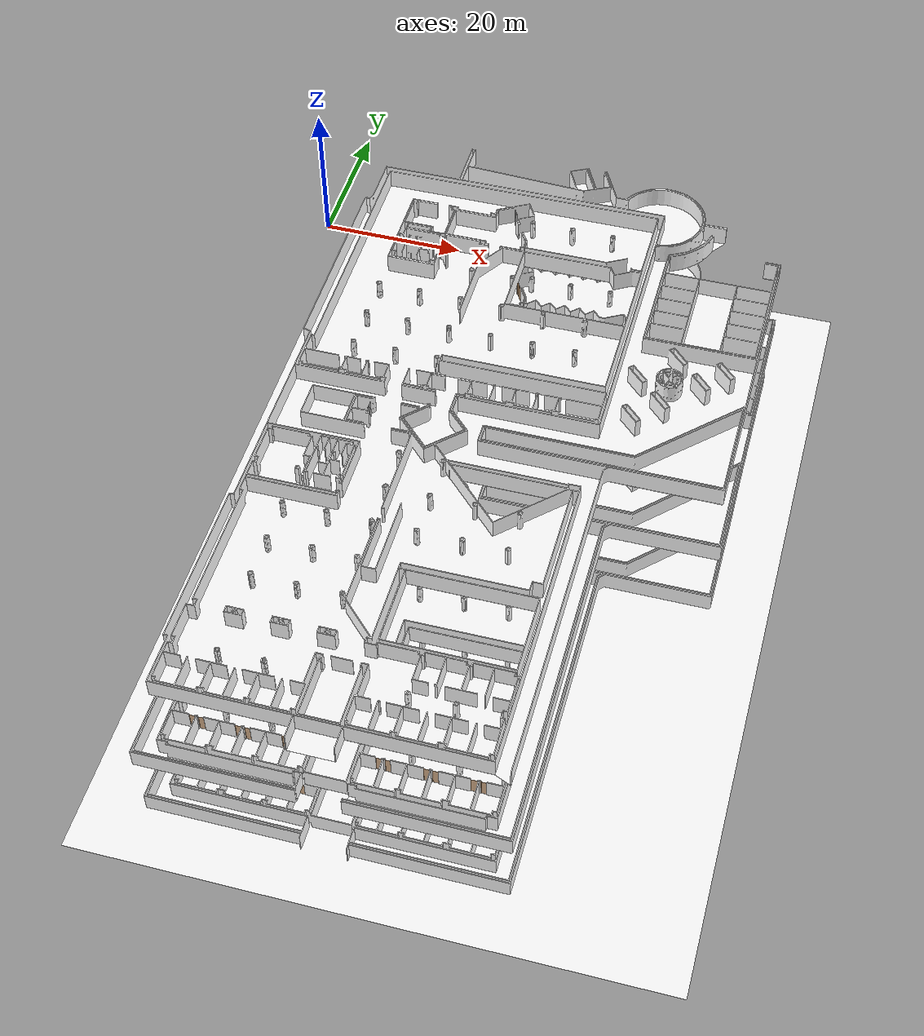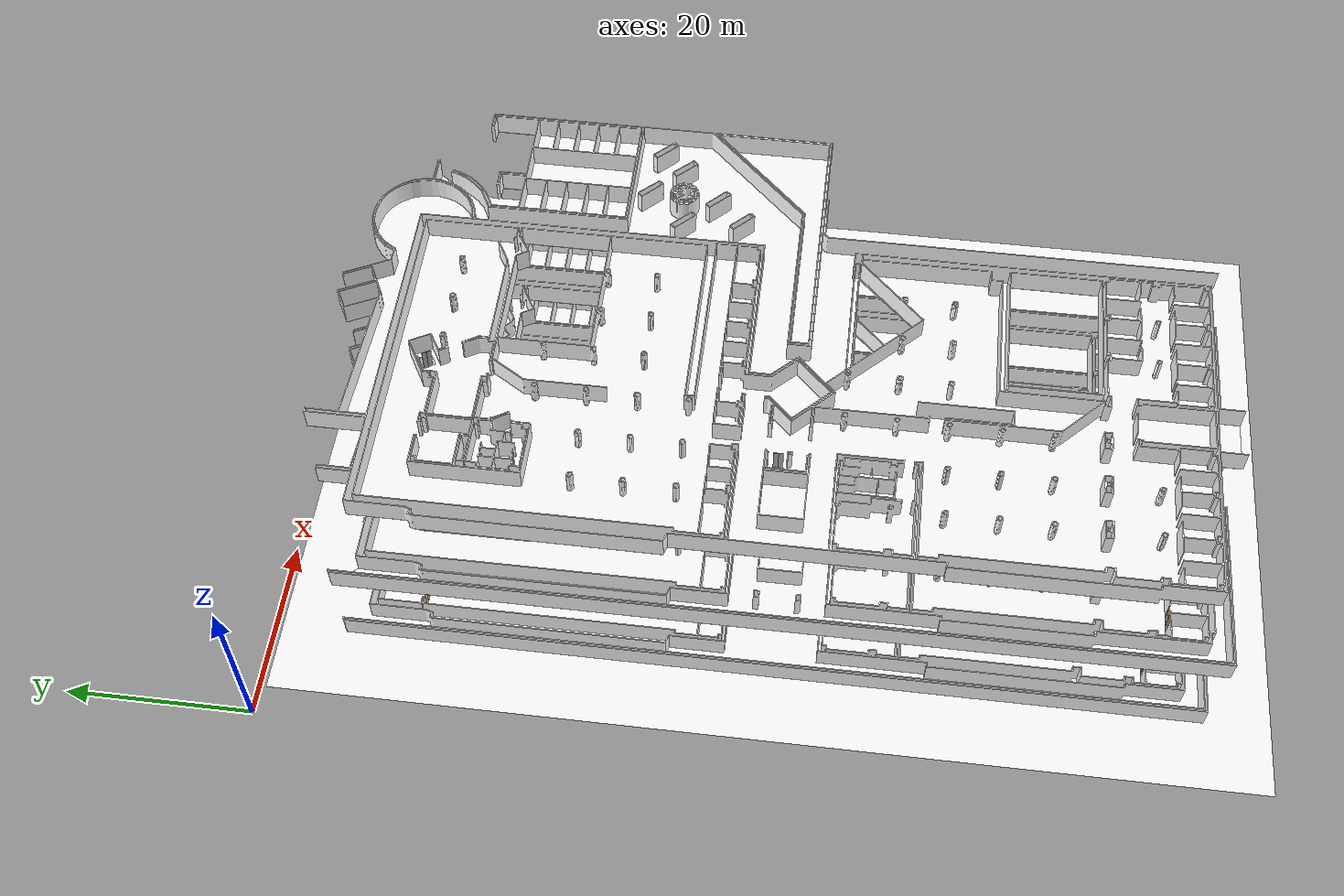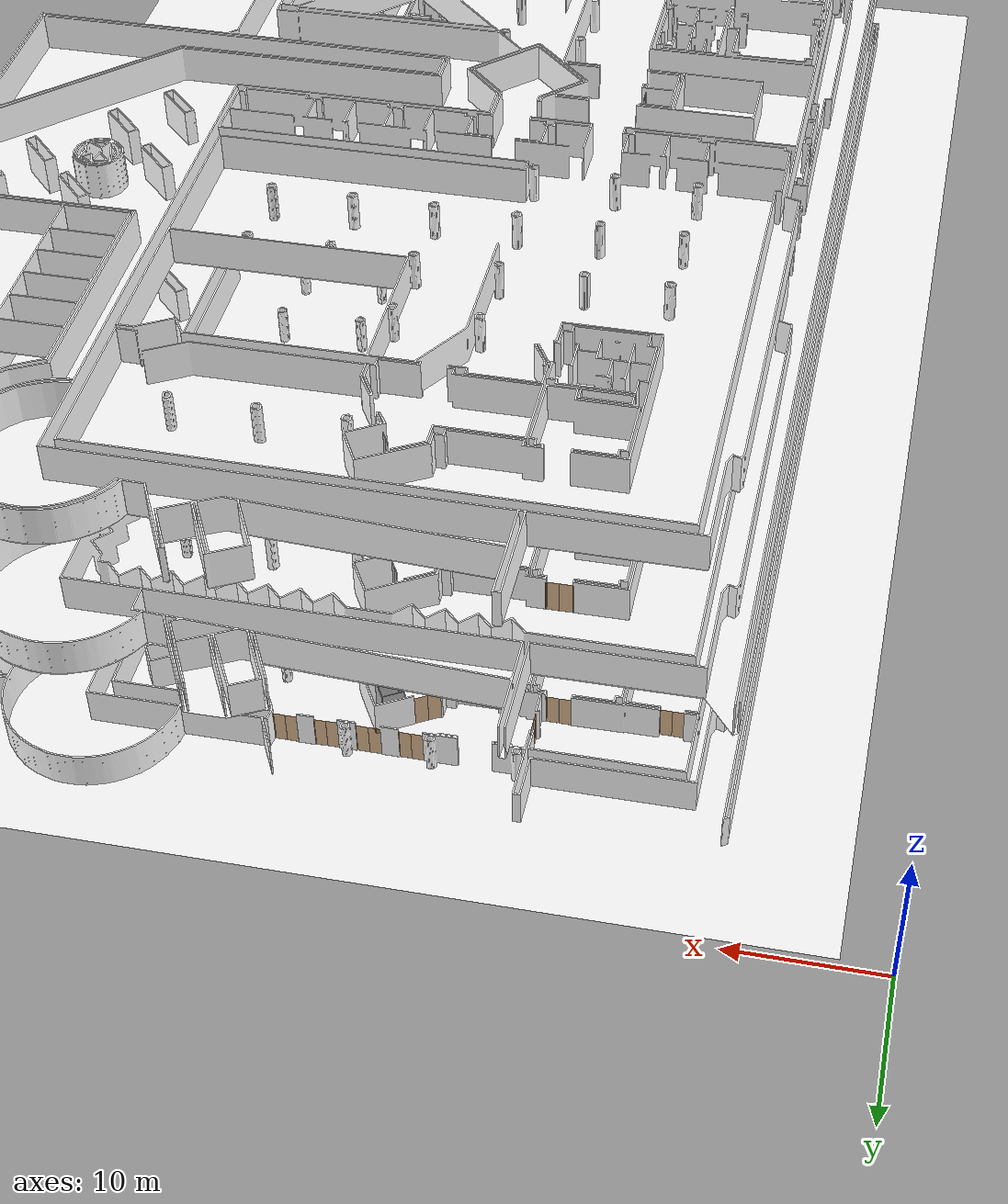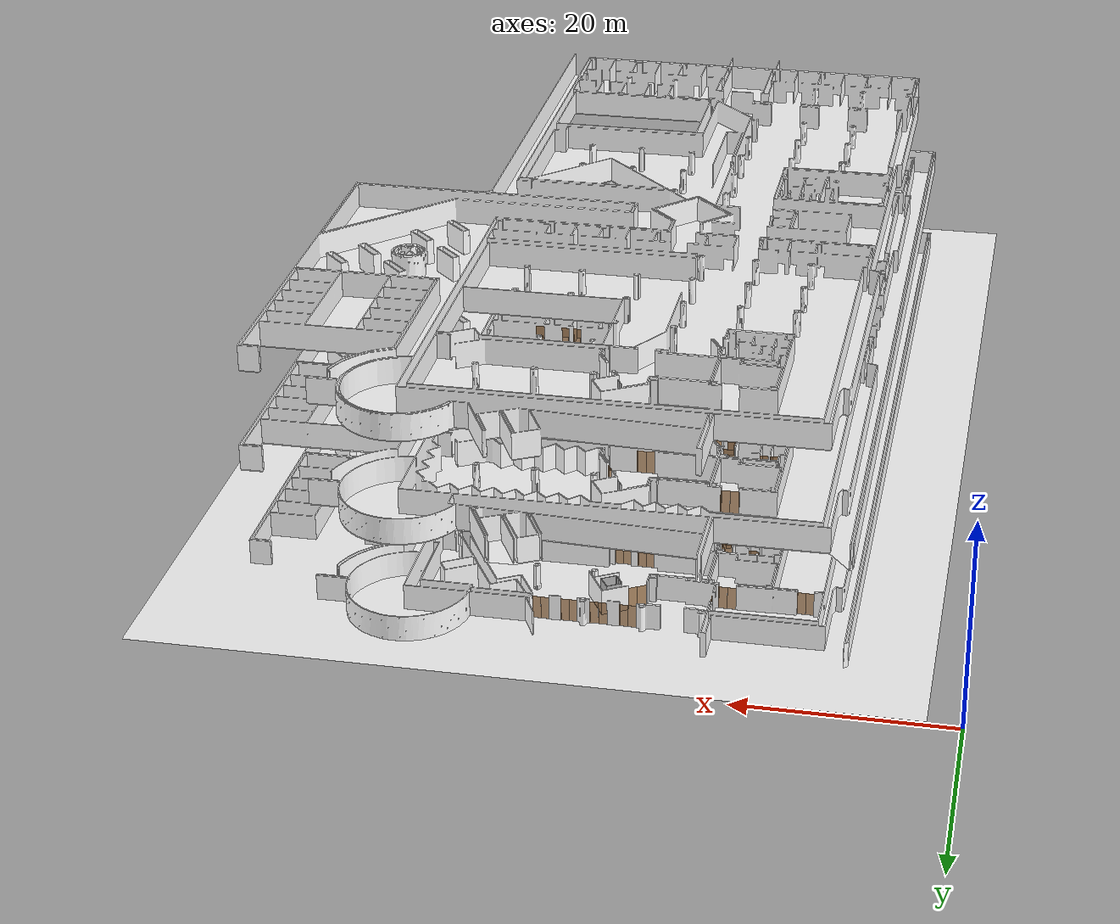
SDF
<sdf version="1.7">
 <world name="sim_world">
  <physics name="10ms" type="ode">
   <max_step_size>0.01</max_step_size>
   <real_time_factor>1.0</real_time_factor>
  </physics>
  <plugin filename="libgz-sim-physics-system.so" name="gz::sim::systems::Physics"/>
  <plugin filename="libgz-sim-user-commands-system.so" name="gz::sim::systems::UserCommands"/>
  <plugin filename="libgz-sim-scene-broadcaster-system.so" name="gz::sim::systems::SceneBroadcaster"/>
  <plugin filename="libdoor.so" name="door"/>
  <plugin filename="liblift.so" name="lift"/>
  <scene><ambient>1 1 1</ambient><background>0.8 0.8 0.8</background><grid>false</grid></scene>
  <light type="directional" name="sun">
   <pose>0 0 10 0 0 0</pose>
   <diffuse>1 1 1 1</diffuse>
   <specular>0.2 0.2 0.2 1</specular>
   <attenuation>
    <range>1000</range>
    <constant>0.09</constant>
    <linear>0.001</linear>
    <quadratic>0.001</quadratic>
   </attenuation>
   <direction>-0.5 0.1 -0.9</direction>
  </light>
  <model name="part1_1">
   <pose>23.474426678062983 -13.057676065197946 0.0 0 0 1.5575382472829962</pose>
   <link name="right">
    <pose>0.4093948700962029 0 1.11 0 0 0</pose>
    <visual name="right_visual">
     <geometry><box><size>0.8087897401924058 0.03 2.2</size></box></geometry>
     <material>
      <ambient>0.5 0.25 0 0.6</ambient>
      <diffuse>0.5 0.25 0 0.6</diffuse>
      <pbr><metal><metalness>0.0</metalness></metal></pbr>
     </material>
    </visual>
    <collision name="right_collision">
     <geometry><box><size>0.8087897401924058 0.03 2.2</size></box></geometry>
     <surface><contact><collide_bitmask>0x02</collide_bitmask></contact></surface>
    </collision>
    <inertial>
     <mass>50.0</mass>
     <inertia><ixx>20.17041666666667</ixx><iyy>22.892253516002086</iyy><izz>2.729336849335414</izz></inertia>
    </inertial>
   </link>
   <joint name="right_joint" type="revolute">
    <parent>world</parent>
    <child>right</child>
    <axis><xyz>0 0 1</xyz><limit><lower>0</lower><upper>1.57</upper></limit></axis>
    <pose>0.4093948700962029 0 0 0 0 0</pose>
   </joint>
   <link name="left">
    <pose>-0.4093948700962029 0 1.11 0 0 0</pose>
    <visual name="left_visual">
     <geometry><box><size>0.8087897401924058 0.03 2.2</size></box></geometry>
     <material>
      <ambient>0.5 0.25 0 0.6</ambient>
      <diffuse>0.5 0.25 0 0.6</diffuse>
      <pbr><metal><metalness>0.0</metalness></metal></pbr>
     </material>
    </visual>
    <collision name="left_collision">
     <geometry><box><size>0.8087897401924058 0.03 2.2</size></box></geometry>
     <surface><contact><collide_bitmask>0x02</collide_bitmask></contact></surface>
    </collision>
    <inertial>
     <mass>50.0</mass>
     <inertia><ixx>20.17041666666667</ixx><iyy>22.892253516002086</iyy><izz>2.729336849335414</izz></inertia>
    </inertial>
   </link>
   <joint name="left_joint" type="revolute">
    <parent>world</parent>
    <child>left</child>
    <axis><xyz>0 0 1</xyz><limit><lower>-1.57</lower><upper>0</upper></limit></axis>
    <pose>-0.4093948700962029 0 0 0 0 0</pose>
   </joint>
   <plugin name="register_component" filename="libregister_component.so">
    <component name="Door">
     <v_max_door>0.5</v_max_door>
     <a_max_door>0.3</a_max_door>
     <a_nom_door>0.15</a_nom_door>
     <dx_min_door>0.01</dx_min_door>
     <f_max_door>500.0</f_max_door>
     <ros_interface>true</ros_interface>
     <door name="part1_1" type="DoubleSwingDoor" left_joint_name="left_joint" right_joint_name="right_joint"/>
    </component>
   </plugin>
  </model>
  <model name="part1_5">
   <pose>30.62381580076393 -10.732564106341501 0.0 0 0 3.1325331828849774</pose>
   <link name="right">
    <pose>0.4033982302911093 0 1.11 0 0 0</pose>
    <visual name="right_visual">
     <geometry><box><size>0.7967964605822186 0.03 2.2</size></box></geometry>
     <material>
      <ambient>0.5 0.25 0 0.6</ambient>
      <diffuse>0.5 0.25 0 0.6</diffuse>
      <pbr><metal><metalness>0.0</metalness></metal></pbr>
     </material>
    </visual>
    <collision name="right_collision">
     <geometry><box><size>0.7967964605822186 0.03 2.2</size></box></geometry>
     <surface><contact><collide_bitmask>0x02</collide_bitmask></contact></surface>
    </collision>
    <inertial>
     <mass>50.0</mass>
     <inertia><ixx>20.17041666666667</ixx><iyy>22.8120191649848</iyy><izz>2.64910249831813</izz></inertia>
    </inertial>
   </link>
   <joint name="right_joint" type="revolute">
    <parent>world</parent>
    <child>right</child>
    <axis><xyz>0 0 1</xyz><limit><lower>0</lower><upper>1.57</upper></limit></axis>
    <pose>0.4033982302911093 0 0 0 0 0</pose>
   </joint>
   <link name="left">
    <pose>-0.4033982302911093 0 1.11 0 0 0</pose>
    <visual name="left_visual">
     <geometry><box><size>0.7967964605822186 0.03 2.2</size></box></geometry>
     <material>
      <ambient>0.5 0.25 0 0.6</ambient>
      <diffuse>0.5 0.25 0 0.6</diffuse>
      <pbr><metal><metalness>0.0</metalness></metal></pbr>
     </material>
    </visual>
    <collision name="left_collision">
     <geometry><box><size>0.7967964605822186 0.03 2.2</size></box></geometry>
     <surface><contact><collide_bitmask>0x02</collide_bitmask></contact></surface>
    </collision>
    <inertial>
     <mass>50.0</mass>
     <inertia><ixx>20.17041666666667</ixx><iyy>22.8120191649848</iyy><izz>2.64910249831813</izz></inertia>
    </inertial>
   </link>
   <joint name="left_joint" type="revolute">
    <parent>world</parent>
    <child>left</child>
    <axis><xyz>0 0 1</xyz><limit><lower>-1.57</lower><upper>0</upper></limit></axis>
    <pose>-0.4033982302911093 0 0 0 0 0</pose>
   </joint>
   <plugin name="register_component" filename="libregister_component.so">
    <component name="Door">
     <v_max_door>0.5</v_max_door>
     <a_max_door>0.3</a_max_door>
     <a_nom_door>0.15</a_nom_door>
     <dx_min_door>0.01</dx_min_door>
     <f_max_door>500.0</f_max_door>
     <ros_interface>true</ros_interface>
     <door name="part1_5" type="DoubleSwingDoor" left_joint_name="left_joint" right_joint_name="right_joint"/>
    </component>
   </plugin>
  </model>
  <model name="part1_6">
   <pose>33.303837845168346 -10.745754091436014 0.0 0 0 3.134548012368475</pose>
   <link name="right">
    <pose>0.4174083984026789 0 1.11 0 0 0</pose>
    <visual name="right_visual">
     <geometry><box><size>0.8248167968053578 0.03 2.2</size></box></geometry>
     <material>
      <ambient>0.5 0.25 0 0.6</ambient>
      <diffuse>0.5 0.25 0 0.6</diffuse>
      <pbr><metal><metalness>0.0</metalness></metal></pbr>
     </material>
    </visual>
    <collision name="right_collision">
     <geometry><box><size>0.8248167968053578 0.03 2.2</size></box></geometry>
     <surface><contact><collide_bitmask>0x02</collide_bitmask></contact></surface>
    </collision>
    <inertial>
     <mass>50.0</mass>
     <inertia><ixx>20.17041666666667</ixx><iyy>23.001344784551048</iyy><izz>2.838428117884379</izz></inertia>
    </inertial>
   </link>
   <joint name="right_joint" type="revolute">
    <parent>world</parent>
    <child>right</child>
    <axis><xyz>0 0 1</xyz><limit><lower>0</lower><upper>1.57</upper></limit></axis>
    <pose>0.4174083984026789 0 0 0 0 0</pose>
   </joint>
   <link name="left">
    <pose>-0.4174083984026789 0 1.11 0 0 0</pose>
    <visual name="left_visual">
     <geometry><box><size>0.8248167968053578 0.03 2.2</size></box></geometry>
     <material>
      <ambient>0.5 0.25 0 0.6</ambient>
      <diffuse>0.5 0.25 0 0.6</diffuse>
      <pbr><metal><metalness>0.0</metalness></metal></pbr>
     </material>
    </visual>
    <collision name="left_collision">
     <geometry><box><size>0.8248167968053578 0.03 2.2</size></box></geometry>
     <surface><contact><collide_bitmask>0x02</collide_bitmask></contact></surface>
    </collision>
    <inertial>
     <mass>50.0</mass>
     <inertia><ixx>20.17041666666667</ixx><iyy>23.001344784551048</iyy><izz>2.838428117884379</izz></inertia>
    </inertial>
   </link>
   <joint name="left_joint" type="revolute">
    <parent>world</parent>
    <child>left</child>
    <axis><xyz>0 0 1</xyz><limit><lower>-1.57</lower><upper>0</upper></limit></axis>
    <pose>-0.4174083984026789 0 0 0 0 0</pose>
   </joint>
   <plugin name="register_component" filename="libregister_component.so">
    <component name="Door">
     <v_max_door>0.5</v_max_door>
     <a_max_door>0.3</a_max_door>
     <a_nom_door>0.15</a_nom_door>
     <dx_min_door>0.01</dx_min_door>
     <f_max_door>500.0</f_max_door>
     <ros_interface>true</ros_interface>
     <door name="part1_6" type="DoubleSwingDoor" left_joint_name="left_joint" right_joint_name="right_joint"/>
    </component>
   </plugin>
  </model>
  <model name="part1_7">
   <pose>35.98657169916032 -10.742288109951325 0.0 0 0 -3.1297649534100933</pose>
   <link name="right">
    <pose>0.3951374930538005 0 1.11 0 0 0</pose>
    <visual name="right_visual">
     <geometry><box><size>0.780274986107601 0.03 2.2</size></box></geometry>
     <material>
      <ambient>0.5 0.25 0 0.6</ambient>
      <diffuse>0.5 0.25 0 0.6</diffuse>
      <pbr><metal><metalness>0.0</metalness></metal></pbr>
     </material>
    </visual>
    <collision name="right_collision">
     <geometry><box><size>0.780274986107601 0.03 2.2</size></box></geometry>
     <surface><contact><collide_bitmask>0x02</collide_bitmask></contact></surface>
    </collision>
    <inertial>
     <mass>50.0</mass>
     <inertia><ixx>20.17041666666667</ixx><iyy>22.70345439143841</iyy><izz>2.540537724771738</izz></inertia>
    </inertial>
   </link>
   <joint name="right_joint" type="revolute">
    <parent>world</parent>
    <child>right</child>
    <axis><xyz>0 0 1</xyz><limit><lower>0</lower><upper>1.57</upper></limit></axis>
    <pose>0.3951374930538005 0 0 0 0 0</pose>
   </joint>
   <link name="left">
    <pose>-0.3951374930538005 0 1.11 0 0 0</pose>
    <visual name="left_visual">
     <geometry><box><size>0.780274986107601 0.03 2.2</size></box></geometry>
     <material>
      <ambient>0.5 0.25 0 0.6</ambient>
      <diffuse>0.5 0.25 0 0.6</diffuse>
      <pbr><metal><metalness>0.0</metalness></metal></pbr>
     </material>
    </visual>
    <collision name="left_collision">
     <geometry><box><size>0.780274986107601 0.03 2.2</size></box></geometry>
     <surface><contact><collide_bitmask>0x02</collide_bitmask></contact></surface>
    </collision>
    <inertial>
     <mass>50.0</mass>
     <inertia><ixx>20.17041666666667</ixx><iyy>22.70345439143841</iyy><izz>2.540537724771738</izz></inertia>
    </inertial>
   </link>
   <joint name="left_joint" type="revolute">
    <parent>world</parent>
    <child>left</child>
    <axis><xyz>0 0 1</xyz><limit><lower>-1.57</lower><upper>0</upper></limit></axis>
    <pose>-0.3951374930538005 0 0 0 0 0</pose>
   </joint>
   <plugin name="register_component" filename="libregister_component.so">
    <component name="Door">
     <v_max_door>0.5</v_max_door>
     <a_max_door>0.3</a_max_door>
     <a_nom_door>0.15</a_nom_door>
     <dx_min_door>0.01</dx_min_door>
     <f_max_door>500.0</f_max_door>
     <ros_interface>true</ros_interface>
     <door name="part1_7" type="DoubleSwingDoor" left_joint_name="left_joint" right_joint_name="right_joint"/>
    </component>
   </plugin>
  </model>
  <model name="part1_8">
   <pose>38.57675903364792 -10.742207878898437 0.0 0 0 3.1300311442483824</pose>
   <link name="right">
    <pose>0.40076484747594776 0 1.11 0 0 0</pose>
    <visual name="right_visual">
     <geometry><box><size>0.7915296949518955 0.03 2.2</size></box></geometry>
     <material>
      <ambient>0.5 0.25 0 0.6</ambient>
      <diffuse>0.5 0.25 0 0.6</diffuse>
      <pbr><metal><metalness>0.0</metalness></metal></pbr>
     </material>
    </visual>
    <collision name="right_collision">
     <geometry><box><size>0.7915296949518955 0.03 2.2</size></box></geometry>
     <surface><contact><collide_bitmask>0x02</collide_bitmask></contact></surface>
    </collision>
    <inertial>
     <mass>50.0</mass>
     <inertia><ixx>20.17041666666667</ixx><iyy>22.777163574961005</iyy><izz>2.6142469082943367</izz></inertia>
    </inertial>
   </link>
   <joint name="right_joint" type="revolute">
    <parent>world</parent>
    <child>right</child>
    <axis><xyz>0 0 1</xyz><limit><lower>0</lower><upper>1.57</upper></limit></axis>
    <pose>0.40076484747594776 0 0 0 0 0</pose>
   </joint>
   <link name="left">
    <pose>-0.40076484747594776 0 1.11 0 0 0</pose>
    <visual name="left_visual">
     <geometry><box><size>0.7915296949518955 0.03 2.2</size></box></geometry>
     <material>
      <ambient>0.5 0.25 0 0.6</ambient>
      <diffuse>0.5 0.25 0 0.6</diffuse>
      <pbr><metal><metalness>0.0</metalness></metal></pbr>
     </material>
    </visual>
    <collision name="left_collision">
     <geometry><box><size>0.7915296949518955 0.03 2.2</size></box></geometry>
     <surface><contact><collide_bitmask>0x02</collide_bitmask></contact></surface>
    </collision>
    <inertial>
     <mass>50.0</mass>
     <inertia><ixx>20.17041666666667</ixx><iyy>22.777163574961005</iyy><izz>2.6142469082943367</izz></inertia>
    </inertial>
   </link>
   <joint name="left_joint" type="revolute">
    <parent>world</parent>
    <child>left</child>
    <axis><xyz>0 0 1</xyz><limit><lower>-1.57</lower><upper>0</upper></limit></axis>
    <pose>-0.40076484747594776 0 0 0 0 0</pose>
   </joint>
   <plugin name="register_component" filename="libregister_component.so">
    <component name="Door">
     <v_max_door>0.5</v_max_door>
     <a_max_door>0.3</a_max_door>
     <a_nom_door>0.15</a_nom_door>
     <dx_min_door>0.01</dx_min_door>
     <f_max_door>500.0</f_max_door>
     <ros_interface>true</ros_interface>
     <door name="part1_8" type="DoubleSwingDoor" left_joint_name="left_joint" right_joint_name="right_joint"/>
    </component>
   </plugin>
  </model>
  <model name="part1_4">
   <pose>30.361404096088606 -14.032708004714948 0.0 0 0 -2.62655505252304</pose>
   <link name="right">
    <pose>0.4545178244978947 0 1.11 0 0 0</pose>
    <visual name="right_visual">
     <geometry><box><size>0.8990356489957894 0.03 2.2</size></box></geometry>
     <material>
      <ambient>0.5 0.25 0 0.6</ambient>
      <diffuse>0.5 0.25 0 0.6</diffuse>
      <pbr><metal><metalness>0.0</metalness></metal></pbr>
     </material>
    </visual>
    <collision name="right_collision">
     <geometry><box><size>0.8990356489957894 0.03 2.2</size></box></geometry>
     <surface><contact><collide_bitmask>0x02</collide_bitmask></contact></surface>
    </collision>
    <inertial>
     <mass>50.0</mass>
     <inertia><ixx>20.17041666666667</ixx><iyy>23.534437909022003</iyy><izz>3.371521242355334</izz></inertia>
    </inertial>
   </link>
   <joint name="right_joint" type="revolute">
    <parent>world</parent>
    <child>right</child>
    <axis><xyz>0 0 1</xyz><limit><lower>0</lower><upper>1.57</upper></limit></axis>
    <pose>0.4545178244978947 0 0 0 0 0</pose>
   </joint>
   <link name="left">
    <pose>-0.4545178244978947 0 1.11 0 0 0</pose>
    <visual name="left_visual">
     <geometry><box><size>0.8990356489957894 0.03 2.2</size></box></geometry>
     <material>
      <ambient>0.5 0.25 0 0.6</ambient>
      <diffuse>0.5 0.25 0 0.6</diffuse>
      <pbr><metal><metalness>0.0</metalness></metal></pbr>
     </material>
    </visual>
    <collision name="left_collision">
     <geometry><box><size>0.8990356489957894 0.03 2.2</size></box></geometry>
     <surface><contact><collide_bitmask>0x02</collide_bitmask></contact></surface>
    </collision>
    <inertial>
     <mass>50.0</mass>
     <inertia><ixx>20.17041666666667</ixx><iyy>23.534437909022003</iyy><izz>3.371521242355334</izz></inertia>
    </inertial>
   </link>
   <joint name="left_joint" type="revolute">
    <parent>world</parent>
    <child>left</child>
    <axis><xyz>0 0 1</xyz><limit><lower>-1.57</lower><upper>0</upper></limit></axis>
    <pose>-0.4545178244978947 0 0 0 0 0</pose>
   </joint>
   <plugin name="register_component" filename="libregister_component.so">
    <component name="Door">
     <v_max_door>0.5</v_max_door>
     <a_max_door>0.3</a_max_door>
     <a_nom_door>0.15</a_nom_door>
     <dx_min_door>0.01</dx_min_door>
     <f_max_door>500.0</f_max_door>
     <ros_interface>true</ros_interface>
     <door name="part1_4" type="DoubleSwingDoor" left_joint_name="left_joint" right_joint_name="right_joint"/>
    </component>
   </plugin>
  </model>
  <model name="part1_9">
   <pose>30.839613263712295 -21.2473811351495 0.0 0 0 -3.1402743417935888</pose>
   <link name="right">
    <pose>0.4016690922096701 0 1.11 0 0 0</pose>
    <visual name="right_visual">
     <geometry><box><size>0.7933381844193402 0.03 2.2</size></box></geometry>
     <material>
      <ambient>0.5 0.25 0 0.6</ambient>
      <diffuse>0.5 0.25 0 0.6</diffuse>
      <pbr><metal><metalness>0.0</metalness></metal></pbr>
     </material>
    </visual>
    <collision name="right_collision">
     <geometry><box><size>0.7933381844193402 0.03 2.2</size></box></geometry>
     <surface><contact><collide_bitmask>0x02</collide_bitmask></contact></surface>
    </collision>
    <inertial>
     <mass>50.0</mass>
     <inertia><ixx>20.17041666666667</ixx><iyy>22.789106145240737</iyy><izz>2.626189478574063</izz></inertia>
    </inertial>
   </link>
   <joint name="right_joint" type="revolute">
    <parent>world</parent>
    <child>right</child>
    <axis><xyz>0 0 1</xyz><limit><lower>0</lower><upper>1.57</upper></limit></axis>
    <pose>0.4016690922096701 0 0 0 0 0</pose>
   </joint>
   <link name="left">
    <pose>-0.4016690922096701 0 1.11 0 0 0</pose>
    <visual name="left_visual">
     <geometry><box><size>0.7933381844193402 0.03 2.2</size></box></geometry>
     <material>
      <ambient>0.5 0.25 0 0.6</ambient>
      <diffuse>0.5 0.25 0 0.6</diffuse>
      <pbr><metal><metalness>0.0</metalness></metal></pbr>
     </material>
    </visual>
    <collision name="left_collision">
     <geometry><box><size>0.7933381844193402 0.03 2.2</size></box></geometry>
     <surface><contact><collide_bitmask>0x02</collide_bitmask></contact></surface>
    </collision>
    <inertial>
     <mass>50.0</mass>
     <inertia><ixx>20.17041666666667</ixx><iyy>22.789106145240737</iyy><izz>2.626189478574063</izz></inertia>
    </inertial>
   </link>
   <joint name="left_joint" type="revolute">
    <parent>world</parent>
    <child>left</child>
    <axis><xyz>0 0 1</xyz><limit><lower>-1.57</lower><upper>0</upper></limit></axis>
    <pose>-0.4016690922096701 0 0 0 0 0</pose>
   </joint>
   <plugin name="register_component" filename="libregister_component.so">
    <component name="Door">
     <v_max_door>0.5</v_max_door>
     <a_max_door>0.3</a_max_door>
     <a_nom_door>0.15</a_nom_door>
     <dx_min_door>0.01</dx_min_door>
     <f_max_door>500.0</f_max_door>
     <ros_interface>true</ros_interface>
     <door name="part1_9" type="DoubleSwingDoor" left_joint_name="left_joint" right_joint_name="right_joint"/>
    </component>
   </plugin>
  </model>
  <model name="part1_10_end">
   <pose>33.01170053539864 -21.444909987355643 0.0 0 0 -3.1235009749570586</pose>
   <link name="right">
    <pose>0.38805686569392206 0 1.11 0 0 0</pose>
    <visual name="right_visual">
     <geometry><box><size>0.7661137313878441 0.03 2.2</size></box></geometry>
     <material>
      <ambient>0.5 0.25 0 0.6</ambient>
      <diffuse>0.5 0.25 0 0.6</diffuse>
      <pbr><metal><metalness>0.0</metalness></metal></pbr>
     </material>
    </visual>
    <collision name="right_collision">
     <geometry><box><size>0.7661137313878441 0.03 2.2</size></box></geometry>
     <surface><contact><collide_bitmask>0x02</collide_bitmask></contact></surface>
    </collision>
    <inertial>
     <mass>50.0</mass>
     <inertia><ixx>20.17041666666667</ixx><iyy>22.612209372587532</iyy><izz>2.4492927059208576</izz></inertia>
    </inertial>
   </link>
   <joint name="right_joint" type="revolute">
    <parent>world</parent>
    <child>right</child>
    <axis><xyz>0 0 -1</xyz><limit><lower>0</lower><upper>1.57</upper></limit></axis>
    <pose>0.38805686569392206 0 0 0 0 0</pose>
   </joint>
   <link name="left">
    <pose>-0.38805686569392206 0 1.11 0 0 0</pose>
    <visual name="left_visual">
     <geometry><box><size>0.7661137313878441 0.03 2.2</size></box></geometry>
     <material>
      <ambient>0.5 0.25 0 0.6</ambient>
      <diffuse>0.5 0.25 0 0.6</diffuse>
      <pbr><metal><metalness>0.0</metalness></metal></pbr>
     </material>
    </visual>
    <collision name="left_collision">
     <geometry><box><size>0.7661137313878441 0.03 2.2</size></box></geometry>
     <surface><contact><collide_bitmask>0x02</collide_bitmask></contact></surface>
    </collision>
    <inertial>
     <mass>50.0</mass>
     <inertia><ixx>20.17041666666667</ixx><iyy>22.612209372587532</iyy><izz>2.4492927059208576</izz></inertia>
    </inertial>
   </link>
   <joint name="left_joint" type="revolute">
    <parent>world</parent>
    <child>left</child>
    <axis><xyz>0 0 -1</xyz><limit><lower>-1.57</lower><upper>0</upper></limit></axis>
    <pose>-0.38805686569392206 0 0 0 0 0</pose>
   </joint>
   <plugin name="register_component" filename="libregister_component.so">
    <component name="Door">
     <v_max_door>0.5</v_max_door>
     <a_max_door>0.3</a_max_door>
     <a_nom_door>0.15</a_nom_door>
     <dx_min_door>0.01</dx_min_door>
     <f_max_door>500.0</f_max_door>
     <ros_interface>true</ros_interface>
     <door name="part1_10_end" type="DoubleSwingDoor" left_joint_name="left_joint" right_joint_name="right_joint"/>
    </component>
   </plugin>
  </model>
  <model name="part1_2">
   <pose>22.344348228843145 -15.362987000202047 0.0 0 0 3.138955944615511</pose>
   <link name="right">
    <pose>0.4275206745211724 0 1.11 0 0 0</pose>
    <visual name="right_visual">
     <geometry><box><size>0.8450413490423447 0.03 2.2</size></box></geometry>
     <material>
      <ambient>0.5 0.25 0 0.6</ambient>
      <diffuse>0.5 0.25 0 0.6</diffuse>
      <pbr><metal><metalness>0.0</metalness></metal></pbr>
     </material>
    </visual>
    <collision name="right_collision">
     <geometry><box><size>0.8450413490423447 0.03 2.2</size></box></geometry>
     <surface><contact><collide_bitmask>0x02</collide_bitmask></contact></surface>
    </collision>
    <inertial>
     <mass>50.0</mass>
     <inertia><ixx>20.17041666666667</ixx><iyy>23.142062006630447</iyy><izz>2.979145339963775</izz></inertia>
    </inertial>
   </link>
   <joint name="right_joint" type="revolute">
    <parent>world</parent>
    <child>right</child>
    <axis><xyz>0 0 1</xyz><limit><lower>0</lower><upper>1.57</upper></limit></axis>
    <pose>0.4275206745211724 0 0 0 0 0</pose>
   </joint>
   <link name="left">
    <pose>-0.4275206745211724 0 1.11 0 0 0</pose>
    <visual name="left_visual">
     <geometry><box><size>0.8450413490423447 0.03 2.2</size></box></geometry>
     <material>
      <ambient>0.5 0.25 0 0.6</ambient>
      <diffuse>0.5 0.25 0 0.6</diffuse>
      <pbr><metal><metalness>0.0</metalness></metal></pbr>
     </material>
    </visual>
    <collision name="left_collision">
     <geometry><box><size>0.8450413490423447 0.03 2.2</size></box></geometry>
     <surface><contact><collide_bitmask>0x02</collide_bitmask></contact></surface>
    </collision>
    <inertial>
     <mass>50.0</mass>
     <inertia><ixx>20.17041666666667</ixx><iyy>23.142062006630447</iyy><izz>2.979145339963775</izz></inertia>
    </inertial>
   </link>
   <joint name="left_joint" type="revolute">
    <parent>world</parent>
    <child>left</child>
    <axis><xyz>0 0 1</xyz><limit><lower>-1.57</lower><upper>0</upper></limit></axis>
    <pose>-0.4275206745211724 0 0 0 0 0</pose>
   </joint>
   <plugin name="register_component" filename="libregister_component.so">
    <component name="Door">
     <v_max_door>0.5</v_max_door>
     <a_max_door>0.3</a_max_door>
     <a_nom_door>0.15</a_nom_door>
     <dx_min_door>0.01</dx_min_door>
     <f_max_door>500.0</f_max_door>
     <ros_interface>true</ros_interface>
     <door name="part1_2" type="DoubleSwingDoor" left_joint_name="left_joint" right_joint_name="right_joint"/>
    </component>
   </plugin>
  </model>
  <model name="part1_3">
   <pose>15.253664167539132 -15.64746224442111 0.0 0 0 3.1277439827895375</pose>
   <link name="right">
    <pose>0.4009169117466249 0 1.11 0 0 0</pose>
    <visual name="right_visual">
     <geometry><box><size>0.7918338234932498 0.03 2.2</size></box></geometry>
     <material>
      <ambient>0.5 0.25 0 0.6</ambient>
      <diffuse>0.5 0.25 0 0.6</diffuse>
      <pbr><metal><metalness>0.0</metalness></metal></pbr>
     </material>
    </visual>
    <collision name="right_collision">
     <geometry><box><size>0.7918338234932498 0.03 2.2</size></box></geometry>
     <surface><contact><collide_bitmask>0x02</collide_bitmask></contact></surface>
    </collision>
    <inertial>
     <mass>50.0</mass>
     <inertia><ixx>20.17041666666667</ixx><iyy>22.779170016783084</iyy><izz>2.616253350116413</izz></inertia>
    </inertial>
   </link>
   <joint name="right_joint" type="revolute">
    <parent>world</parent>
    <child>right</child>
    <axis><xyz>0 0 -1</xyz><limit><lower>0</lower><upper>1.57</upper></limit></axis>
    <pose>0.4009169117466249 0 0 0 0 0</pose>
   </joint>
   <link name="left">
    <pose>-0.4009169117466249 0 1.11 0 0 0</pose>
    <visual name="left_visual">
     <geometry><box><size>0.7918338234932498 0.03 2.2</size></box></geometry>
     <material>
      <ambient>0.5 0.25 0 0.6</ambient>
      <diffuse>0.5 0.25 0 0.6</diffuse>
      <pbr><metal><metalness>0.0</metalness></metal></pbr>
     </material>
    </visual>
    <collision name="left_collision">
     <geometry><box><size>0.7918338234932498 0.03 2.2</size></box></geometry>
     <surface><contact><collide_bitmask>0x02</collide_bitmask></contact></surface>
    </collision>
    <inertial>
     <mass>50.0</mass>
     <inertia><ixx>20.17041666666667</ixx><iyy>22.779170016783084</iyy><izz>2.616253350116413</izz></inertia>
    </inertial>
   </link>
   <joint name="left_joint" type="revolute">
    <parent>world</parent>
    <child>left</child>
    <axis><xyz>0 0 -1</xyz><limit><lower>-1.57</lower><upper>0</upper></limit></axis>
    <pose>-0.4009169117466249 0 0 0 0 0</pose>
   </joint>
   <plugin name="register_component" filename="libregister_component.so">
    <component name="Door">
     <v_max_door>0.5</v_max_door>
     <a_max_door>0.3</a_max_door>
     <a_nom_door>0.15</a_nom_door>
     <dx_min_door>0.01</dx_min_door>
     <f_max_door>500.0</f_max_door>
     <ros_interface>true</ros_interface>
     <door name="part1_3" type="DoubleSwingDoor" left_joint_name="left_joint" right_joint_name="right_joint"/>
    </component>
   </plugin>
  </model>
  <model name="part2_1">
   <pose>20.413066439289835 -21.727644217727075 0.0 0 0 1.5586480130347593</pose>
   <link name="right">
    <pose>0 0 1.11 0 0 0</pose>
    <visual name="right_visual">
     <geometry><box><size>0.9555717398338419 0.03 2.2</size></box></geometry>
     <material>
      <ambient>0.5 0.25 0 0.6</ambient>
      <diffuse>0.5 0.25 0 0.6</diffuse>
      <pbr><metal><metalness>0.0</metalness></metal></pbr>
     </material>
    </visual>
    <collision name="right_collision">
     <geometry><box><size>0.9555717398338419 0.03 2.2</size></box></geometry>
     <surface><contact><collide_bitmask>0x02</collide_bitmask></contact></surface>
    </collision>
    <inertial>
     <mass>50.0</mass>
     <inertia><ixx>20.17041666666667</ixx><iyy>23.97132229153782</iyy><izz>3.808405624871149</izz></inertia>
    </inertial>
   </link>
   <joint name="right_joint" type="revolute">
    <parent>world</parent>
    <child>right</child>
    <axis><xyz>0 0 -1</xyz><limit><lower>0</lower><upper>1.57</upper></limit></axis>
    <pose>0.48278586991692096 0 0 0 0 0</pose>
   </joint>
   <plugin name="register_component" filename="libregister_component.so">
    <component name="Door">
     <v_max_door>0.5</v_max_door>
     <a_max_door>0.3</a_max_door>
     <a_nom_door>0.15</a_nom_door>
     <dx_min_door>0.01</dx_min_door>
     <f_max_door>500.0</f_max_door>
     <ros_interface>true</ros_interface>
     <door name="part2_1" type="SwingDoor" left_joint_name="empty_joint" right_joint_name="right_joint"/>
    </component>
   </plugin>
  </model>
  <model name="part2_4">
   <pose>20.922670017907944 -22.218112690231795 0.0 0 0 3.126620543687866</pose>
   <link name="right">
    <pose>0 0 1.11 0 0 0</pose>
    <visual name="right_visual">
     <geometry><box><size>1.0210524974741124 0.03 2.2</size></box></geometry>
     <material>
      <ambient>0.5 0.25 0 0.6</ambient>
      <diffuse>0.5 0.25 0 0.6</diffuse>
      <pbr><metal><metalness>0.0</metalness></metal></pbr>
     </material>
    </visual>
    <collision name="right_collision">
     <geometry><box><size>1.0210524974741124 0.03 2.2</size></box></geometry>
     <surface><contact><collide_bitmask>0x02</collide_bitmask></contact></surface>
    </collision>
    <inertial>
     <mass>50.0</mass>
     <inertia><ixx>20.17041666666667</ixx><iyy>24.510617510825515</iyy><izz>4.347700844158843</izz></inertia>
    </inertial>
   </link>
   <joint name="right_joint" type="revolute">
    <parent>world</parent>
    <child>right</child>
    <axis><xyz>0 0 1</xyz><limit><lower>0</lower><upper>1.57</upper></limit></axis>
    <pose>0.5155262487370562 0 0 0 0 0</pose>
   </joint>
   <plugin name="register_component" filename="libregister_component.so">
    <component name="Door">
     <v_max_door>0.5</v_max_door>
     <a_max_door>0.3</a_max_door>
     <a_nom_door>0.15</a_nom_door>
     <dx_min_door>0.01</dx_min_door>
     <f_max_door>500.0</f_max_door>
     <ros_interface>true</ros_interface>
     <door name="part2_4" type="SwingDoor" left_joint_name="empty_joint" right_joint_name="right_joint"/>
    </component>
   </plugin>
  </model>
  <model name="part2_3">
   <pose>20.919621237898262 -25.424450441570542 0.0 0 0 -3.1088230642559003</pose>
   <link name="right">
    <pose>0 0 1.11 0 0 0</pose>
    <visual name="right_visual">
     <geometry><box><size>1.0312199456807118 0.03 2.2</size></box></geometry>
     <material>
      <ambient>0.5 0.25 0 0.6</ambient>
      <diffuse>0.5 0.25 0 0.6</diffuse>
      <pbr><metal><metalness>0.0</metalness></metal></pbr>
     </material>
    </visual>
    <collision name="right_collision">
     <geometry><box><size>1.0312199456807118 0.03 2.2</size></box></geometry>
     <surface><contact><collide_bitmask>0x02</collide_bitmask></contact></surface>
    </collision>
    <inertial>
     <mass>50.0</mass>
     <inertia><ixx>20.17041666666667</ixx><iyy>24.59756073487388</iyy><izz>4.434644068207209</izz></inertia>
    </inertial>
   </link>
   <joint name="right_joint" type="revolute">
    <parent>world</parent>
    <child>right</child>
    <axis><xyz>0 0 -1</xyz><limit><lower>0</lower><upper>1.57</upper></limit></axis>
    <pose>0.5206099728403559 0 0 0 0 0</pose>
   </joint>
   <plugin name="register_component" filename="libregister_component.so">
    <component name="Door">
     <v_max_door>0.5</v_max_door>
     <a_max_door>0.3</a_max_door>
     <a_nom_door>0.15</a_nom_door>
     <dx_min_door>0.01</dx_min_door>
     <f_max_door>500.0</f_max_door>
     <ros_interface>true</ros_interface>
     <door name="part2_3" type="SwingDoor" left_joint_name="empty_joint" right_joint_name="right_joint"/>
    </component>
   </plugin>
  </model>
  <model name="part2_2">
   <pose>20.38263480093005 -25.917791185768593 0.0 0 0 1.535839882828038</pose>
   <link name="right">
    <pose>0 0 1.11 0 0 0</pose>
    <visual name="right_visual">
     <geometry><box><size>0.9431495373669919 0.03 2.2</size></box></geometry>
     <material>
      <ambient>0.5 0.25 0 0.6</ambient>
      <diffuse>0.5 0.25 0 0.6</diffuse>
      <pbr><metal><metalness>0.0</metalness></metal></pbr>
     </material>
    </visual>
    <collision name="right_collision">
     <geometry><box><size>0.9431495373669919 0.03 2.2</size></box></geometry>
     <surface><contact><collide_bitmask>0x02</collide_bitmask></contact></surface>
    </collision>
    <inertial>
     <mass>50.0</mass>
     <inertia><ixx>20.17041666666667</ixx><iyy>23.87304604098155</iyy><izz>3.710129374314879</izz></inertia>
    </inertial>
   </link>
   <joint name="right_joint" type="revolute">
    <parent>world</parent>
    <child>right</child>
    <axis><xyz>0 0 1</xyz><limit><lower>0</lower><upper>1.57</upper></limit></axis>
    <pose>0.47657476868349596 0 0 0 0 0</pose>
   </joint>
   <plugin name="register_component" filename="libregister_component.so">
    <component name="Door">
     <v_max_door>0.5</v_max_door>
     <a_max_door>0.3</a_max_door>
     <a_nom_door>0.15</a_nom_door>
     <dx_min_door>0.01</dx_min_door>
     <f_max_door>500.0</f_max_door>
     <ros_interface>true</ros_interface>
     <door name="part2_2" type="SwingDoor" left_joint_name="empty_joint" right_joint_name="right_joint"/>
    </component>
   </plugin>
  </model>
  <model name="part2_6">
   <pose>23.62189937637335 -24.873600078663575 0.0 0 0 3.137896065827331</pose>
   <link name="right">
    <pose>0 0 1.11 0 0 0</pose>
    <visual name="right_visual">
     <geometry><box><size>0.9276185826104854 0.03 2.2</size></box></geometry>
     <material>
      <ambient>0.5 0.25 0 0.6</ambient>
      <diffuse>0.5 0.25 0 0.6</diffuse>
      <pbr><metal><metalness>0.0</metalness></metal></pbr>
     </material>
    </visual>
    <collision name="right_collision">
     <geometry><box><size>0.9276185826104854 0.03 2.2</size></box></geometry>
     <surface><contact><collide_bitmask>0x02</collide_bitmask></contact></surface>
    </collision>
    <inertial>
     <mass>50.0</mass>
     <inertia><ixx>20.17041666666667</ixx><iyy>23.751984311684527</iyy><izz>3.589067645017858</izz></inertia>
    </inertial>
   </link>
   <joint name="right_joint" type="revolute">
    <parent>world</parent>
    <child>right</child>
    <axis><xyz>0 0 1</xyz><limit><lower>0</lower><upper>1.57</upper></limit></axis>
    <pose>0.4688092913052427 0 0 0 0 0</pose>
   </joint>
   <plugin name="register_component" filename="libregister_component.so">
    <component name="Door">
     <v_max_door>0.5</v_max_door>
     <a_max_door>0.3</a_max_door>
     <a_nom_door>0.15</a_nom_door>
     <dx_min_door>0.01</dx_min_door>
     <f_max_door>500.0</f_max_door>
     <ros_interface>true</ros_interface>
     <door name="part2_6" type="SwingDoor" left_joint_name="empty_joint" right_joint_name="right_joint"/>
    </component>
   </plugin>
  </model>
  <model name="part2_5">
   <pose>23.49012789511284 -22.916034596184698 0.0 0 0 0.03134180106866015</pose>
   <link name="right">
    <pose>0 0 1.11 0 0 0</pose>
    <visual name="right_visual">
     <geometry><box><size>1.0320391962318292 0.03 2.2</size></box></geometry>
     <material>
      <ambient>0.5 0.25 0 0.6</ambient>
      <diffuse>0.5 0.25 0 0.6</diffuse>
      <pbr><metal><metalness>0.0</metalness></metal></pbr>
     </material>
    </visual>
    <collision name="right_collision">
     <geometry><box><size>1.0320391962318292 0.03 2.2</size></box></geometry>
     <surface><contact><collide_bitmask>0x02</collide_bitmask></contact></surface>
    </collision>
    <inertial>
     <mass>50.0</mass>
     <inertia><ixx>20.17041666666667</ixx><iyy>24.60460376066184</iyy><izz>4.441687093995166</izz></inertia>
    </inertial>
   </link>
   <joint name="right_joint" type="revolute">
    <parent>world</parent>
    <child>right</child>
    <axis><xyz>0 0 -1</xyz><limit><lower>0</lower><upper>1.57</upper></limit></axis>
    <pose>0.5210195981159146 0 0 0 0 0</pose>
   </joint>
   <plugin name="register_component" filename="libregister_component.so">
    <component name="Door">
     <v_max_door>0.5</v_max_door>
     <a_max_door>0.3</a_max_door>
     <a_nom_door>0.15</a_nom_door>
     <dx_min_door>0.01</dx_min_door>
     <f_max_door>500.0</f_max_door>
     <ros_interface>true</ros_interface>
     <door name="part2_5" type="SwingDoor" left_joint_name="empty_joint" right_joint_name="right_joint"/>
    </component>
   </plugin>
  </model>
  <model name="part2_7_end">
   <pose>24.838442831288784 -24.697043623681914 0.0 0 0 -2.519063830197608</pose>
   <link name="right">
    <pose>0 0 1.11 0 0 0</pose>
    <visual name="right_visual">
     <geometry><box><size>0.9834981706830346 0.03 2.2</size></box></geometry>
     <material>
      <ambient>0.5 0.25 0 0.6</ambient>
      <diffuse>0.5 0.25 0 0.6</diffuse>
      <pbr><metal><metalness>0.0</metalness></metal></pbr>
     </material>
    </visual>
    <collision name="right_collision">
     <geometry><box><size>0.9834981706830346 0.03 2.2</size></box></geometry>
     <surface><contact><collide_bitmask>0x02</collide_bitmask></contact></surface>
    </collision>
    <inertial>
     <mass>50.0</mass>
     <inertia><ixx>20.17041666666667</ixx><iyy>24.19695271557032</iyy><izz>4.034036048903648</izz></inertia>
    </inertial>
   </link>
   <joint name="right_joint" type="revolute">
    <parent>world</parent>
    <child>right</child>
    <axis><xyz>0 0 -1</xyz><limit><lower>0</lower><upper>1.57</upper></limit></axis>
    <pose>0.4967490853415173 0 0 0 0 0</pose>
   </joint>
   <plugin name="register_component" filename="libregister_component.so">
    <component name="Door">
     <v_max_door>0.5</v_max_door>
     <a_max_door>0.3</a_max_door>
     <a_nom_door>0.15</a_nom_door>
     <dx_min_door>0.01</dx_min_door>
     <f_max_door>500.0</f_max_door>
     <ros_interface>true</ros_interface>
     <door name="part2_7_end" type="SwingDoor" left_joint_name="empty_joint" right_joint_name="right_joint"/>
    </component>
   </plugin>
  </model>
  <model name="part6_9_end">
   <pose>45.87496071324243 -45.209163320865215 0.0 0 0 -3.124644767900746</pose>
   <link name="right">
    <pose>0 0 1.11 0 0 0</pose>
    <visual name="right_visual">
     <geometry><box><size>0.7541019121911322 0.03 2.2</size></box></geometry>
     <material>
      <ambient>0.5 0.25 0 0.6</ambient>
      <diffuse>0.5 0.25 0 0.6</diffuse>
      <pbr><metal><metalness>0.0</metalness></metal></pbr>
     </material>
    </visual>
    <collision name="right_collision">
     <geometry><box><size>0.7541019121911322 0.03 2.2</size></box></geometry>
     <surface><contact><collide_bitmask>0x02</collide_bitmask></contact></surface>
    </collision>
    <inertial>
     <mass>50.0</mass>
     <inertia><ixx>20.17041666666667</ixx><iyy>22.536123724876347</iyy><izz>2.3732070582096756</izz></inertia>
    </inertial>
   </link>
   <joint name="right_joint" type="revolute">
    <parent>world</parent>
    <child>right</child>
    <axis><xyz>0 0 -1</xyz><limit><lower>0</lower><upper>1.57</upper></limit></axis>
    <pose>0.3820509560955661 0 0 0 0 0</pose>
   </joint>
   <plugin name="register_component" filename="libregister_component.so">
    <component name="Door">
     <v_max_door>0.5</v_max_door>
     <a_max_door>0.3</a_max_door>
     <a_nom_door>0.15</a_nom_door>
     <dx_min_door>0.01</dx_min_door>
     <f_max_door>500.0</f_max_door>
     <ros_interface>true</ros_interface>
     <door name="part6_9_end" type="SwingDoor" left_joint_name="empty_joint" right_joint_name="right_joint"/>
    </component>
   </plugin>
  </model>
  <model name="part6_8">
   <pose>43.22708725172956 -45.21547750472737 0.0 0 0 -3.1343271389946814</pose>
   <link name="right">
    <pose>0 0 1.11 0 0 0</pose>
    <visual name="right_visual">
     <geometry><box><size>0.7806658023973515 0.03 2.2</size></box></geometry>
     <material>
      <ambient>0.5 0.25 0 0.6</ambient>
      <diffuse>0.5 0.25 0 0.6</diffuse>
      <pbr><metal><metalness>0.0</metalness></metal></pbr>
     </material>
    </visual>
    <collision name="right_collision">
     <geometry><box><size>0.7806658023973515 0.03 2.2</size></box></geometry>
     <surface><contact><collide_bitmask>0x02</collide_bitmask></contact></surface>
    </collision>
    <inertial>
     <mass>50.0</mass>
     <inertia><ixx>20.17041666666667</ixx><iyy>22.705996229302926</iyy><izz>2.543079562636253</izz></inertia>
    </inertial>
   </link>
   <joint name="right_joint" type="revolute">
    <parent>world</parent>
    <child>right</child>
    <axis><xyz>0 0 -1</xyz><limit><lower>0</lower><upper>1.57</upper></limit></axis>
    <pose>0.39533290119867576 0 0 0 0 0</pose>
   </joint>
   <plugin name="register_component" filename="libregister_component.so">
    <component name="Door">
     <v_max_door>0.5</v_max_door>
     <a_max_door>0.3</a_max_door>
     <a_nom_door>0.15</a_nom_door>
     <dx_min_door>0.01</dx_min_door>
     <f_max_door>500.0</f_max_door>
     <ros_interface>true</ros_interface>
     <door name="part6_8" type="SwingDoor" left_joint_name="empty_joint" right_joint_name="right_joint"/>
    </component>
   </plugin>
  </model>
  <model name="part6_6">
   <pose>39.43227077368016 -45.329638269879325 0.0 0 0 -3.139936634285074</pose>
   <link name="right">
    <pose>0 0 1.11 0 0 0</pose>
    <visual name="right_visual">
     <geometry><box><size>0.7361016762655125 0.03 2.2</size></box></geometry>
     <material>
      <ambient>0.5 0.25 0 0.6</ambient>
      <diffuse>0.5 0.25 0 0.6</diffuse>
      <pbr><metal><metalness>0.0</metalness></metal></pbr>
     </material>
    </visual>
    <collision name="right_collision">
     <geometry><box><size>0.7361016762655125 0.03 2.2</size></box></geometry>
     <surface><contact><collide_bitmask>0x02</collide_bitmask></contact></surface>
    </collision>
    <inertial>
     <mass>50.0</mass>
     <inertia><ixx>20.17041666666667</ixx><iyy>22.42435699083708</iyy><izz>2.2614403241704055</izz></inertia>
    </inertial>
   </link>
   <joint name="right_joint" type="revolute">
    <parent>world</parent>
    <child>right</child>
    <axis><xyz>0 0 1</xyz><limit><lower>0</lower><upper>1.57</upper></limit></axis>
    <pose>0.37305083813275625 0 0 0 0 0</pose>
   </joint>
   <plugin name="register_component" filename="libregister_component.so">
    <component name="Door">
     <v_max_door>0.5</v_max_door>
     <a_max_door>0.3</a_max_door>
     <a_nom_door>0.15</a_nom_door>
     <dx_min_door>0.01</dx_min_door>
     <f_max_door>500.0</f_max_door>
     <ros_interface>true</ros_interface>
     <door name="part6_6" type="SwingDoor" left_joint_name="empty_joint" right_joint_name="right_joint"/>
    </component>
   </plugin>
  </model>
  <model name="part6_7">
   <pose>42.101445579734346 -45.2161594686769 0.0 0 0 -3.1335356914522765</pose>
   <link name="right">
    <pose>0 0 1.11 0 0 0</pose>
    <visual name="right_visual">
     <geometry><box><size>0.708973800750492 0.03 2.2</size></box></geometry>
     <material>
      <ambient>0.5 0.25 0 0.6</ambient>
      <diffuse>0.5 0.25 0 0.6</diffuse>
      <pbr><metal><metalness>0.0</metalness></metal></pbr>
     </material>
    </visual>
    <collision name="right_collision">
     <geometry><box><size>0.708973800750492 0.03 2.2</size></box></geometry>
     <surface><contact><collide_bitmask>0x02</collide_bitmask></contact></surface>
    </collision>
    <inertial>
     <mass>50.0</mass>
     <inertia><ixx>20.17041666666667</ixx><iyy>22.261016042294166</iyy><izz>2.098099375627493</izz></inertia>
    </inertial>
   </link>
   <joint name="right_joint" type="revolute">
    <parent>world</parent>
    <child>right</child>
    <axis><xyz>0 0 1</xyz><limit><lower>0</lower><upper>1.57</upper></limit></axis>
    <pose>0.359486900375246 0 0 0 0 0</pose>
   </joint>
   <plugin name="register_component" filename="libregister_component.so">
    <component name="Door">
     <v_max_door>0.5</v_max_door>
     <a_max_door>0.3</a_max_door>
     <a_nom_door>0.15</a_nom_door>
     <dx_min_door>0.01</dx_min_door>
     <f_max_door>500.0</f_max_door>
     <ros_interface>true</ros_interface>
     <door name="part6_7" type="SwingDoor" left_joint_name="empty_joint" right_joint_name="right_joint"/>
    </component>
   </plugin>
  </model>
  <model name="part6_5">
   <pose>31.96186918527571 -45.401950517845776 0.0 0 0 -3.119890546180535</pose>
   <link name="right">
    <pose>0.4203733144691241 0 1.11 0 0 0</pose>
    <visual name="right_visual">
     <geometry><box><size>0.8307466289382482 0.03 2.2</size></box></geometry>
     <material>
      <ambient>0.5 0.25 0 0.6</ambient>
      <diffuse>0.5 0.25 0 0.6</diffuse>
      <pbr><metal><metalness>0.0</metalness></metal></pbr>
     </material>
    </visual>
    <collision name="right_collision">
     <geometry><box><size>0.8307466289382482 0.03 2.2</size></box></geometry>
     <surface><contact><collide_bitmask>0x02</collide_bitmask></contact></surface>
    </collision>
    <inertial>
     <mass>50.0</mass>
     <inertia><ixx>20.17041666666667</ixx><iyy>23.042249839551104</iyy><izz>2.8793331728844316</izz></inertia>
    </inertial>
   </link>
   <joint name="right_joint" type="revolute">
    <parent>world</parent>
    <child>right</child>
    <axis><xyz>0 0 -1</xyz><limit><lower>0</lower><upper>1.57</upper></limit></axis>
    <pose>0.4203733144691241 0 0 0 0 0</pose>
   </joint>
   <link name="left">
    <pose>-0.4203733144691241 0 1.11 0 0 0</pose>
    <visual name="left_visual">
     <geometry><box><size>0.8307466289382482 0.03 2.2</size></box></geometry>
     <material>
      <ambient>0.5 0.25 0 0.6</ambient>
      <diffuse>0.5 0.25 0 0.6</diffuse>
      <pbr><metal><metalness>0.0</metalness></metal></pbr>
     </material>
    </visual>
    <collision name="left_collision">
     <geometry><box><size>0.8307466289382482 0.03 2.2</size></box></geometry>
     <surface><contact><collide_bitmask>0x02</collide_bitmask></contact></surface>
    </collision>
    <inertial>
     <mass>50.0</mass>
     <inertia><ixx>20.17041666666667</ixx><iyy>23.042249839551104</iyy><izz>2.8793331728844316</izz></inertia>
    </inertial>
   </link>
   <joint name="left_joint" type="revolute">
    <parent>world</parent>
    <child>left</child>
    <axis><xyz>0 0 -1</xyz><limit><lower>-1.57</lower><upper>0</upper></limit></axis>
    <pose>-0.4203733144691241 0 0 0 0 0</pose>
   </joint>
   <plugin name="register_component" filename="libregister_component.so">
    <component name="Door">
     <v_max_door>0.5</v_max_door>
     <a_max_door>0.3</a_max_door>
     <a_nom_door>0.15</a_nom_door>
     <dx_min_door>0.01</dx_min_door>
     <f_max_door>500.0</f_max_door>
     <ros_interface>true</ros_interface>
     <door name="part6_5" type="DoubleSwingDoor" left_joint_name="left_joint" right_joint_name="right_joint"/>
    </component>
   </plugin>
  </model>
  <model name="part6_4">
   <pose>27.152362558267583 -45.32425476623065 0.0 0 0 3.1304241835223103</pose>
   <link name="right">
    <pose>0 0 1.11 0 0 0</pose>
    <visual name="right_visual">
     <geometry><box><size>0.9181546595342762 0.03 2.2</size></box></geometry>
     <material>
      <ambient>0.5 0.25 0 0.6</ambient>
      <diffuse>0.5 0.25 0 0.6</diffuse>
      <pbr><metal><metalness>0.0</metalness></metal></pbr>
     </material>
    </visual>
    <collision name="right_collision">
     <geometry><box><size>0.9181546595342762 0.03 2.2</size></box></geometry>
     <surface><contact><collide_bitmask>0x02</collide_bitmask></contact></surface>
    </collision>
    <inertial>
     <mass>50.0</mass>
     <inertia><ixx>20.17041666666667</ixx><iyy>23.679199911768766</iyy><izz>3.5162832451020947</izz></inertia>
    </inertial>
   </link>
   <joint name="right_joint" type="revolute">
    <parent>world</parent>
    <child>right</child>
    <axis><xyz>0 0 -1</xyz><limit><lower>0</lower><upper>1.57</upper></limit></axis>
    <pose>0.4640773297671381 0 0 0 0 0</pose>
   </joint>
   <plugin name="register_component" filename="libregister_component.so">
    <component name="Door">
     <v_max_door>0.5</v_max_door>
     <a_max_door>0.3</a_max_door>
     <a_nom_door>0.15</a_nom_door>
     <dx_min_door>0.01</dx_min_door>
     <f_max_door>500.0</f_max_door>
     <ros_interface>true</ros_interface>
     <door name="part6_4" type="SwingDoor" left_joint_name="empty_joint" right_joint_name="right_joint"/>
    </component>
   </plugin>
  </model>
  <model name="part6_3">
   <pose>21.833918270380313 -45.2030256453194 0.0 0 0 -3.141366388773305</pose>
   <link name="right">
    <pose>0 0 1.11 0 0 0</pose>
    <visual name="right_visual">
     <geometry><box><size>0.6991783408263198 0.03 2.2</size></box></geometry>
     <material>
      <ambient>0.5 0.25 0 0.6</ambient>
      <diffuse>0.5 0.25 0 0.6</diffuse>
      <pbr><metal><metalness>0.0</metalness></metal></pbr>
     </material>
    </visual>
    <collision name="right_collision">
     <geometry><box><size>0.6991783408263198 0.03 2.2</size></box></geometry>
     <surface><contact><collide_bitmask>0x02</collide_bitmask></contact></surface>
    </collision>
    <inertial>
     <mass>50.0</mass>
     <inertia><ixx>20.17041666666667</ixx><iyy>22.203543134502695</iyy><izz>2.040626467836023</izz></inertia>
    </inertial>
   </link>
   <joint name="right_joint" type="revolute">
    <parent>world</parent>
    <child>right</child>
    <axis><xyz>0 0 -1</xyz><limit><lower>0</lower><upper>1.57</upper></limit></axis>
    <pose>0.3545891704131599 0 0 0 0 0</pose>
   </joint>
   <plugin name="register_component" filename="libregister_component.so">
    <component name="Door">
     <v_max_door>0.5</v_max_door>
     <a_max_door>0.3</a_max_door>
     <a_nom_door>0.15</a_nom_door>
     <dx_min_door>0.01</dx_min_door>
     <f_max_door>500.0</f_max_door>
     <ros_interface>true</ros_interface>
     <door name="part6_3" type="SwingDoor" left_joint_name="empty_joint" right_joint_name="right_joint"/>
    </component>
   </plugin>
  </model>
  <model name="part6_1">
   <pose>18.052363985373013 -45.202496120370355 0.0 0 0 -3.1386166731971628</pose>
   <link name="right">
    <pose>0 0 1.11 0 0 0</pose>
    <visual name="right_visual">
     <geometry><box><size>0.7017328218687007 0.03 2.2</size></box></geometry>
     <material>
      <ambient>0.5 0.25 0 0.6</ambient>
      <diffuse>0.5 0.25 0 0.6</diffuse>
      <pbr><metal><metalness>0.0</metalness></metal></pbr>
     </material>
    </visual>
    <collision name="right_collision">
     <geometry><box><size>0.7017328218687007 0.03 2.2</size></box></geometry>
     <surface><contact><collide_bitmask>0x02</collide_bitmask></contact></surface>
    </collision>
    <inertial>
     <mass>50.0</mass>
     <inertia><ixx>20.17041666666667</ixx><iyy>22.218453972032545</iyy><izz>2.0555373053658736</izz></inertia>
    </inertial>
   </link>
   <joint name="right_joint" type="revolute">
    <parent>world</parent>
    <child>right</child>
    <axis><xyz>0 0 1</xyz><limit><lower>0</lower><upper>1.57</upper></limit></axis>
    <pose>0.35586641093435034 0 0 0 0 0</pose>
   </joint>
   <plugin name="register_component" filename="libregister_component.so">
    <component name="Door">
     <v_max_door>0.5</v_max_door>
     <a_max_door>0.3</a_max_door>
     <a_nom_door>0.15</a_nom_door>
     <dx_min_door>0.01</dx_min_door>
     <f_max_door>500.0</f_max_door>
     <ros_interface>true</ros_interface>
     <door name="part6_1" type="SwingDoor" left_joint_name="empty_joint" right_joint_name="right_joint"/>
    </component>
   </plugin>
  </model>
  <model name="part6_2">
   <pose>20.71829745689059 -45.20227147342227 0.0 0 0 3.139241365842667</pose>
   <link name="right">
    <pose>0 0 1.11 0 0 0</pose>
    <visual name="right_visual">
     <geometry><box><size>0.6997419019653975 0.03 2.2</size></box></geometry>
     <material>
      <ambient>0.5 0.25 0 0.6</ambient>
      <diffuse>0.5 0.25 0 0.6</diffuse>
      <pbr><metal><metalness>0.0</metalness></metal></pbr>
     </material>
    </visual>
    <collision name="right_collision">
     <geometry><box><size>0.6997419019653975 0.03 2.2</size></box></geometry>
     <surface><contact><collide_bitmask>0x02</collide_bitmask></contact></surface>
    </collision>
    <inertial>
     <mass>50.0</mass>
     <inertia><ixx>20.17041666666667</ixx><iyy>22.206828039025638</iyy><izz>2.0439113723589672</izz></inertia>
    </inertial>
   </link>
   <joint name="right_joint" type="revolute">
    <parent>world</parent>
    <child>right</child>
    <axis><xyz>0 0 1</xyz><limit><lower>0</lower><upper>1.57</upper></limit></axis>
    <pose>0.3548709509826988 0 0 0 0 0</pose>
   </joint>
   <plugin name="register_component" filename="libregister_component.so">
    <component name="Door">
     <v_max_door>0.5</v_max_door>
     <a_max_door>0.3</a_max_door>
     <a_nom_door>0.15</a_nom_door>
     <dx_min_door>0.01</dx_min_door>
     <f_max_door>500.0</f_max_door>
     <ros_interface>true</ros_interface>
     <door name="part6_2" type="SwingDoor" left_joint_name="empty_joint" right_joint_name="right_joint"/>
    </component>
   </plugin>
  </model>
  <model name="part5_3">
   <pose>20.173143498738547 -60.075175110173454 0.0 0 0 -3.1320734402905437</pose>
   <link name="right">
    <pose>0 0 1.11 0 0 0</pose>
    <visual name="right_visual">
     <geometry><box><size>0.8412739938981753 0.03 2.2</size></box></geometry>
     <material>
      <ambient>0.5 0.25 0 0.6</ambient>
      <diffuse>0.5 0.25 0 0.6</diffuse>
      <pbr><metal><metalness>0.0</metalness></metal></pbr>
     </material>
    </visual>
    <collision name="right_collision">
     <geometry><box><size>0.8412739938981753 0.03 2.2</size></box></geometry>
     <surface><contact><collide_bitmask>0x02</collide_bitmask></contact></surface>
    </collision>
    <inertial>
     <mass>50.0</mass>
     <inertia><ixx>20.17041666666667</ixx><iyy>23.11559138670578</iyy><izz>2.952674720039113</izz></inertia>
    </inertial>
   </link>
   <joint name="right_joint" type="revolute">
    <parent>world</parent>
    <child>right</child>
    <axis><xyz>0 0 -1</xyz><limit><lower>0</lower><upper>1.57</upper></limit></axis>
    <pose>0.42563699694908763 0 0 0 0 0</pose>
   </joint>
   <plugin name="register_component" filename="libregister_component.so">
    <component name="Door">
     <v_max_door>0.5</v_max_door>
     <a_max_door>0.3</a_max_door>
     <a_nom_door>0.15</a_nom_door>
     <dx_min_door>0.01</dx_min_door>
     <f_max_door>500.0</f_max_door>
     <ros_interface>true</ros_interface>
     <door name="part5_3" type="SwingDoor" left_joint_name="empty_joint" right_joint_name="right_joint"/>
    </component>
   </plugin>
  </model>
  <model name="part5_4">
   <pose>21.1585172209726 -60.06836349378341 0.0 0 0 -3.134354941226034</pose>
   <link name="right">
    <pose>0 0 1.11 0 0 0</pose>
    <visual name="right_visual">
     <geometry><box><size>0.7526642721148585 0.03 2.2</size></box></geometry>
     <material>
      <ambient>0.5 0.25 0 0.6</ambient>
      <diffuse>0.5 0.25 0 0.6</diffuse>
      <pbr><metal><metalness>0.0</metalness></metal></pbr>
     </material>
    </visual>
    <collision name="right_collision">
     <geometry><box><size>0.7526642721148585 0.03 2.2</size></box></geometry>
     <surface><contact><collide_bitmask>0x02</collide_bitmask></contact></surface>
    </collision>
    <inertial>
     <mass>50.0</mass>
     <inertia><ixx>20.17041666666667</ixx><iyy>22.527097943825797</iyy><izz>2.3641812771591244</izz></inertia>
    </inertial>
   </link>
   <joint name="right_joint" type="revolute">
    <parent>world</parent>
    <child>right</child>
    <axis><xyz>0 0 1</xyz><limit><lower>0</lower><upper>1.57</upper></limit></axis>
    <pose>0.38133213605742927 0 0 0 0 0</pose>
   </joint>
   <plugin name="register_component" filename="libregister_component.so">
    <component name="Door">
     <v_max_door>0.5</v_max_door>
     <a_max_door>0.3</a_max_door>
     <a_nom_door>0.15</a_nom_door>
     <dx_min_door>0.01</dx_min_door>
     <f_max_door>500.0</f_max_door>
     <ros_interface>true</ros_interface>
     <door name="part5_4" type="SwingDoor" left_joint_name="empty_joint" right_joint_name="right_joint"/>
    </component>
   </plugin>
  </model>
  <model name="part5_5">
   <pose>22.475253214732483 -60.4579173479677 0.0 0 0 3.1318064891371975</pose>
   <link name="right">
    <pose>0 0 1.11 0 0 0</pose>
    <visual name="right_visual">
     <geometry><box><size>0.6753985658869284 0.03 2.2</size></box></geometry>
     <material>
      <ambient>0.5 0.25 0 0.6</ambient>
      <diffuse>0.5 0.25 0 0.6</diffuse>
      <pbr><metal><metalness>0.0</metalness></metal></pbr>
     </material>
    </visual>
    <collision name="right_collision">
     <geometry><box><size>0.6753985658869284 0.03 2.2</size></box></geometry>
     <surface><contact><collide_bitmask>0x02</collide_bitmask></contact></surface>
    </collision>
    <inertial>
     <mass>50.0</mass>
     <inertia><ixx>20.17041666666667</ixx><iyy>22.067346761675502</iyy><izz>1.9044300950088315</izz></inertia>
    </inertial>
   </link>
   <joint name="right_joint" type="revolute">
    <parent>world</parent>
    <child>right</child>
    <axis><xyz>0 0 -1</xyz><limit><lower>0</lower><upper>1.57</upper></limit></axis>
    <pose>0.3426992829434642 0 0 0 0 0</pose>
   </joint>
   <plugin name="register_component" filename="libregister_component.so">
    <component name="Door">
     <v_max_door>0.5</v_max_door>
     <a_max_door>0.3</a_max_door>
     <a_nom_door>0.15</a_nom_door>
     <dx_min_door>0.01</dx_min_door>
     <f_max_door>500.0</f_max_door>
     <ros_interface>true</ros_interface>
     <door name="part5_5" type="SwingDoor" left_joint_name="empty_joint" right_joint_name="right_joint"/>
    </component>
   </plugin>
  </model>
  <model name="part5_6">
   <pose>23.359848711436015 -60.46050881097593 0.0 0 0 -3.1395744714216227</pose>
   <link name="right">
    <pose>0 0 1.11 0 0 0</pose>
    <visual name="right_visual">
     <geometry><box><size>0.7453287625419571 0.03 2.2</size></box></geometry>
     <material>
      <ambient>0.5 0.25 0 0.6</ambient>
      <diffuse>0.5 0.25 0 0.6</diffuse>
      <pbr><metal><metalness>0.0</metalness></metal></pbr>
     </material>
    </visual>
    <collision name="right_collision">
     <geometry><box><size>0.7453287625419571 0.03 2.2</size></box></geometry>
     <surface><contact><collide_bitmask>0x02</collide_bitmask></contact></surface>
    </collision>
    <inertial>
     <mass>50.0</mass>
     <inertia><ixx>20.17041666666667</ixx><iyy>22.481312351134694</iyy><izz>2.3183956844680216</izz></inertia>
    </inertial>
   </link>
   <joint name="right_joint" type="revolute">
    <parent>world</parent>
    <child>right</child>
    <axis><xyz>0 0 1</xyz><limit><lower>0</lower><upper>1.57</upper></limit></axis>
    <pose>0.37766438127097857 0 0 0 0 0</pose>
   </joint>
   <plugin name="register_component" filename="libregister_component.so">
    <component name="Door">
     <v_max_door>0.5</v_max_door>
     <a_max_door>0.3</a_max_door>
     <a_nom_door>0.15</a_nom_door>
     <dx_min_door>0.01</dx_min_door>
     <f_max_door>500.0</f_max_door>
     <ros_interface>true</ros_interface>
     <door name="part5_6" type="SwingDoor" left_joint_name="empty_joint" right_joint_name="right_joint"/>
    </component>
   </plugin>
  </model>
  <model name="part5_2">
   <pose>20.356254830741022 -64.11535419415983 0.0 0 0 3.1157790251669653</pose>
   <link name="right">
    <pose>0 0 1.11 0 0 0</pose>
    <visual name="right_visual">
     <geometry><box><size>0.8000579363908907 0.03 2.2</size></box></geometry>
     <material>
      <ambient>0.5 0.25 0 0.6</ambient>
      <diffuse>0.5 0.25 0 0.6</diffuse>
      <pbr><metal><metalness>0.0</metalness></metal></pbr>
     </material>
    </visual>
    <collision name="right_collision">
     <geometry><box><size>0.8000579363908907 0.03 2.2</size></box></geometry>
     <surface><contact><collide_bitmask>0x02</collide_bitmask></contact></surface>
    </collision>
    <inertial>
     <mass>50.0</mass>
     <inertia><ixx>20.17041666666667</ixx><iyy>22.833719589925213</iyy><izz>2.6708029232585444</izz></inertia>
    </inertial>
   </link>
   <joint name="right_joint" type="revolute">
    <parent>world</parent>
    <child>right</child>
    <axis><xyz>0 0 1</xyz><limit><lower>0</lower><upper>1.57</upper></limit></axis>
    <pose>0.40502896819544537 0 0 0 0 0</pose>
   </joint>
   <plugin name="register_component" filename="libregister_component.so">
    <component name="Door">
     <v_max_door>0.5</v_max_door>
     <a_max_door>0.3</a_max_door>
     <a_nom_door>0.15</a_nom_door>
     <dx_min_door>0.01</dx_min_door>
     <f_max_door>500.0</f_max_door>
     <ros_interface>true</ros_interface>
     <door name="part5_2" type="SwingDoor" left_joint_name="empty_joint" right_joint_name="right_joint"/>
    </component>
   </plugin>
  </model>
  <model name="part5_1">
   <pose>19.7338704610806 -65.35273365350986 0.0 0 0 1.5427332224343389</pose>
   <link name="right">
    <pose>0 0 1.11 0 0 0</pose>
    <visual name="right_visual">
     <geometry><box><size>1.1234371194524144 0.03 2.2</size></box></geometry>
     <material>
      <ambient>0.5 0.25 0 0.6</ambient>
      <diffuse>0.5 0.25 0 0.6</diffuse>
      <pbr><metal><metalness>0.0</metalness></metal></pbr>
     </material>
    </visual>
    <collision name="right_collision">
     <geometry><box><size>1.1234371194524144 0.03 2.2</size></box></geometry>
     <surface><contact><collide_bitmask>0x02</collide_bitmask></contact></surface>
    </collision>
    <inertial>
     <mass>50.0</mass>
     <inertia><ixx>20.17041666666667</ixx><iyy>25.42546233901475</iyy><izz>5.262545672348077</izz></inertia>
    </inertial>
   </link>
   <joint name="right_joint" type="revolute">
    <parent>world</parent>
    <child>right</child>
    <axis><xyz>0 0 -1</xyz><limit><lower>0</lower><upper>1.57</upper></limit></axis>
    <pose>0.5667185597262072 0 0 0 0 0</pose>
   </joint>
   <plugin name="register_component" filename="libregister_component.so">
    <component name="Door">
     <v_max_door>0.5</v_max_door>
     <a_max_door>0.3</a_max_door>
     <a_nom_door>0.15</a_nom_door>
     <dx_min_door>0.01</dx_min_door>
     <f_max_door>500.0</f_max_door>
     <ros_interface>true</ros_interface>
     <door name="part5_1" type="SwingDoor" left_joint_name="empty_joint" right_joint_name="right_joint"/>
    </component>
   </plugin>
  </model>
  <model name="part5_7">
   <pose>23.12539752869158 -64.13151272821115 0.0 0 0 3.127977500458686</pose>
   <link name="right">
    <pose>0 0 1.11 0 0 0</pose>
    <visual name="right_visual">
     <geometry><box><size>0.8279786917823205 0.03 2.2</size></box></geometry>
     <material>
      <ambient>0.5 0.25 0 0.6</ambient>
      <diffuse>0.5 0.25 0 0.6</diffuse>
      <pbr><metal><metalness>0.0</metalness></metal></pbr>
     </material>
    </visual>
    <collision name="right_collision">
     <geometry><box><size>0.8279786917823205 0.03 2.2</size></box></geometry>
     <surface><contact><collide_bitmask>0x02</collide_bitmask></contact></surface>
    </collision>
    <inertial>
     <mass>50.0</mass>
     <inertia><ixx>20.17041666666667</ixx><iyy>23.023119641856518</iyy><izz>2.860202975189846</izz></inertia>
    </inertial>
   </link>
   <joint name="right_joint" type="revolute">
    <parent>world</parent>
    <child>right</child>
    <axis><xyz>0 0 -1</xyz><limit><lower>0</lower><upper>1.57</upper></limit></axis>
    <pose>0.41898934589116027 0 0 0 0 0</pose>
   </joint>
   <plugin name="register_component" filename="libregister_component.so">
    <component name="Door">
     <v_max_door>0.5</v_max_door>
     <a_max_door>0.3</a_max_door>
     <a_nom_door>0.15</a_nom_door>
     <dx_min_door>0.01</dx_min_door>
     <f_max_door>500.0</f_max_door>
     <ros_interface>true</ros_interface>
     <door name="part5_7" type="SwingDoor" left_joint_name="empty_joint" right_joint_name="right_joint"/>
    </component>
   </plugin>
  </model>
  <model name="part5_8_end">
   <pose>24.011661831295143 -65.3474063115982 0.0 0 0 1.565736929296682</pose>
   <link name="right">
    <pose>0 0 1.11 0 0 0</pose>
    <visual name="right_visual">
     <geometry><box><size>1.0239347653814936 0.03 2.2</size></box></geometry>
     <material>
      <ambient>0.5 0.25 0 0.6</ambient>
      <diffuse>0.5 0.25 0 0.6</diffuse>
      <pbr><metal><metalness>0.0</metalness></metal></pbr>
     </material>
    </visual>
    <collision name="right_collision">
     <geometry><box><size>1.0239347653814936 0.03 2.2</size></box></geometry>
     <surface><contact><collide_bitmask>0x02</collide_bitmask></contact></surface>
    </collision>
    <inertial>
     <mass>50.0</mass>
     <inertia><ixx>20.17041666666667</ixx><iyy>24.53517668232023</iyy><izz>4.37226001565356</izz></inertia>
    </inertial>
   </link>
   <joint name="right_joint" type="revolute">
    <parent>world</parent>
    <child>right</child>
    <axis><xyz>0 0 1</xyz><limit><lower>0</lower><upper>1.57</upper></limit></axis>
    <pose>0.5169673826907468 0 0 0 0 0</pose>
   </joint>
   <plugin name="register_component" filename="libregister_component.so">
    <component name="Door">
     <v_max_door>0.5</v_max_door>
     <a_max_door>0.3</a_max_door>
     <a_nom_door>0.15</a_nom_door>
     <dx_min_door>0.01</dx_min_door>
     <f_max_door>500.0</f_max_door>
     <ros_interface>true</ros_interface>
     <door name="part5_8_end" type="SwingDoor" left_joint_name="empty_joint" right_joint_name="right_joint"/>
    </component>
   </plugin>
  </model>
  <model name="part3_1">
   <pose>48.504453240539036 -92.27346916209461 0.0 0 0 -3.0840633506619977</pose>
   <link name="right">
    <pose>0 0 1.11 0 0 0</pose>
    <visual name="right_visual">
     <geometry><box><size>0.7421106349888931 0.03 2.2</size></box></geometry>
     <material>
      <ambient>0.5 0.25 0 0.6</ambient>
      <diffuse>0.5 0.25 0 0.6</diffuse>
      <pbr><metal><metalness>0.0</metalness></metal></pbr>
     </material>
    </visual>
    <collision name="right_collision">
     <geometry><box><size>0.7421106349888931 0.03 2.2</size></box></geometry>
     <surface><contact><collide_bitmask>0x02</collide_bitmask></contact></surface>
    </collision>
    <inertial>
     <mass>50.0</mass>
     <inertia><ixx>20.17041666666667</ixx><iyy>22.461367477348414</iyy><izz>2.2984508106817425</izz></inertia>
    </inertial>
   </link>
   <joint name="right_joint" type="revolute">
    <parent>world</parent>
    <child>right</child>
    <axis><xyz>0 0 -1</xyz><limit><lower>0</lower><upper>1.57</upper></limit></axis>
    <pose>0.37605531749444654 0 0 0 0 0</pose>
   </joint>
   <plugin name="register_component" filename="libregister_component.so">
    <component name="Door">
     <v_max_door>0.5</v_max_door>
     <a_max_door>0.3</a_max_door>
     <a_nom_door>0.15</a_nom_door>
     <dx_min_door>0.01</dx_min_door>
     <f_max_door>500.0</f_max_door>
     <ros_interface>true</ros_interface>
     <door name="part3_1" type="SwingDoor" left_joint_name="empty_joint" right_joint_name="right_joint"/>
    </component>
   </plugin>
  </model>
  <model name="part3_4">
   <pose>47.5148352956073 -92.29600606485037 0.0 0 0 3.1241688514080947</pose>
   <link name="right">
    <pose>0 0 1.11 0 0 0</pose>
    <visual name="right_visual">
     <geometry><box><size>0.7802032618314758 0.03 2.2</size></box></geometry>
     <material>
      <ambient>0.5 0.25 0 0.6</ambient>
      <diffuse>0.5 0.25 0 0.6</diffuse>
      <pbr><metal><metalness>0.0</metalness></metal></pbr>
     </material>
    </visual>
    <collision name="right_collision">
     <geometry><box><size>0.7802032618314758 0.03 2.2</size></box></geometry>
     <surface><contact><collide_bitmask>0x02</collide_bitmask></contact></surface>
    </collision>
    <inertial>
     <mass>50.0</mass>
     <inertia><ixx>20.17041666666667</ixx><iyy>22.702988040718648</iyy><izz>2.5400713740519767</izz></inertia>
    </inertial>
   </link>
   <joint name="right_joint" type="revolute">
    <parent>world</parent>
    <child>right</child>
    <axis><xyz>0 0 1</xyz><limit><lower>0</lower><upper>1.57</upper></limit></axis>
    <pose>0.3951016309157379 0 0 0 0 0</pose>
   </joint>
   <plugin name="register_component" filename="libregister_component.so">
    <component name="Door">
     <v_max_door>0.5</v_max_door>
     <a_max_door>0.3</a_max_door>
     <a_nom_door>0.15</a_nom_door>
     <dx_min_door>0.01</dx_min_door>
     <f_max_door>500.0</f_max_door>
     <ros_interface>true</ros_interface>
     <door name="part3_4" type="SwingDoor" left_joint_name="empty_joint" right_joint_name="right_joint"/>
    </component>
   </plugin>
  </model>
  <model name="part3_2">
   <pose>48.50427673222269 -88.65364463349557 0.0 0 0 -3.1355477843824153</pose>
   <link name="right">
    <pose>0 0 1.11 0 0 0</pose>
    <visual name="right_visual">
     <geometry><box><size>0.7226512681972751 0.03 2.2</size></box></geometry>
     <material>
      <ambient>0.5 0.25 0 0.6</ambient>
      <diffuse>0.5 0.25 0 0.6</diffuse>
      <pbr><metal><metalness>0.0</metalness></metal></pbr>
     </material>
    </visual>
    <collision name="right_collision">
     <geometry><box><size>0.7226512681972751 0.03 2.2</size></box></geometry>
     <surface><contact><collide_bitmask>0x02</collide_bitmask></contact></surface>
    </collision>
    <inertial>
     <mass>50.0</mass>
     <inertia><ixx>20.17041666666667</ixx><iyy>22.342603564279717</iyy><izz>2.179686897613042</izz></inertia>
    </inertial>
   </link>
   <joint name="right_joint" type="revolute">
    <parent>world</parent>
    <child>right</child>
    <axis><xyz>0 0 1</xyz><limit><lower>0</lower><upper>1.57</upper></limit></axis>
    <pose>0.36632563409863755 0 0 0 0 0</pose>
   </joint>
   <plugin name="register_component" filename="libregister_component.so">
    <component name="Door">
     <v_max_door>0.5</v_max_door>
     <a_max_door>0.3</a_max_door>
     <a_nom_door>0.15</a_nom_door>
     <dx_min_door>0.01</dx_min_door>
     <f_max_door>500.0</f_max_door>
     <ros_interface>true</ros_interface>
     <door name="part3_2" type="SwingDoor" left_joint_name="empty_joint" right_joint_name="right_joint"/>
    </component>
   </plugin>
  </model>
  <model name="part3_3">
   <pose>47.50300121530657 -88.66030381088514 0.0 0 0 3.141592653589793</pose>
   <link name="right">
    <pose>0 0 1.11 0 0 0</pose>
    <visual name="right_visual">
     <geometry><box><size>0.8425191217595775 0.03 2.2</size></box></geometry>
     <material>
      <ambient>0.5 0.25 0 0.6</ambient>
      <diffuse>0.5 0.25 0 0.6</diffuse>
      <pbr><metal><metalness>0.0</metalness></metal></pbr>
     </material>
    </visual>
    <collision name="right_collision">
     <geometry><box><size>0.8425191217595775 0.03 2.2</size></box></geometry>
     <surface><contact><collide_bitmask>0x02</collide_bitmask></contact></surface>
    </collision>
    <inertial>
     <mass>50.0</mass>
     <inertia><ixx>20.17041666666667</ixx><iyy>23.12432696054388</iyy><izz>2.9614102938772078</izz></inertia>
    </inertial>
   </link>
   <joint name="right_joint" type="revolute">
    <parent>world</parent>
    <child>right</child>
    <axis><xyz>0 0 -1</xyz><limit><lower>0</lower><upper>1.57</upper></limit></axis>
    <pose>0.4262595608797888 0 0 0 0 0</pose>
   </joint>
   <plugin name="register_component" filename="libregister_component.so">
    <component name="Door">
     <v_max_door>0.5</v_max_door>
     <a_max_door>0.3</a_max_door>
     <a_nom_door>0.15</a_nom_door>
     <dx_min_door>0.01</dx_min_door>
     <f_max_door>500.0</f_max_door>
     <ros_interface>true</ros_interface>
     <door name="part3_3" type="SwingDoor" left_joint_name="empty_joint" right_joint_name="right_joint"/>
    </component>
   </plugin>
  </model>
  <model name="part3_5">
   <pose>43.1260603099351 -88.81096970510038 0.0 0 0 3.126024748029792</pose>
   <link name="right">
    <pose>0 0 1.11 0 0 0</pose>
    <visual name="right_visual">
     <geometry><box><size>0.8836736214570763 0.03 2.2</size></box></geometry>
     <material>
      <ambient>0.5 0.25 0 0.6</ambient>
      <diffuse>0.5 0.25 0 0.6</diffuse>
      <pbr><metal><metalness>0.0</metalness></metal></pbr>
     </material>
    </visual>
    <collision name="right_collision">
     <geometry><box><size>0.8836736214570763 0.03 2.2</size></box></geometry>
     <surface><contact><collide_bitmask>0x02</collide_bitmask></contact></surface>
    </collision>
    <inertial>
     <mass>50.0</mass>
     <inertia><ixx>20.17041666666667</ixx><iyy>23.420329455246105</iyy><izz>3.257412788579434</izz></inertia>
    </inertial>
   </link>
   <joint name="right_joint" type="revolute">
    <parent>world</parent>
    <child>right</child>
    <axis><xyz>0 0 1</xyz><limit><lower>0</lower><upper>1.57</upper></limit></axis>
    <pose>0.44683681072853815 0 0 0 0 0</pose>
   </joint>
   <plugin name="register_component" filename="libregister_component.so">
    <component name="Door">
     <v_max_door>0.5</v_max_door>
     <a_max_door>0.3</a_max_door>
     <a_nom_door>0.15</a_nom_door>
     <dx_min_door>0.01</dx_min_door>
     <f_max_door>500.0</f_max_door>
     <ros_interface>true</ros_interface>
     <door name="part3_5" type="SwingDoor" left_joint_name="empty_joint" right_joint_name="right_joint"/>
    </component>
   </plugin>
  </model>
  <model name="part3_8">
   <pose>42.16364871503711 -88.81034390288787 0.0 0 0 0.015412548336387423</pose>
   <link name="right">
    <pose>0 0 1.11 0 0 0</pose>
    <visual name="right_visual">
     <geometry><box><size>0.8114709939374763 0.03 2.2</size></box></geometry>
     <material>
      <ambient>0.5 0.25 0 0.6</ambient>
      <diffuse>0.5 0.25 0 0.6</diffuse>
      <pbr><metal><metalness>0.0</metalness></metal></pbr>
     </material>
    </visual>
    <collision name="right_collision">
     <geometry><box><size>0.8114709939374763 0.03 2.2</size></box></geometry>
     <surface><contact><collide_bitmask>0x02</collide_bitmask></contact></surface>
    </collision>
    <inertial>
     <mass>50.0</mass>
     <inertia><ixx>20.17041666666667</ixx><iyy>22.910354891674487</iyy><izz>2.747438225007816</izz></inertia>
    </inertial>
   </link>
   <joint name="right_joint" type="revolute">
    <parent>world</parent>
    <child>right</child>
    <axis><xyz>0 0 -1</xyz><limit><lower>0</lower><upper>1.57</upper></limit></axis>
    <pose>0.4107354969687382 0 0 0 0 0</pose>
   </joint>
   <plugin name="register_component" filename="libregister_component.so">
    <component name="Door">
     <v_max_door>0.5</v_max_door>
     <a_max_door>0.3</a_max_door>
     <a_nom_door>0.15</a_nom_door>
     <dx_min_door>0.01</dx_min_door>
     <f_max_door>500.0</f_max_door>
     <ros_interface>true</ros_interface>
     <door name="part3_8" type="SwingDoor" left_joint_name="empty_joint" right_joint_name="right_joint"/>
    </component>
   </plugin>
  </model>
  <model name="part3_6">
   <pose>43.162252537892115 -92.28403559175973 0.0 0 0 3.1286053066451407</pose>
   <link name="right">
    <pose>0 0 1.11 0 0 0</pose>
    <visual name="right_visual">
     <geometry><box><size>0.7733457861193949 0.03 2.2</size></box></geometry>
     <material>
      <ambient>0.5 0.25 0 0.6</ambient>
      <diffuse>0.5 0.25 0 0.6</diffuse>
      <pbr><metal><metalness>0.0</metalness></metal></pbr>
     </material>
    </visual>
    <collision name="right_collision">
     <geometry><box><size>0.7733457861193949 0.03 2.2</size></box></geometry>
     <surface><contact><collide_bitmask>0x02</collide_bitmask></contact></surface>
    </collision>
    <inertial>
     <mass>50.0</mass>
     <inertia><ixx>20.17041666666667</ixx><iyy>22.658598770452606</iyy><izz>2.495682103785937</izz></inertia>
    </inertial>
   </link>
   <joint name="right_joint" type="revolute">
    <parent>world</parent>
    <child>right</child>
    <axis><xyz>0 0 -1</xyz><limit><lower>0</lower><upper>1.57</upper></limit></axis>
    <pose>0.39167289305969744 0 0 0 0 0</pose>
   </joint>
   <plugin name="register_component" filename="libregister_component.so">
    <component name="Door">
     <v_max_door>0.5</v_max_door>
     <a_max_door>0.3</a_max_door>
     <a_nom_door>0.15</a_nom_door>
     <dx_min_door>0.01</dx_min_door>
     <f_max_door>500.0</f_max_door>
     <ros_interface>true</ros_interface>
     <door name="part3_6" type="SwingDoor" left_joint_name="empty_joint" right_joint_name="right_joint"/>
    </component>
   </plugin>
  </model>
  <model name="part3_7">
   <pose>42.159821693814436 -92.35573006061897 0.0 0 0 3.121794162050716</pose>
   <link name="right">
    <pose>0 0 1.11 0 0 0</pose>
    <visual name="right_visual">
     <geometry><box><size>0.6951605541301751 0.03 2.2</size></box></geometry>
     <material>
      <ambient>0.5 0.25 0 0.6</ambient>
      <diffuse>0.5 0.25 0 0.6</diffuse>
      <pbr><metal><metalness>0.0</metalness></metal></pbr>
     </material>
    </visual>
    <collision name="right_collision">
     <geometry><box><size>0.6951605541301751 0.03 2.2</size></box></geometry>
     <surface><contact><collide_bitmask>0x02</collide_bitmask></contact></surface>
    </collision>
    <inertial>
     <mass>50.0</mass>
     <inertia><ixx>20.17041666666667</ixx><iyy>22.180200816744055</iyy><izz>2.017284150077384</izz></inertia>
    </inertial>
   </link>
   <joint name="right_joint" type="revolute">
    <parent>world</parent>
    <child>right</child>
    <axis><xyz>0 0 1</xyz><limit><lower>0</lower><upper>1.57</upper></limit></axis>
    <pose>0.35258027706508754 0 0 0 0 0</pose>
   </joint>
   <plugin name="register_component" filename="libregister_component.so">
    <component name="Door">
     <v_max_door>0.5</v_max_door>
     <a_max_door>0.3</a_max_door>
     <a_nom_door>0.15</a_nom_door>
     <dx_min_door>0.01</dx_min_door>
     <f_max_door>500.0</f_max_door>
     <ros_interface>true</ros_interface>
     <door name="part3_7" type="SwingDoor" left_joint_name="empty_joint" right_joint_name="right_joint"/>
    </component>
   </plugin>
  </model>
  <model name="part3_9">
   <pose>37.83918694135859 -92.38632216108452 0.0 0 0 3.137052876759596</pose>
   <link name="right">
    <pose>0 0 1.11 0 0 0</pose>
    <visual name="right_visual">
     <geometry><box><size>0.7004532943656328 0.03 2.2</size></box></geometry>
     <material>
      <ambient>0.5 0.25 0 0.6</ambient>
      <diffuse>0.5 0.25 0 0.6</diffuse>
      <pbr><metal><metalness>0.0</metalness></metal></pbr>
     </material>
    </visual>
    <collision name="right_collision">
     <geometry><box><size>0.7004532943656328 0.03 2.2</size></box></geometry>
     <surface><contact><collide_bitmask>0x02</collide_bitmask></contact></surface>
    </collision>
    <inertial>
     <mass>50.0</mass>
     <inertia><ixx>20.17041666666667</ixx><iyy>22.210978406615286</iyy><izz>2.048061739948616</izz></inertia>
    </inertial>
   </link>
   <joint name="right_joint" type="revolute">
    <parent>world</parent>
    <child>right</child>
    <axis><xyz>0 0 -1</xyz><limit><lower>0</lower><upper>1.57</upper></limit></axis>
    <pose>0.3552266471828164 0 0 0 0 0</pose>
   </joint>
   <plugin name="register_component" filename="libregister_component.so">
    <component name="Door">
     <v_max_door>0.5</v_max_door>
     <a_max_door>0.3</a_max_door>
     <a_nom_door>0.15</a_nom_door>
     <dx_min_door>0.01</dx_min_door>
     <f_max_door>500.0</f_max_door>
     <ros_interface>true</ros_interface>
     <door name="part3_9" type="SwingDoor" left_joint_name="empty_joint" right_joint_name="right_joint"/>
    </component>
   </plugin>
  </model>
  <model name="part3_10_end">
   <pose>36.84664858610179 -92.38692389398116 0.0 0 0 -3.1164861377216235</pose>
   <link name="right">
    <pose>0 0 1.11 0 0 0</pose>
    <visual name="right_visual">
     <geometry><box><size>0.8120015453154469 0.03 2.2</size></box></geometry>
     <material>
      <ambient>0.5 0.25 0 0.6</ambient>
      <diffuse>0.5 0.25 0 0.6</diffuse>
      <pbr><metal><metalness>0.0</metalness></metal></pbr>
     </material>
    </visual>
    <collision name="right_collision">
     <geometry><box><size>0.8120015453154469 0.03 2.2</size></box></geometry>
     <surface><contact><collide_bitmask>0x02</collide_bitmask></contact></surface>
    </collision>
    <inertial>
     <mass>50.0</mass>
     <inertia><ixx>20.17041666666667</ixx><iyy>22.913943789977814</iyy><izz>2.751027123311141</izz></inertia>
    </inertial>
   </link>
   <joint name="right_joint" type="revolute">
    <parent>world</parent>
    <child>right</child>
    <axis><xyz>0 0 1</xyz><limit><lower>0</lower><upper>1.57</upper></limit></axis>
    <pose>0.41100077265772345 0 0 0 0 0</pose>
   </joint>
   <plugin name="register_component" filename="libregister_component.so">
    <component name="Door">
     <v_max_door>0.5</v_max_door>
     <a_max_door>0.3</a_max_door>
     <a_nom_door>0.15</a_nom_door>
     <dx_min_door>0.01</dx_min_door>
     <f_max_door>500.0</f_max_door>
     <ros_interface>true</ros_interface>
     <door name="part3_10_end" type="SwingDoor" left_joint_name="empty_joint" right_joint_name="right_joint"/>
    </component>
   </plugin>
  </model>
  <model name="part4_8_end">
   <pose>33.65153515906184 -88.68170945579521 0.0 0 0 3.1271985868197545</pose>
   <link name="right">
    <pose>0 0 1.11 0 0 0</pose>
    <visual name="right_visual">
     <geometry><box><size>1.008943649608928 0.03 2.2</size></box></geometry>
     <material>
      <ambient>0.5 0.25 0 0.6</ambient>
      <diffuse>0.5 0.25 0 0.6</diffuse>
      <pbr><metal><metalness>0.0</metalness></metal></pbr>
     </material>
    </visual>
    <collision name="right_collision">
     <geometry><box><size>1.008943649608928 0.03 2.2</size></box></geometry>
     <surface><contact><collide_bitmask>0x02</collide_bitmask></contact></surface>
    </collision>
    <inertial>
     <mass>50.0</mass>
     <inertia><ixx>20.17041666666667</ixx><iyy>24.408197033692435</iyy><izz>4.245280367025763</izz></inertia>
    </inertial>
   </link>
   <joint name="right_joint" type="revolute">
    <parent>world</parent>
    <child>right</child>
    <axis><xyz>0 0 1</xyz><limit><lower>0</lower><upper>1.57</upper></limit></axis>
    <pose>0.509471824804464 0 0 0 0 0</pose>
   </joint>
   <plugin name="register_component" filename="libregister_component.so">
    <component name="Door">
     <v_max_door>0.5</v_max_door>
     <a_max_door>0.3</a_max_door>
     <a_nom_door>0.15</a_nom_door>
     <dx_min_door>0.01</dx_min_door>
     <f_max_door>500.0</f_max_door>
     <ros_interface>true</ros_interface>
     <door name="part4_8_end" type="SwingDoor" left_joint_name="empty_joint" right_joint_name="right_joint"/>
    </component>
   </plugin>
  </model>
  <model name="part4_7">
   <pose>30.28008190088302 -88.6619645936799 0.0 0 0 3.116813209247652</pose>
   <link name="right">
    <pose>0 0 1.11 0 0 0</pose>
    <visual name="right_visual">
     <geometry><box><size>0.9918799436666201 0.03 2.2</size></box></geometry>
     <material>
      <ambient>0.5 0.25 0 0.6</ambient>
      <diffuse>0.5 0.25 0 0.6</diffuse>
      <pbr><metal><metalness>0.0</metalness></metal></pbr>
     </material>
    </visual>
    <collision name="right_collision">
     <geometry><box><size>0.9918799436666201 0.03 2.2</size></box></geometry>
     <surface><contact><collide_bitmask>0x02</collide_bitmask></contact></surface>
    </collision>
    <inertial>
     <mass>50.0</mass>
     <inertia><ixx>20.17041666666667</ixx><iyy>24.265940927700413</iyy><izz>4.10302426103374</izz></inertia>
    </inertial>
   </link>
   <joint name="right_joint" type="revolute">
    <parent>world</parent>
    <child>right</child>
    <axis><xyz>0 0 -1</xyz><limit><lower>0</lower><upper>1.57</upper></limit></axis>
    <pose>0.5009399718333101 0 0 0 0 0</pose>
   </joint>
   <plugin name="register_component" filename="libregister_component.so">
    <component name="Door">
     <v_max_door>0.5</v_max_door>
     <a_max_door>0.3</a_max_door>
     <a_nom_door>0.15</a_nom_door>
     <dx_min_door>0.01</dx_min_door>
     <f_max_door>500.0</f_max_door>
     <ros_interface>true</ros_interface>
     <door name="part4_7" type="SwingDoor" left_joint_name="empty_joint" right_joint_name="right_joint"/>
    </component>
   </plugin>
  </model>
  <model name="part4_6">
   <pose>27.17457853681181 -92.28621787639824 0.0 0 0 -3.12595904261172</pose>
   <link name="right">
    <pose>0 0 1.11 0 0 0</pose>
    <visual name="right_visual">
     <geometry><box><size>0.7002920795516806 0.03 2.2</size></box></geometry>
     <material>
      <ambient>0.5 0.25 0 0.6</ambient>
      <diffuse>0.5 0.25 0 0.6</diffuse>
      <pbr><metal><metalness>0.0</metalness></metal></pbr>
     </material>
    </visual>
    <collision name="right_collision">
     <geometry><box><size>0.7002920795516806 0.03 2.2</size></box></geometry>
     <surface><contact><collide_bitmask>0x02</collide_bitmask></contact></surface>
    </collision>
    <inertial>
     <mass>50.0</mass>
     <inertia><ixx>20.17041666666667</ixx><iyy>22.21003748617841</iyy><izz>2.047120819511739</izz></inertia>
    </inertial>
   </link>
   <joint name="right_joint" type="revolute">
    <parent>world</parent>
    <child>right</child>
    <axis><xyz>0 0 -1</xyz><limit><lower>0</lower><upper>1.57</upper></limit></axis>
    <pose>0.3551460397758403 0 0 0 0 0</pose>
   </joint>
   <plugin name="register_component" filename="libregister_component.so">
    <component name="Door">
     <v_max_door>0.5</v_max_door>
     <a_max_door>0.3</a_max_door>
     <a_nom_door>0.15</a_nom_door>
     <dx_min_door>0.01</dx_min_door>
     <f_max_door>500.0</f_max_door>
     <ros_interface>true</ros_interface>
     <door name="part4_6" type="SwingDoor" left_joint_name="empty_joint" right_joint_name="right_joint"/>
    </component>
   </plugin>
  </model>
  <model name="part4_5">
   <pose>26.091162467950667 -92.28202981543757 0.0 0 0 3.1147662105068084</pose>
   <link name="right">
    <pose>0 0 1.11 0 0 0</pose>
    <visual name="right_visual">
     <geometry><box><size>0.7162400117105202 0.03 2.2</size></box></geometry>
     <material>
      <ambient>0.5 0.25 0 0.6</ambient>
      <diffuse>0.5 0.25 0 0.6</diffuse>
      <pbr><metal><metalness>0.0</metalness></metal></pbr>
     </material>
    </visual>
    <collision name="right_collision">
     <geometry><box><size>0.7162400117105202 0.03 2.2</size></box></geometry>
     <surface><contact><collide_bitmask>0x02</collide_bitmask></contact></surface>
    </collision>
    <inertial>
     <mass>50.0</mass>
     <inertia><ixx>20.17041666666667</ixx><iyy>22.30416564322953</iyy><izz>2.141248976562859</izz></inertia>
    </inertial>
   </link>
   <joint name="right_joint" type="revolute">
    <parent>world</parent>
    <child>right</child>
    <axis><xyz>0 0 1</xyz><limit><lower>0</lower><upper>1.57</upper></limit></axis>
    <pose>0.3631200058552601 0 0 0 0 0</pose>
   </joint>
   <plugin name="register_component" filename="libregister_component.so">
    <component name="Door">
     <v_max_door>0.5</v_max_door>
     <a_max_door>0.3</a_max_door>
     <a_nom_door>0.15</a_nom_door>
     <dx_min_door>0.01</dx_min_door>
     <f_max_door>500.0</f_max_door>
     <ros_interface>true</ros_interface>
     <door name="part4_5" type="SwingDoor" left_joint_name="empty_joint" right_joint_name="right_joint"/>
    </component>
   </plugin>
  </model>
  <model name="part4_4">
   <pose>21.79289613303953 -92.27025189687387 0.0 0 0 3.1364429718043936</pose>
   <link name="right">
    <pose>0 0 1.11 0 0 0</pose>
    <visual name="right_visual">
     <geometry><box><size>0.7814577387012437 0.03 2.2</size></box></geometry>
     <material>
      <ambient>0.5 0.25 0 0.6</ambient>
      <diffuse>0.5 0.25 0 0.6</diffuse>
      <pbr><metal><metalness>0.0</metalness></metal></pbr>
     </material>
    </visual>
    <collision name="right_collision">
     <geometry><box><size>0.7814577387012437 0.03 2.2</size></box></geometry>
     <surface><contact><collide_bitmask>0x02</collide_bitmask></contact></surface>
    </collision>
    <inertial>
     <mass>50.0</mass>
     <inertia><ixx>20.17041666666667</ixx><iyy>22.71115082240026</iyy><izz>2.548234155733589</izz></inertia>
    </inertial>
   </link>
   <joint name="right_joint" type="revolute">
    <parent>world</parent>
    <child>right</child>
    <axis><xyz>0 0 -1</xyz><limit><lower>0</lower><upper>1.57</upper></limit></axis>
    <pose>0.39572886935062185 0 0 0 0 0</pose>
   </joint>
   <plugin name="register_component" filename="libregister_component.so">
    <component name="Door">
     <v_max_door>0.5</v_max_door>
     <a_max_door>0.3</a_max_door>
     <a_nom_door>0.15</a_nom_door>
     <dx_min_door>0.01</dx_min_door>
     <f_max_door>500.0</f_max_door>
     <ros_interface>true</ros_interface>
     <door name="part4_4" type="SwingDoor" left_joint_name="empty_joint" right_joint_name="right_joint"/>
    </component>
   </plugin>
  </model>
  <model name="part4_2">
   <pose>16.429426178272443 -92.29821241880475 0.0 0 0 -3.135646432111975</pose>
   <link name="right">
    <pose>0 0 1.11 0 0 0</pose>
    <visual name="right_visual">
     <geometry><box><size>0.7429015106224636 0.03 2.2</size></box></geometry>
     <material>
      <ambient>0.5 0.25 0 0.6</ambient>
      <diffuse>0.5 0.25 0 0.6</diffuse>
      <pbr><metal><metalness>0.0</metalness></metal></pbr>
     </material>
    </visual>
    <collision name="right_collision">
     <geometry><box><size>0.7429015106224636 0.03 2.2</size></box></geometry>
     <surface><contact><collide_bitmask>0x02</collide_bitmask></contact></surface>
    </collision>
    <inertial>
     <mass>50.0</mass>
     <inertia><ixx>20.17041666666667</ixx><iyy>22.466261060354746</iyy><izz>2.3033443936880764</izz></inertia>
    </inertial>
   </link>
   <joint name="right_joint" type="revolute">
    <parent>world</parent>
    <child>right</child>
    <axis><xyz>0 0 -1</xyz><limit><lower>0</lower><upper>1.57</upper></limit></axis>
    <pose>0.3764507553112318 0 0 0 0 0</pose>
   </joint>
   <plugin name="register_component" filename="libregister_component.so">
    <component name="Door">
     <v_max_door>0.5</v_max_door>
     <a_max_door>0.3</a_max_door>
     <a_nom_door>0.15</a_nom_door>
     <dx_min_door>0.01</dx_min_door>
     <f_max_door>500.0</f_max_door>
     <ros_interface>true</ros_interface>
     <door name="part4_2" type="SwingDoor" left_joint_name="empty_joint" right_joint_name="right_joint"/>
    </component>
   </plugin>
  </model>
  <model name="part4_1">
   <pose>15.451168950429413 -92.25228014102731 0.0 0 0 -3.133526279514801</pose>
   <link name="right">
    <pose>0 0 1.11 0 0 0</pose>
    <visual name="right_visual">
     <geometry><box><size>0.7538886599244344 0.03 2.2</size></box></geometry>
     <material>
      <ambient>0.5 0.25 0 0.6</ambient>
      <diffuse>0.5 0.25 0 0.6</diffuse>
      <pbr><metal><metalness>0.0</metalness></metal></pbr>
     </material>
    </visual>
    <collision name="right_collision">
     <geometry><box><size>0.7538886599244344 0.03 2.2</size></box></geometry>
     <surface><contact><collide_bitmask>0x02</collide_bitmask></contact></surface>
    </collision>
    <inertial>
     <mass>50.0</mass>
     <inertia><ixx>20.17041666666667</ixx><iyy>22.534783798177752</iyy><izz>2.3718671315110815</izz></inertia>
    </inertial>
   </link>
   <joint name="right_joint" type="revolute">
    <parent>world</parent>
    <child>right</child>
    <axis><xyz>0 0 1</xyz><limit><lower>0</lower><upper>1.57</upper></limit></axis>
    <pose>0.3819443299622172 0 0 0 0 0</pose>
   </joint>
   <plugin name="register_component" filename="libregister_component.so">
    <component name="Door">
     <v_max_door>0.5</v_max_door>
     <a_max_door>0.3</a_max_door>
     <a_nom_door>0.15</a_nom_door>
     <dx_min_door>0.01</dx_min_door>
     <f_max_door>500.0</f_max_door>
     <ros_interface>true</ros_interface>
     <door name="part4_1" type="SwingDoor" left_joint_name="empty_joint" right_joint_name="right_joint"/>
    </component>
   </plugin>
  </model>
  <model name="part4_3">
   <pose>20.81063537565747 -92.2820940002799 0.0 0 0 -3.1083344110460236</pose>
   <link name="right">
    <pose>0 0 1.11 0 0 0</pose>
    <visual name="right_visual">
     <geometry><box><size>0.8248325236321878 0.03 2.2</size></box></geometry>
     <material>
      <ambient>0.5 0.25 0 0.6</ambient>
      <diffuse>0.5 0.25 0 0.6</diffuse>
      <pbr><metal><metalness>0.0</metalness></metal></pbr>
     </material>
    </visual>
    <collision name="right_collision">
     <geometry><box><size>0.8248325236321878 0.03 2.2</size></box></geometry>
     <surface><contact><collide_bitmask>0x02</collide_bitmask></contact></surface>
    </collision>
    <inertial>
     <mass>50.0</mass>
     <inertia><ixx>20.17041666666667</ixx><iyy>23.001452883506023</iyy><izz>2.838536216839349</izz></inertia>
    </inertial>
   </link>
   <joint name="right_joint" type="revolute">
    <parent>world</parent>
    <child>right</child>
    <axis><xyz>0 0 1</xyz><limit><lower>0</lower><upper>1.57</upper></limit></axis>
    <pose>0.4174162618160939 0 0 0 0 0</pose>
   </joint>
   <plugin name="register_component" filename="libregister_component.so">
    <component name="Door">
     <v_max_door>0.5</v_max_door>
     <a_max_door>0.3</a_max_door>
     <a_nom_door>0.15</a_nom_door>
     <dx_min_door>0.01</dx_min_door>
     <f_max_door>500.0</f_max_door>
     <ros_interface>true</ros_interface>
     <door name="part4_3" type="SwingDoor" left_joint_name="empty_joint" right_joint_name="right_joint"/>
    </component>
   </plugin>
  </model>
  <include><name>library_L2_entrada</name><uri>model://library_L2_entrada</uri></include>
  <model name="L3_part1_7">
   <pose>42.3217361451933 -89.13598208051597 10.0 0 0 -3.139729998221338</pose>
   <link name="right">
    <pose>0 0 1.11 0 0 0</pose>
    <visual name="right_visual">
     <geometry><box><size>0.763631364229485 0.03 2.2</size></box></geometry>
     <material>
      <ambient>0.5 0.25 0 0.6</ambient>
      <diffuse>0.5 0.25 0 0.6</diffuse>
      <pbr><metal><metalness>0.0</metalness></metal></pbr>
     </material>
    </visual>
    <collision name="right_collision">
     <geometry><box><size>0.763631364229485 0.03 2.2</size></box></geometry>
     <surface><contact><collide_bitmask>0x02</collide_bitmask></contact></surface>
    </collision>
    <inertial>
     <mass>50.0</mass>
     <inertia><ixx>20.17041666666667</ixx><iyy>22.59638691847911</iyy><izz>2.433470251812435</izz></inertia>
    </inertial>
   </link>
   <joint name="right_joint" type="revolute">
    <parent>world</parent>
    <child>right</child>
    <axis><xyz>0 0 -1</xyz><limit><lower>0</lower><upper>1.57</upper></limit></axis>
    <pose>0.3868156821147425 0 0 0 0 0</pose>
   </joint>
   <plugin name="register_component" filename="libregister_component.so">
    <component name="Door">
     <v_max_door>0.5</v_max_door>
     <a_max_door>0.3</a_max_door>
     <a_nom_door>0.15</a_nom_door>
     <dx_min_door>0.01</dx_min_door>
     <f_max_door>500.0</f_max_door>
     <ros_interface>true</ros_interface>
     <door name="L3_part1_7" type="SwingDoor" left_joint_name="empty_joint" right_joint_name="right_joint"/>
    </component>
   </plugin>
  </model>
  <model name="L3_part1_5">
   <pose>43.364522657107266 -89.13403972637508 10.0 0 0 -3.139729998221322</pose>
   <link name="right">
    <pose>0 0 1.11 0 0 0</pose>
    <visual name="right_visual">
     <geometry><box><size>0.726455569202092 0.03 2.2</size></box></geometry>
     <material>
      <ambient>0.5 0.25 0 0.6</ambient>
      <diffuse>0.5 0.25 0 0.6</diffuse>
      <pbr><metal><metalness>0.0</metalness></metal></pbr>
     </material>
    </visual>
    <collision name="right_collision">
     <geometry><box><size>0.726455569202092 0.03 2.2</size></box></geometry>
     <surface><contact><collide_bitmask>0x02</collide_bitmask></contact></surface>
    </collision>
    <inertial>
     <mass>50.0</mass>
     <inertia><ixx>20.17041666666667</ixx><iyy>22.36557372510307</iyy><izz>2.202657058436398</izz></inertia>
    </inertial>
   </link>
   <joint name="right_joint" type="revolute">
    <parent>world</parent>
    <child>right</child>
    <axis><xyz>0 0 1</xyz><limit><lower>0</lower><upper>1.57</upper></limit></axis>
    <pose>0.368227784601046 0 0 0 0 0</pose>
   </joint>
   <plugin name="register_component" filename="libregister_component.so">
    <component name="Door">
     <v_max_door>0.5</v_max_door>
     <a_max_door>0.3</a_max_door>
     <a_nom_door>0.15</a_nom_door>
     <dx_min_door>0.01</dx_min_door>
     <f_max_door>500.0</f_max_door>
     <ros_interface>true</ros_interface>
     <door name="L3_part1_5" type="SwingDoor" left_joint_name="empty_joint" right_joint_name="right_joint"/>
    </component>
   </plugin>
  </model>
  <model name="L3_part1_3">
   <pose>47.71330762577756 -89.12593942933891 10.0 0 0 -3.1397299982213047</pose>
   <link name="right">
    <pose>0 0 1.11 0 0 0</pose>
    <visual name="right_visual">
     <geometry><box><size>0.7542768291052507 0.03 2.2</size></box></geometry>
     <material>
      <ambient>0.5 0.25 0 0.6</ambient>
      <diffuse>0.5 0.25 0 0.6</diffuse>
      <pbr><metal><metalness>0.0</metalness></metal></pbr>
     </material>
    </visual>
    <collision name="right_collision">
     <geometry><box><size>0.7542768291052507 0.03 2.2</size></box></geometry>
     <surface><contact><collide_bitmask>0x02</collide_bitmask></contact></surface>
    </collision>
    <inertial>
     <mass>50.0</mass>
     <inertia><ixx>20.17041666666667</ixx><iyy>22.537223062187802</iyy><izz>2.3743063955211317</izz></inertia>
    </inertial>
   </link>
   <joint name="right_joint" type="revolute">
    <parent>world</parent>
    <child>right</child>
    <axis><xyz>0 0 -1</xyz><limit><lower>0</lower><upper>1.57</upper></limit></axis>
    <pose>0.38213841455262537 0 0 0 0 0</pose>
   </joint>
   <plugin name="register_component" filename="libregister_component.so">
    <component name="Door">
     <v_max_door>0.5</v_max_door>
     <a_max_door>0.3</a_max_door>
     <a_nom_door>0.15</a_nom_door>
     <dx_min_door>0.01</dx_min_door>
     <f_max_door>500.0</f_max_door>
     <ros_interface>true</ros_interface>
     <door name="L3_part1_3" type="SwingDoor" left_joint_name="empty_joint" right_joint_name="right_joint"/>
    </component>
   </plugin>
  </model>
  <model name="L3_part1_2">
   <pose>48.74666691528026 -89.12401463488474 10.0 0 0 -3.1397299982213256</pose>
   <link name="right">
    <pose>0 0 1.11 0 0 0</pose>
    <visual name="right_visual">
     <geometry><box><size>0.742838122942979 0.03 2.2</size></box></geometry>
     <material>
      <ambient>0.5 0.25 0 0.6</ambient>
      <diffuse>0.5 0.25 0 0.6</diffuse>
      <pbr><metal><metalness>0.0</metalness></metal></pbr>
     </material>
    </visual>
    <collision name="right_collision">
     <geometry><box><size>0.742838122942979 0.03 2.2</size></box></geometry>
     <surface><contact><collide_bitmask>0x02</collide_bitmask></contact></surface>
    </collision>
    <inertial>
     <mass>50.0</mass>
     <inertia><ixx>20.17041666666667</ixx><iyy>22.46586865373937</iyy><izz>2.302951987072702</izz></inertia>
    </inertial>
   </link>
   <joint name="right_joint" type="revolute">
    <parent>world</parent>
    <child>right</child>
    <axis><xyz>0 0 1</xyz><limit><lower>0</lower><upper>1.57</upper></limit></axis>
    <pose>0.3764190614714895 0 0 0 0 0</pose>
   </joint>
   <plugin name="register_component" filename="libregister_component.so">
    <component name="Door">
     <v_max_door>0.5</v_max_door>
     <a_max_door>0.3</a_max_door>
     <a_nom_door>0.15</a_nom_door>
     <dx_min_door>0.01</dx_min_door>
     <f_max_door>500.0</f_max_door>
     <ros_interface>true</ros_interface>
     <door name="L3_part1_2" type="SwingDoor" left_joint_name="empty_joint" right_joint_name="right_joint"/>
    </component>
   </plugin>
  </model>
  <model name="L3_part1_1">
   <pose>48.77758573437498 -92.71689642611008 10.0 0 0 -3.1397299982213065</pose>
   <link name="right">
    <pose>0 0 1.11 0 0 0</pose>
    <visual name="right_visual">
     <geometry><box><size>0.7331281477967515 0.03 2.2</size></box></geometry>
     <material>
      <ambient>0.5 0.25 0 0.6</ambient>
      <diffuse>0.5 0.25 0 0.6</diffuse>
      <pbr><metal><metalness>0.0</metalness></metal></pbr>
     </material>
    </visual>
    <collision name="right_collision">
     <geometry><box><size>0.7331281477967515 0.03 2.2</size></box></geometry>
     <surface><contact><collide_bitmask>0x02</collide_bitmask></contact></surface>
    </collision>
    <inertial>
     <mass>50.0</mass>
     <inertia><ixx>20.17041666666667</ixx><iyy>22.406153671216234</iyy><izz>2.243237004549565</izz></inertia>
    </inertial>
   </link>
   <joint name="right_joint" type="revolute">
    <parent>world</parent>
    <child>right</child>
    <axis><xyz>0 0 -1</xyz><limit><lower>0</lower><upper>1.57</upper></limit></axis>
    <pose>0.37156407389837576 0 0 0 0 0</pose>
   </joint>
   <plugin name="register_component" filename="libregister_component.so">
    <component name="Door">
     <v_max_door>0.5</v_max_door>
     <a_max_door>0.3</a_max_door>
     <a_nom_door>0.15</a_nom_door>
     <dx_min_door>0.01</dx_min_door>
     <f_max_door>500.0</f_max_door>
     <ros_interface>true</ros_interface>
     <door name="L3_part1_1" type="SwingDoor" left_joint_name="empty_joint" right_joint_name="right_joint"/>
    </component>
   </plugin>
  </model>
  <model name="L3_part1_4">
   <pose>47.69507079073982 -92.7189127807132 10.0 0 0 -3.139729998221326</pose>
   <link name="right">
    <pose>0 0 1.11 0 0 0</pose>
    <visual name="right_visual">
     <geometry><box><size>0.8109210435190135 0.03 2.2</size></box></geometry>
     <material>
      <ambient>0.5 0.25 0 0.6</ambient>
      <diffuse>0.5 0.25 0 0.6</diffuse>
      <pbr><metal><metalness>0.0</metalness></metal></pbr>
     </material>
    </visual>
    <collision name="right_collision">
     <geometry><box><size>0.8109210435190135 0.03 2.2</size></box></geometry>
     <surface><contact><collide_bitmask>0x02</collide_bitmask></contact></surface>
    </collision>
    <inertial>
     <mass>50.0</mass>
     <inertia><ixx>20.17041666666667</ixx><iyy>22.90663724509153</iyy><izz>2.7437205784248575</izz></inertia>
    </inertial>
   </link>
   <joint name="right_joint" type="revolute">
    <parent>world</parent>
    <child>right</child>
    <axis><xyz>0 0 1</xyz><limit><lower>0</lower><upper>1.57</upper></limit></axis>
    <pose>0.41046052175950676 0 0 0 0 0</pose>
   </joint>
   <plugin name="register_component" filename="libregister_component.so">
    <component name="Door">
     <v_max_door>0.5</v_max_door>
     <a_max_door>0.3</a_max_door>
     <a_nom_door>0.15</a_nom_door>
     <dx_min_door>0.01</dx_min_door>
     <f_max_door>500.0</f_max_door>
     <ros_interface>true</ros_interface>
     <door name="L3_part1_4" type="SwingDoor" left_joint_name="empty_joint" right_joint_name="right_joint"/>
    </component>
   </plugin>
  </model>
  <model name="L3_part1_8">
   <pose>42.35403633106808 -92.72886129872808 10.0 0 0 -3.139729998221333</pose>
   <link name="right">
    <pose>0 0 1.11 0 0 0</pose>
    <visual name="right_visual">
     <geometry><box><size>0.737651929894826 0.03 2.2</size></box></geometry>
     <material>
      <ambient>0.5 0.25 0 0.6</ambient>
      <diffuse>0.5 0.25 0 0.6</diffuse>
      <pbr><metal><metalness>0.0</metalness></metal></pbr>
     </material>
    </visual>
    <collision name="right_collision">
     <geometry><box><size>0.737651929894826 0.03 2.2</size></box></geometry>
     <surface><contact><collide_bitmask>0x02</collide_bitmask></contact></surface>
    </collision>
    <inertial>
     <mass>50.0</mass>
     <inertia><ixx>20.17041666666667</ixx><iyy>22.433876540323176</iyy><izz>2.2709598736565053</izz></inertia>
    </inertial>
   </link>
   <joint name="right_joint" type="revolute">
    <parent>world</parent>
    <child>right</child>
    <axis><xyz>0 0 1</xyz><limit><lower>0</lower><upper>1.57</upper></limit></axis>
    <pose>0.373825964947413 0 0 0 0 0</pose>
   </joint>
   <plugin name="register_component" filename="libregister_component.so">
    <component name="Door">
     <v_max_door>0.5</v_max_door>
     <a_max_door>0.3</a_max_door>
     <a_nom_door>0.15</a_nom_door>
     <dx_min_door>0.01</dx_min_door>
     <f_max_door>500.0</f_max_door>
     <ros_interface>true</ros_interface>
     <door name="L3_part1_8" type="SwingDoor" left_joint_name="empty_joint" right_joint_name="right_joint"/>
    </component>
   </plugin>
  </model>
  <model name="L3_part1_6">
   <pose>43.37243485287097 -92.72696437106042 10.0 0 0 -3.139729998221346</pose>
   <link name="right">
    <pose>0 0 1.11 0 0 0</pose>
    <visual name="right_visual">
     <geometry><box><size>0.7683490227031966 0.03 2.2</size></box></geometry>
     <material>
      <ambient>0.5 0.25 0 0.6</ambient>
      <diffuse>0.5 0.25 0 0.6</diffuse>
      <pbr><metal><metalness>0.0</metalness></metal></pbr>
     </material>
    </visual>
    <collision name="right_collision">
     <geometry><box><size>0.7683490227031966 0.03 2.2</size></box></geometry>
     <surface><contact><collide_bitmask>0x02</collide_bitmask></contact></surface>
    </collision>
    <inertial>
     <mass>50.0</mass>
     <inertia><ixx>20.17041666666667</ixx><iyy>22.626500919537328</iyy><izz>2.463584252870656</izz></inertia>
    </inertial>
   </link>
   <joint name="right_joint" type="revolute">
    <parent>world</parent>
    <child>right</child>
    <axis><xyz>0 0 -1</xyz><limit><lower>0</lower><upper>1.57</upper></limit></axis>
    <pose>0.3891745113515983 0 0 0 0 0</pose>
   </joint>
   <plugin name="register_component" filename="libregister_component.so">
    <component name="Door">
     <v_max_door>0.5</v_max_door>
     <a_max_door>0.3</a_max_door>
     <a_nom_door>0.15</a_nom_door>
     <dx_min_door>0.01</dx_min_door>
     <f_max_door>500.0</f_max_door>
     <ros_interface>true</ros_interface>
     <door name="L3_part1_6" type="SwingDoor" left_joint_name="empty_joint" right_joint_name="right_joint"/>
    </component>
   </plugin>
  </model>
  <model name="L3_part1_9">
   <pose>37.9985222482002 -92.73697412979942 10.0 0 0 -3.139729998221306</pose>
   <link name="right">
    <pose>0 0 1.11 0 0 0</pose>
    <visual name="right_visual">
     <geometry><box><size>0.7053876697167601 0.03 2.2</size></box></geometry>
     <material>
      <ambient>0.5 0.25 0 0.6</ambient>
      <diffuse>0.5 0.25 0 0.6</diffuse>
      <pbr><metal><metalness>0.0</metalness></metal></pbr>
     </material>
    </visual>
    <collision name="right_collision">
     <geometry><box><size>0.7053876697167601 0.03 2.2</size></box></geometry>
     <surface><contact><collide_bitmask>0x02</collide_bitmask></contact></surface>
    </collision>
    <inertial>
     <mass>50.0</mass>
     <inertia><ixx>20.17041666666667</ixx><iyy>22.239882352451843</iyy><izz>2.0769656857851713</izz></inertia>
    </inertial>
   </link>
   <joint name="right_joint" type="revolute">
    <parent>world</parent>
    <child>right</child>
    <axis><xyz>0 0 -1</xyz><limit><lower>0</lower><upper>1.57</upper></limit></axis>
    <pose>0.3576938348583801 0 0 0 0 0</pose>
   </joint>
   <plugin name="register_component" filename="libregister_component.so">
    <component name="Door">
     <v_max_door>0.5</v_max_door>
     <a_max_door>0.3</a_max_door>
     <a_nom_door>0.15</a_nom_door>
     <dx_min_door>0.01</dx_min_door>
     <f_max_door>500.0</f_max_door>
     <ros_interface>true</ros_interface>
     <door name="L3_part1_9" type="SwingDoor" left_joint_name="empty_joint" right_joint_name="right_joint"/>
    </component>
   </plugin>
  </model>
  <model name="L3_part1_10">
   <pose>36.968547711217056 -92.73889261961884 10.0 0 0 -3.139729998221306</pose>
   <link name="right">
    <pose>0 0 1.11 0 0 0</pose>
    <visual name="right_visual">
     <geometry><box><size>0.7541637345528093 0.03 2.2</size></box></geometry>
     <material>
      <ambient>0.5 0.25 0 0.6</ambient>
      <diffuse>0.5 0.25 0 0.6</diffuse>
      <pbr><metal><metalness>0.0</metalness></metal></pbr>
     </material>
    </visual>
    <collision name="right_collision">
     <geometry><box><size>0.7541637345528093 0.03 2.2</size></box></geometry>
     <surface><contact><collide_bitmask>0x02</collide_bitmask></contact></surface>
    </collision>
    <inertial>
     <mass>50.0</mass>
     <inertia><ixx>20.17041666666667</ixx><iyy>22.536512243811007</iyy><izz>2.3735955771443344</izz></inertia>
    </inertial>
   </link>
   <joint name="right_joint" type="revolute">
    <parent>world</parent>
    <child>right</child>
    <axis><xyz>0 0 1</xyz><limit><lower>0</lower><upper>1.57</upper></limit></axis>
    <pose>0.38208186727640464 0 0 0 0 0</pose>
   </joint>
   <plugin name="register_component" filename="libregister_component.so">
    <component name="Door">
     <v_max_door>0.5</v_max_door>
     <a_max_door>0.3</a_max_door>
     <a_nom_door>0.15</a_nom_door>
     <dx_min_door>0.01</dx_min_door>
     <f_max_door>500.0</f_max_door>
     <ros_interface>true</ros_interface>
     <door name="L3_part1_10" type="SwingDoor" left_joint_name="empty_joint" right_joint_name="right_joint"/>
    </component>
   </plugin>
  </model>
  <model name="L3_part1_11">
   <pose>33.77026372902586 -88.55548115338831 10.0 0 0 -3.139729998221322</pose>
   <link name="right">
    <pose>0 0 1.11 0 0 0</pose>
    <visual name="right_visual">
     <geometry><box><size>0.9849897161071165 0.03 2.2</size></box></geometry>
     <material>
      <ambient>0.5 0.25 0 0.6</ambient>
      <diffuse>0.5 0.25 0 0.6</diffuse>
      <pbr><metal><metalness>0.0</metalness></metal></pbr>
     </material>
    </visual>
    <collision name="right_collision">
     <geometry><box><size>0.9849897161071165 0.03 2.2</size></box></geometry>
     <surface><contact><collide_bitmask>0x02</collide_bitmask></contact></surface>
    </collision>
    <inertial>
     <mass>50.0</mass>
     <inertia><ixx>20.17041666666667</ixx><iyy>24.209186420153248</iyy><izz>4.046269753486575</izz></inertia>
    </inertial>
   </link>
   <joint name="right_joint" type="revolute">
    <parent>world</parent>
    <child>right</child>
    <axis><xyz>0 0 1</xyz><limit><lower>0</lower><upper>1.57</upper></limit></axis>
    <pose>0.49749485805355825 0 0 0 0 0</pose>
   </joint>
   <plugin name="register_component" filename="libregister_component.so">
    <component name="Door">
     <v_max_door>0.5</v_max_door>
     <a_max_door>0.3</a_max_door>
     <a_nom_door>0.15</a_nom_door>
     <dx_min_door>0.01</dx_min_door>
     <f_max_door>500.0</f_max_door>
     <ros_interface>true</ros_interface>
     <door name="L3_part1_11" type="SwingDoor" left_joint_name="empty_joint" right_joint_name="right_joint"/>
    </component>
   </plugin>
  </model>
  <model name="L3_part1_12">
   <pose>30.3936249315105 -88.57652146154712 10.0 0 0 -3.1097248701794</pose>
   <link name="right">
    <pose>0 0 1.11 0 0 0</pose>
    <visual name="right_visual">
     <geometry><box><size>0.9733635434031565 0.03 2.2</size></box></geometry>
     <material>
      <ambient>0.5 0.25 0 0.6</ambient>
      <diffuse>0.5 0.25 0 0.6</diffuse>
      <pbr><metal><metalness>0.0</metalness></metal></pbr>
     </material>
    </visual>
    <collision name="right_collision">
     <geometry><box><size>0.9733635434031565 0.03 2.2</size></box></geometry>
     <surface><contact><collide_bitmask>0x02</collide_bitmask></contact></surface>
    </collision>
    <inertial>
     <mass>50.0</mass>
     <inertia><ixx>20.17041666666667</ixx><iyy>24.11431911510979</iyy><izz>3.951402448443119</izz></inertia>
    </inertial>
   </link>
   <joint name="right_joint" type="revolute">
    <parent>world</parent>
    <child>right</child>
    <axis><xyz>0 0 -1</xyz><limit><lower>0</lower><upper>1.57</upper></limit></axis>
    <pose>0.49168177170157823 0 0 0 0 0</pose>
   </joint>
   <plugin name="register_component" filename="libregister_component.so">
    <component name="Door">
     <v_max_door>0.5</v_max_door>
     <a_max_door>0.3</a_max_door>
     <a_nom_door>0.15</a_nom_door>
     <dx_min_door>0.01</dx_min_door>
     <f_max_door>500.0</f_max_door>
     <ros_interface>true</ros_interface>
     <door name="L3_part1_12" type="SwingDoor" left_joint_name="empty_joint" right_joint_name="right_joint"/>
    </component>
   </plugin>
  </model>
  <model name="L3_part1_18_end">
   <pose>15.452869970543336 -92.76079301687074 10.0 0 0 -3.1397299982213527</pose>
   <link name="right">
    <pose>0 0 1.11 0 0 0</pose>
    <visual name="right_visual">
     <geometry><box><size>0.8010010356325225 0.03 2.2</size></box></geometry>
     <material>
      <ambient>0.5 0.25 0 0.6</ambient>
      <diffuse>0.5 0.25 0 0.6</diffuse>
      <pbr><metal><metalness>0.0</metalness></metal></pbr>
     </material>
    </visual>
    <collision name="right_collision">
     <geometry><box><size>0.8010010356325225 0.03 2.2</size></box></geometry>
     <surface><contact><collide_bitmask>0x02</collide_bitmask></contact></surface>
    </collision>
    <inertial>
     <mass>50.0</mass>
     <inertia><ixx>20.17041666666667</ixx><iyy>22.840011079518227</iyy><izz>2.677094412851557</izz></inertia>
    </inertial>
   </link>
   <joint name="right_joint" type="revolute">
    <parent>world</parent>
    <child>right</child>
    <axis><xyz>0 0 1</xyz><limit><lower>0</lower><upper>1.57</upper></limit></axis>
    <pose>0.40550051781626123 0 0 0 0 0</pose>
   </joint>
   <plugin name="register_component" filename="libregister_component.so">
    <component name="Door">
     <v_max_door>0.5</v_max_door>
     <a_max_door>0.3</a_max_door>
     <a_nom_door>0.15</a_nom_door>
     <dx_min_door>0.01</dx_min_door>
     <f_max_door>500.0</f_max_door>
     <ros_interface>true</ros_interface>
     <door name="L3_part1_18_end" type="SwingDoor" left_joint_name="empty_joint" right_joint_name="right_joint"/>
    </component>
   </plugin>
  </model>
  <model name="L3_part1_17">
   <pose>16.489145478803934 -92.75886279049976 10.0 0 0 -3.1397299982213265</pose>
   <link name="right">
    <pose>0 0 1.11 0 0 0</pose>
    <visual name="right_visual">
     <geometry><box><size>0.770966353774227 0.03 2.2</size></box></geometry>
     <material>
      <ambient>0.5 0.25 0 0.6</ambient>
      <diffuse>0.5 0.25 0 0.6</diffuse>
      <pbr><metal><metalness>0.0</metalness></metal></pbr>
     </material>
    </visual>
    <collision name="right_collision">
     <geometry><box><size>0.770966353774227 0.03 2.2</size></box></geometry>
     <surface><contact><collide_bitmask>0x02</collide_bitmask></contact></surface>
    </collision>
    <inertial>
     <mass>50.0</mass>
     <inertia><ixx>20.17041666666667</ixx><iyy>22.64328799438303</iyy><izz>2.4803713277163606</izz></inertia>
    </inertial>
   </link>
   <joint name="right_joint" type="revolute">
    <parent>world</parent>
    <child>right</child>
    <axis><xyz>0 0 -1</xyz><limit><lower>0</lower><upper>1.57</upper></limit></axis>
    <pose>0.3904831768871135 0 0 0 0 0</pose>
   </joint>
   <plugin name="register_component" filename="libregister_component.so">
    <component name="Door">
     <v_max_door>0.5</v_max_door>
     <a_max_door>0.3</a_max_door>
     <a_nom_door>0.15</a_nom_door>
     <dx_min_door>0.01</dx_min_door>
     <f_max_door>500.0</f_max_door>
     <ros_interface>true</ros_interface>
     <door name="L3_part1_17" type="SwingDoor" left_joint_name="empty_joint" right_joint_name="right_joint"/>
    </component>
   </plugin>
  </model>
  <model name="L3_part1_16">
   <pose>20.806401356582032 -92.75082122136195 10.0 0 0 -3.139729998221315</pose>
   <link name="right">
    <pose>0 0 1.11 0 0 0</pose>
    <visual name="right_visual">
     <geometry><box><size>0.7980282645394955 0.03 2.2</size></box></geometry>
     <material>
      <ambient>0.5 0.25 0 0.6</ambient>
      <diffuse>0.5 0.25 0 0.6</diffuse>
      <pbr><metal><metalness>0.0</metalness></metal></pbr>
     </material>
    </visual>
    <collision name="right_collision">
     <geometry><box><size>0.7980282645394955 0.03 2.2</size></box></geometry>
     <surface><contact><collide_bitmask>0x02</collide_bitmask></contact></surface>
    </collision>
    <inertial>
     <mass>50.0</mass>
     <inertia><ixx>20.17041666666667</ixx><iyy>22.820204629183</iyy><izz>2.657287962516329</izz></inertia>
    </inertial>
   </link>
   <joint name="right_joint" type="revolute">
    <parent>world</parent>
    <child>right</child>
    <axis><xyz>0 0 1</xyz><limit><lower>0</lower><upper>1.57</upper></limit></axis>
    <pose>0.40401413226974775 0 0 0 0 0</pose>
   </joint>
   <plugin name="register_component" filename="libregister_component.so">
    <component name="Door">
     <v_max_door>0.5</v_max_door>
     <a_max_door>0.3</a_max_door>
     <a_nom_door>0.15</a_nom_door>
     <dx_min_door>0.01</dx_min_door>
     <f_max_door>500.0</f_max_door>
     <ros_interface>true</ros_interface>
     <door name="L3_part1_16" type="SwingDoor" left_joint_name="empty_joint" right_joint_name="right_joint"/>
    </component>
   </plugin>
  </model>
  <model name="L3_part1_15">
   <pose>21.884957997748018 -92.7488122397207 10.0 0 0 -3.139729998221307</pose>
   <link name="right">
    <pose>0 0 1.11 0 0 0</pose>
    <visual name="right_visual">
     <geometry><box><size>0.7243067727055034 0.03 2.2</size></box></geometry>
     <material>
      <ambient>0.5 0.25 0 0.6</ambient>
      <diffuse>0.5 0.25 0 0.6</diffuse>
      <pbr><metal><metalness>0.0</metalness></metal></pbr>
     </material>
    </visual>
    <collision name="right_collision">
     <geometry><box><size>0.7243067727055034 0.03 2.2</size></box></geometry>
     <surface><contact><collide_bitmask>0x02</collide_bitmask></contact></surface>
    </collision>
    <inertial>
     <mass>50.0</mass>
     <inertia><ixx>20.17041666666667</ixx><iyy>22.352584587446096</iyy><izz>2.189667920779424</izz></inertia>
    </inertial>
   </link>
   <joint name="right_joint" type="revolute">
    <parent>world</parent>
    <child>right</child>
    <axis><xyz>0 0 -1</xyz><limit><lower>0</lower><upper>1.57</upper></limit></axis>
    <pose>0.3671533863527517 0 0 0 0 0</pose>
   </joint>
   <plugin name="register_component" filename="libregister_component.so">
    <component name="Door">
     <v_max_door>0.5</v_max_door>
     <a_max_door>0.3</a_max_door>
     <a_nom_door>0.15</a_nom_door>
     <dx_min_door>0.01</dx_min_door>
     <f_max_door>500.0</f_max_door>
     <ros_interface>true</ros_interface>
     <door name="L3_part1_15" type="SwingDoor" left_joint_name="empty_joint" right_joint_name="right_joint"/>
    </component>
   </plugin>
  </model>
  <model name="L3_part1_14">
   <pose>26.206535695568988 -92.74076262051227 10.0 0 0 -3.1397299982213407</pose>
   <link name="right">
    <pose>0 0 1.11 0 0 0</pose>
    <visual name="right_visual">
     <geometry><box><size>0.7471841850300569 0.03 2.2</size></box></geometry>
     <material>
      <ambient>0.5 0.25 0 0.6</ambient>
      <diffuse>0.5 0.25 0 0.6</diffuse>
      <pbr><metal><metalness>0.0</metalness></metal></pbr>
     </material>
    </visual>
    <collision name="right_collision">
     <geometry><box><size>0.7471841850300569 0.03 2.2</size></box></geometry>
     <surface><contact><collide_bitmask>0x02</collide_bitmask></contact></surface>
    </collision>
    <inertial>
     <mass>50.0</mass>
     <inertia><ixx>20.17041666666667</ixx><iyy>22.4928508598293</iyy><izz>2.3299341931626265</izz></inertia>
    </inertial>
   </link>
   <joint name="right_joint" type="revolute">
    <parent>world</parent>
    <child>right</child>
    <axis><xyz>0 0 1</xyz><limit><lower>0</lower><upper>1.57</upper></limit></axis>
    <pose>0.37859209251502846 0 0 0 0 0</pose>
   </joint>
   <plugin name="register_component" filename="libregister_component.so">
    <component name="Door">
     <v_max_door>0.5</v_max_door>
     <a_max_door>0.3</a_max_door>
     <a_nom_door>0.15</a_nom_door>
     <dx_min_door>0.01</dx_min_door>
     <f_max_door>500.0</f_max_door>
     <ros_interface>true</ros_interface>
     <door name="L3_part1_14" type="SwingDoor" left_joint_name="empty_joint" right_joint_name="right_joint"/>
    </component>
   </plugin>
  </model>
  <model name="L3_part1_13">
   <pose>27.263951770282276 -92.73879301650615 10.0 0 0 -3.1397299982213185</pose>
   <link name="right">
    <pose>0 0 1.11 0 0 0</pose>
    <visual name="right_visual">
     <geometry><box><size>0.7267948528594409 0.03 2.2</size></box></geometry>
     <material>
      <ambient>0.5 0.25 0 0.6</ambient>
      <diffuse>0.5 0.25 0 0.6</diffuse>
      <pbr><metal><metalness>0.0</metalness></metal></pbr>
     </material>
    </visual>
    <collision name="right_collision">
     <geometry><box><size>0.7267948528594409 0.03 2.2</size></box></geometry>
     <surface><contact><collide_bitmask>0x02</collide_bitmask></contact></surface>
    </collision>
    <inertial>
     <mass>50.0</mass>
     <inertia><ixx>20.17041666666667</ixx><iyy>22.367628158929072</iyy><izz>2.2047114922624016</izz></inertia>
    </inertial>
   </link>
   <joint name="right_joint" type="revolute">
    <parent>world</parent>
    <child>right</child>
    <axis><xyz>0 0 -1</xyz><limit><lower>0</lower><upper>1.57</upper></limit></axis>
    <pose>0.36839742642972045 0 0 0 0 0</pose>
   </joint>
   <plugin name="register_component" filename="libregister_component.so">
    <component name="Door">
     <v_max_door>0.5</v_max_door>
     <a_max_door>0.3</a_max_door>
     <a_nom_door>0.15</a_nom_door>
     <dx_min_door>0.01</dx_min_door>
     <f_max_door>500.0</f_max_door>
     <ros_interface>true</ros_interface>
     <door name="L3_part1_13" type="SwingDoor" left_joint_name="empty_joint" right_joint_name="right_joint"/>
    </component>
   </plugin>
  </model>
  <model name="L3_part2_6">
   <pose>20.321267090054047 -64.39701339062124 10.0 0 0 -3.1397299982213274</pose>
   <link name="right">
    <pose>0 0 1.11 0 0 0</pose>
    <visual name="right_visual">
     <geometry><box><size>0.8150086037719204 0.03 2.2</size></box></geometry>
     <material>
      <ambient>0.5 0.25 0 0.6</ambient>
      <diffuse>0.5 0.25 0 0.6</diffuse>
      <pbr><metal><metalness>0.0</metalness></metal></pbr>
     </material>
    </visual>
    <collision name="right_collision">
     <geometry><box><size>0.8150086037719204 0.03 2.2</size></box></geometry>
     <surface><contact><collide_bitmask>0x02</collide_bitmask></contact></surface>
    </collision>
    <inertial>
     <mass>50.0</mass>
     <inertia><ixx>20.17041666666667</ixx><iyy>22.934329267592737</iyy><izz>2.7714126009260633</izz></inertia>
    </inertial>
   </link>
   <joint name="right_joint" type="revolute">
    <parent>world</parent>
    <child>right</child>
    <axis><xyz>0 0 1</xyz><limit><lower>0</lower><upper>1.57</upper></limit></axis>
    <pose>0.4125043018859602 0 0 0 0 0</pose>
   </joint>
   <plugin name="register_component" filename="libregister_component.so">
    <component name="Door">
     <v_max_door>0.5</v_max_door>
     <a_max_door>0.3</a_max_door>
     <a_nom_door>0.15</a_nom_door>
     <dx_min_door>0.01</dx_min_door>
     <f_max_door>500.0</f_max_door>
     <ros_interface>true</ros_interface>
     <door name="L3_part2_6" type="SwingDoor" left_joint_name="empty_joint" right_joint_name="right_joint"/>
    </component>
   </plugin>
  </model>
  <model name="L3_part2_7">
   <pose>23.153132032602024 -64.38655239403809 10.0 0 0 -3.129202172558225</pose>
   <link name="right">
    <pose>0 0 1.11 0 0 0</pose>
    <visual name="right_visual">
     <geometry><box><size>0.975253558978272 0.03 2.2</size></box></geometry>
     <material>
      <ambient>0.5 0.25 0 0.6</ambient>
      <diffuse>0.5 0.25 0 0.6</diffuse>
      <pbr><metal><metalness>0.0</metalness></metal></pbr>
     </material>
    </visual>
    <collision name="right_collision">
     <geometry><box><size>0.975253558978272 0.03 2.2</size></box></geometry>
     <surface><contact><collide_bitmask>0x02</collide_bitmask></contact></surface>
    </collision>
    <inertial>
     <mass>50.0</mass>
     <inertia><ixx>20.17041666666667</ixx><iyy>24.129664601249114</iyy><izz>3.966747934582442</izz></inertia>
    </inertial>
   </link>
   <joint name="right_joint" type="revolute">
    <parent>world</parent>
    <child>right</child>
    <axis><xyz>0 0 -1</xyz><limit><lower>0</lower><upper>1.57</upper></limit></axis>
    <pose>0.492626779489136 0 0 0 0 0</pose>
   </joint>
   <plugin name="register_component" filename="libregister_component.so">
    <component name="Door">
     <v_max_door>0.5</v_max_door>
     <a_max_door>0.3</a_max_door>
     <a_nom_door>0.15</a_nom_door>
     <dx_min_door>0.01</dx_min_door>
     <f_max_door>500.0</f_max_door>
     <ros_interface>true</ros_interface>
     <door name="L3_part2_7" type="SwingDoor" left_joint_name="empty_joint" right_joint_name="right_joint"/>
    </component>
   </plugin>
  </model>
  <model name="L3_part2_8_end">
   <pose>24.11769012062339 -65.5646974998315 10.0 0 0 1.574233312952306</pose>
   <link name="right">
    <pose>0 0 1.11 0 0 0</pose>
    <visual name="right_visual">
     <geometry><box><size>1.016237397086479 0.03 2.2</size></box></geometry>
     <material>
      <ambient>0.5 0.25 0 0.6</ambient>
      <diffuse>0.5 0.25 0 0.6</diffuse>
      <pbr><metal><metalness>0.0</metalness></metal></pbr>
     </material>
    </visual>
    <collision name="right_collision">
     <geometry><box><size>1.016237397086479 0.03 2.2</size></box></geometry>
     <surface><contact><collide_bitmask>0x02</collide_bitmask></contact></surface>
    </collision>
    <inertial>
     <mass>50.0</mass>
     <inertia><ixx>20.17041666666667</ixx><iyy>24.469743530154595</iyy><izz>4.306826863487926</izz></inertia>
    </inertial>
   </link>
   <joint name="right_joint" type="revolute">
    <parent>world</parent>
    <child>right</child>
    <axis><xyz>0 0 1</xyz><limit><lower>0</lower><upper>1.57</upper></limit></axis>
    <pose>0.5131186985432395 0 0 0 0 0</pose>
   </joint>
   <plugin name="register_component" filename="libregister_component.so">
    <component name="Door">
     <v_max_door>0.5</v_max_door>
     <a_max_door>0.3</a_max_door>
     <a_nom_door>0.15</a_nom_door>
     <dx_min_door>0.01</dx_min_door>
     <f_max_door>500.0</f_max_door>
     <ros_interface>true</ros_interface>
     <door name="L3_part2_8_end" type="SwingDoor" left_joint_name="empty_joint" right_joint_name="right_joint"/>
    </component>
   </plugin>
  </model>
  <model name="L3_part2_2">
   <pose>20.319034689383898 -60.31445868676581 10.0 0 0 -3.1397299982213234</pose>
   <link name="right">
    <pose>0 0 1.11 0 0 0</pose>
    <visual name="right_visual">
     <geometry><box><size>0.8039414939962682 0.03 2.2</size></box></geometry>
     <material>
      <ambient>0.5 0.25 0 0.6</ambient>
      <diffuse>0.5 0.25 0 0.6</diffuse>
      <pbr><metal><metalness>0.0</metalness></metal></pbr>
     </material>
    </visual>
    <collision name="right_collision">
     <geometry><box><size>0.8039414939962682 0.03 2.2</size></box></geometry>
     <surface><contact><collide_bitmask>0x02</collide_bitmask></contact></surface>
    </collision>
    <inertial>
     <mass>50.0</mass>
     <inertia><ixx>20.17041666666667</ixx><iyy>22.85967469070397</iyy><izz>2.6967580240372993</izz></inertia>
    </inertial>
   </link>
   <joint name="right_joint" type="revolute">
    <parent>world</parent>
    <child>right</child>
    <axis><xyz>0 0 -1</xyz><limit><lower>0</lower><upper>1.57</upper></limit></axis>
    <pose>0.4069707469981341 0 0 0 0 0</pose>
   </joint>
   <plugin name="register_component" filename="libregister_component.so">
    <component name="Door">
     <v_max_door>0.5</v_max_door>
     <a_max_door>0.3</a_max_door>
     <a_nom_door>0.15</a_nom_door>
     <dx_min_door>0.01</dx_min_door>
     <f_max_door>500.0</f_max_door>
     <ros_interface>true</ros_interface>
     <door name="L3_part2_2" type="SwingDoor" left_joint_name="empty_joint" right_joint_name="right_joint"/>
    </component>
   </plugin>
  </model>
  <model name="L3_part2_3">
   <pose>21.144518473908697 -60.31292109318477 10.0 0 0 -3.1397299982213354</pose>
   <link name="right">
    <pose>0 0 1.11 0 0 0</pose>
    <visual name="right_visual">
     <geometry><box><size>0.8270289390610926 0.03 2.2</size></box></geometry>
     <material>
      <ambient>0.5 0.25 0 0.6</ambient>
      <diffuse>0.5 0.25 0 0.6</diffuse>
      <pbr><metal><metalness>0.0</metalness></metal></pbr>
     </material>
    </visual>
    <collision name="right_collision">
     <geometry><box><size>0.8270289390610926 0.03 2.2</size></box></geometry>
     <surface><contact><collide_bitmask>0x02</collide_bitmask></contact></surface>
    </collision>
    <inertial>
     <mass>50.0</mass>
     <inertia><ixx>20.17041666666667</ixx><iyy>23.01657027518549</iyy><izz>2.853653608518819</izz></inertia>
    </inertial>
   </link>
   <joint name="right_joint" type="revolute">
    <parent>world</parent>
    <child>right</child>
    <axis><xyz>0 0 1</xyz><limit><lower>0</lower><upper>1.57</upper></limit></axis>
    <pose>0.41851446953054633 0 0 0 0 0</pose>
   </joint>
   <plugin name="register_component" filename="libregister_component.so">
    <component name="Door">
     <v_max_door>0.5</v_max_door>
     <a_max_door>0.3</a_max_door>
     <a_nom_door>0.15</a_nom_door>
     <dx_min_door>0.01</dx_min_door>
     <f_max_door>500.0</f_max_door>
     <ros_interface>true</ros_interface>
     <door name="L3_part2_3" type="SwingDoor" left_joint_name="empty_joint" right_joint_name="right_joint"/>
    </component>
   </plugin>
  </model>
  <model name="L3_part2_4">
   <pose>22.56772197031259 -60.709203800124655 10.0 0 0 -3.1397299982213274</pose>
   <link name="right">
    <pose>0 0 1.11 0 0 0</pose>
    <visual name="right_visual">
     <geometry><box><size>0.7779620596616056 0.03 2.2</size></box></geometry>
     <material>
      <ambient>0.5 0.25 0 0.6</ambient>
      <diffuse>0.5 0.25 0 0.6</diffuse>
      <pbr><metal><metalness>0.0</metalness></metal></pbr>
     </material>
    </visual>
    <collision name="right_collision">
     <geometry><box><size>0.7779620596616056 0.03 2.2</size></box></geometry>
     <surface><contact><collide_bitmask>0x02</collide_bitmask></contact></surface>
    </collision>
    <inertial>
     <mass>50.0</mass>
     <inertia><ixx>20.17041666666667</ixx><iyy>22.688437359470534</iyy><izz>2.525520692803865</izz></inertia>
    </inertial>
   </link>
   <joint name="right_joint" type="revolute">
    <parent>world</parent>
    <child>right</child>
    <axis><xyz>0 0 -1</xyz><limit><lower>0</lower><upper>1.57</upper></limit></axis>
    <pose>0.3939810298308028 0 0 0 0 0</pose>
   </joint>
   <plugin name="register_component" filename="libregister_component.so">
    <component name="Door">
     <v_max_door>0.5</v_max_door>
     <a_max_door>0.3</a_max_door>
     <a_nom_door>0.15</a_nom_door>
     <dx_min_door>0.01</dx_min_door>
     <f_max_door>500.0</f_max_door>
     <ros_interface>true</ros_interface>
     <door name="L3_part2_4" type="SwingDoor" left_joint_name="empty_joint" right_joint_name="right_joint"/>
    </component>
   </plugin>
  </model>
  <model name="L3_part2_5">
   <pose>23.36211713531116 -60.692658277836244 10.0 0 0 0.039467722700800484</pose>
   <link name="right">
    <pose>0 0 1.11 0 0 0</pose>
    <visual name="right_visual">
     <geometry><box><size>0.7914537689454046 0.03 2.2</size></box></geometry>
     <material>
      <ambient>0.5 0.25 0 0.6</ambient>
      <diffuse>0.5 0.25 0 0.6</diffuse>
      <pbr><metal><metalness>0.0</metalness></metal></pbr>
     </material>
    </visual>
    <collision name="right_collision">
     <geometry><box><size>0.7914537689454046 0.03 2.2</size></box></geometry>
     <surface><contact><collide_bitmask>0x02</collide_bitmask></contact></surface>
    </collision>
    <inertial>
     <mass>50.0</mass>
     <inertia><ixx>20.17041666666667</ixx><iyy>22.776662784907863</iyy><izz>2.613746118241192</izz></inertia>
    </inertial>
   </link>
   <joint name="right_joint" type="revolute">
    <parent>world</parent>
    <child>right</child>
    <axis><xyz>0 0 1</xyz><limit><lower>0</lower><upper>1.57</upper></limit></axis>
    <pose>0.4007268844727023 0 0 0 0 0</pose>
   </joint>
   <plugin name="register_component" filename="libregister_component.so">
    <component name="Door">
     <v_max_door>0.5</v_max_door>
     <a_max_door>0.3</a_max_door>
     <a_nom_door>0.15</a_nom_door>
     <dx_min_door>0.01</dx_min_door>
     <f_max_door>500.0</f_max_door>
     <ros_interface>true</ros_interface>
     <door name="L3_part2_5" type="SwingDoor" left_joint_name="empty_joint" right_joint_name="right_joint"/>
    </component>
   </plugin>
  </model>
  <model name="L3_part2_1">
   <pose>19.74352379280381 -65.61634616089276 10.0 0 0 1.5595816555662236</pose>
   <link name="right">
    <pose>0 0 1.11 0 0 0</pose>
    <visual name="right_visual">
     <geometry><box><size>1.0500450996025958 0.03 2.2</size></box></geometry>
     <material>
      <ambient>0.5 0.25 0 0.6</ambient>
      <diffuse>0.5 0.25 0 0.6</diffuse>
      <pbr><metal><metalness>0.0</metalness></metal></pbr>
     </material>
    </visual>
    <collision name="right_collision">
     <geometry><box><size>1.0500450996025958 0.03 2.2</size></box></geometry>
     <surface><contact><collide_bitmask>0x02</collide_bitmask></contact></surface>
    </collision>
    <inertial>
     <mass>50.0</mass>
     <inertia><ixx>20.17041666666667</ixx><iyy>24.760811296664276</iyy><izz>4.597894629997606</izz></inertia>
    </inertial>
   </link>
   <joint name="right_joint" type="revolute">
    <parent>world</parent>
    <child>right</child>
    <axis><xyz>0 0 -1</xyz><limit><lower>0</lower><upper>1.57</upper></limit></axis>
    <pose>0.5300225498012979 0 0 0 0 0</pose>
   </joint>
   <plugin name="register_component" filename="libregister_component.so">
    <component name="Door">
     <v_max_door>0.5</v_max_door>
     <a_max_door>0.3</a_max_door>
     <a_nom_door>0.15</a_nom_door>
     <dx_min_door>0.01</dx_min_door>
     <f_max_door>500.0</f_max_door>
     <ros_interface>true</ros_interface>
     <door name="L3_part2_1" type="SwingDoor" left_joint_name="empty_joint" right_joint_name="right_joint"/>
    </component>
   </plugin>
  </model>
  <model name="L3_part3_1">
   <pose>17.990032636195586 -45.40765812131555 10.0 0 0 -3.1397299982213327</pose>
   <link name="right">
    <pose>0 0 1.11 0 0 0</pose>
    <visual name="right_visual">
     <geometry><box><size>0.7593822403302257 0.03 2.2</size></box></geometry>
     <material>
      <ambient>0.5 0.25 0 0.6</ambient>
      <diffuse>0.5 0.25 0 0.6</diffuse>
      <pbr><metal><metalness>0.0</metalness></metal></pbr>
     </material>
    </visual>
    <collision name="right_collision">
     <geometry><box><size>0.7593822403302257 0.03 2.2</size></box></geometry>
     <surface><contact><collide_bitmask>0x02</collide_bitmask></contact></surface>
    </collision>
    <inertial>
     <mass>50.0</mass>
     <inertia><ixx>20.17041666666667</ixx><iyy>22.569422445537306</iyy><izz>2.4065057788706365</izz></inertia>
    </inertial>
   </link>
   <joint name="right_joint" type="revolute">
    <parent>world</parent>
    <child>right</child>
    <axis><xyz>0 0 1</xyz><limit><lower>0</lower><upper>1.57</upper></limit></axis>
    <pose>0.38469112016511287 0 0 0 0 0</pose>
   </joint>
   <plugin name="register_component" filename="libregister_component.so">
    <component name="Door">
     <v_max_door>0.5</v_max_door>
     <a_max_door>0.3</a_max_door>
     <a_nom_door>0.15</a_nom_door>
     <dx_min_door>0.01</dx_min_door>
     <f_max_door>500.0</f_max_door>
     <ros_interface>true</ros_interface>
     <door name="L3_part3_1" type="SwingDoor" left_joint_name="empty_joint" right_joint_name="right_joint"/>
    </component>
   </plugin>
  </model>
  <model name="L3_part3_2">
   <pose>20.75311355754777 -45.40251144785178 10.0 0 0 -3.1397299982213336</pose>
   <link name="right">
    <pose>0 0 1.11 0 0 0</pose>
    <visual name="right_visual">
     <geometry><box><size>1.0098543612818958 0.03 2.2</size></box></geometry>
     <material>
      <ambient>0.5 0.25 0 0.6</ambient>
      <diffuse>0.5 0.25 0 0.6</diffuse>
      <pbr><metal><metalness>0.0</metalness></metal></pbr>
     </material>
    </visual>
    <collision name="right_collision">
     <geometry><box><size>1.0098543612818958 0.03 2.2</size></box></geometry>
     <surface><contact><collide_bitmask>0x02</collide_bitmask></contact></surface>
    </collision>
    <inertial>
     <mass>50.0</mass>
     <inertia><ixx>20.17041666666667</ixx><iyy>24.415857629166947</iyy><izz>4.252940962500274</izz></inertia>
    </inertial>
   </link>
   <joint name="right_joint" type="revolute">
    <parent>world</parent>
    <child>right</child>
    <axis><xyz>0 0 1</xyz><limit><lower>0</lower><upper>1.57</upper></limit></axis>
    <pose>0.5099271806409479 0 0 0 0 0</pose>
   </joint>
   <plugin name="register_component" filename="libregister_component.so">
    <component name="Door">
     <v_max_door>0.5</v_max_door>
     <a_max_door>0.3</a_max_door>
     <a_nom_door>0.15</a_nom_door>
     <dx_min_door>0.01</dx_min_door>
     <f_max_door>500.0</f_max_door>
     <ros_interface>true</ros_interface>
     <door name="L3_part3_2" type="SwingDoor" left_joint_name="empty_joint" right_joint_name="right_joint"/>
    </component>
   </plugin>
  </model>
  <model name="L3_part3_3">
   <pose>21.82845508772859 -45.4005084548612 10.0 0 0 -3.139729998221334</pose>
   <link name="right">
    <pose>0 0 1.11 0 0 0</pose>
    <visual name="right_visual">
     <geometry><box><size>0.7801916379813687 0.03 2.2</size></box></geometry>
     <material>
      <ambient>0.5 0.25 0 0.6</ambient>
      <diffuse>0.5 0.25 0 0.6</diffuse>
      <pbr><metal><metalness>0.0</metalness></metal></pbr>
     </material>
    </visual>
    <collision name="right_collision">
     <geometry><box><size>0.7801916379813687 0.03 2.2</size></box></geometry>
     <surface><contact><collide_bitmask>0x02</collide_bitmask></contact></surface>
    </collision>
    <inertial>
     <mass>50.0</mass>
     <inertia><ixx>20.17041666666667</ixx><iyy>22.702912466566882</iyy><izz>2.539995799900213</izz></inertia>
    </inertial>
   </link>
   <joint name="right_joint" type="revolute">
    <parent>world</parent>
    <child>right</child>
    <axis><xyz>0 0 -1</xyz><limit><lower>0</lower><upper>1.57</upper></limit></axis>
    <pose>0.39509581899068436 0 0 0 0 0</pose>
   </joint>
   <plugin name="register_component" filename="libregister_component.so">
    <component name="Door">
     <v_max_door>0.5</v_max_door>
     <a_max_door>0.3</a_max_door>
     <a_nom_door>0.15</a_nom_door>
     <dx_min_door>0.01</dx_min_door>
     <f_max_door>500.0</f_max_door>
     <ros_interface>true</ros_interface>
     <door name="L3_part3_3" type="SwingDoor" left_joint_name="empty_joint" right_joint_name="right_joint"/>
    </component>
   </plugin>
  </model>
  <model name="L3_part3_4">
   <pose>27.206500082289644 -45.37553017928901 10.0 0 0 -3.1397299982213314</pose>
   <link name="right">
    <pose>0 0 1.11 0 0 0</pose>
    <visual name="right_visual">
     <geometry><box><size>0.7894330785531583 0.03 2.2</size></box></geometry>
     <material>
      <ambient>0.5 0.25 0 0.6</ambient>
      <diffuse>0.5 0.25 0 0.6</diffuse>
      <pbr><metal><metalness>0.0</metalness></metal></pbr>
     </material>
    </visual>
    <collision name="right_collision">
     <geometry><box><size>0.7894330785531583 0.03 2.2</size></box></geometry>
     <surface><contact><collide_bitmask>0x02</collide_bitmask></contact></surface>
    </collision>
    <inertial>
     <mass>50.0</mass>
     <inertia><ixx>20.17041666666667</ixx><iyy>22.763352439641324</iyy><izz>2.600435772974654</izz></inertia>
    </inertial>
   </link>
   <joint name="right_joint" type="revolute">
    <parent>world</parent>
    <child>right</child>
    <axis><xyz>0 0 -1</xyz><limit><lower>0</lower><upper>1.57</upper></limit></axis>
    <pose>0.39971653927657913 0 0 0 0 0</pose>
   </joint>
   <plugin name="register_component" filename="libregister_component.so">
    <component name="Door">
     <v_max_door>0.5</v_max_door>
     <a_max_door>0.3</a_max_door>
     <a_nom_door>0.15</a_nom_door>
     <dx_min_door>0.01</dx_min_door>
     <f_max_door>500.0</f_max_door>
     <ros_interface>true</ros_interface>
     <door name="L3_part3_4" type="SwingDoor" left_joint_name="empty_joint" right_joint_name="right_joint"/>
    </component>
   </plugin>
  </model>
  <model name="L3_part3_6">
   <pose>31.994276951127574 -45.36661219068763 10.0 0 0 -3.139729998221333</pose>
   <link name="right">
    <pose>0.41069478904673024 0 1.11 0 0 0</pose>
    <visual name="right_visual">
     <geometry><box><size>0.8113895780934605 0.03 2.2</size></box></geometry>
     <material>
      <ambient>0.5 0.25 0 0.6</ambient>
      <diffuse>0.5 0.25 0 0.6</diffuse>
      <pbr><metal><metalness>0.0</metalness></metal></pbr>
     </material>
    </visual>
    <collision name="right_collision">
     <geometry><box><size>0.8113895780934605 0.03 2.2</size></box></geometry>
     <surface><contact><collide_bitmask>0x02</collide_bitmask></contact></surface>
    </collision>
    <inertial>
     <mass>50.0</mass>
     <inertia><ixx>20.17041666666667</ixx><iyy>22.909804364327854</iyy><izz>2.7468876976611822</izz></inertia>
    </inertial>
   </link>
   <joint name="right_joint" type="revolute">
    <parent>world</parent>
    <child>right</child>
    <axis><xyz>0 0 -1</xyz><limit><lower>0</lower><upper>1.57</upper></limit></axis>
    <pose>0.41069478904673024 0 0 0 0 0</pose>
   </joint>
   <link name="left">
    <pose>-0.41069478904673024 0 1.11 0 0 0</pose>
    <visual name="left_visual">
     <geometry><box><size>0.8113895780934605 0.03 2.2</size></box></geometry>
     <material>
      <ambient>0.5 0.25 0 0.6</ambient>
      <diffuse>0.5 0.25 0 0.6</diffuse>
      <pbr><metal><metalness>0.0</metalness></metal></pbr>
     </material>
    </visual>
    <collision name="left_collision">
     <geometry><box><size>0.8113895780934605 0.03 2.2</size></box></geometry>
     <surface><contact><collide_bitmask>0x02</collide_bitmask></contact></surface>
    </collision>
    <inertial>
     <mass>50.0</mass>
     <inertia><ixx>20.17041666666667</ixx><iyy>22.909804364327854</iyy><izz>2.7468876976611822</izz></inertia>
    </inertial>
   </link>
   <joint name="left_joint" type="revolute">
    <parent>world</parent>
    <child>left</child>
    <axis><xyz>0 0 -1</xyz><limit><lower>-1.57</lower><upper>0</upper></limit></axis>
    <pose>-0.41069478904673024 0 0 0 0 0</pose>
   </joint>
   <plugin name="register_component" filename="libregister_component.so">
    <component name="Door">
     <v_max_door>0.5</v_max_door>
     <a_max_door>0.3</a_max_door>
     <a_nom_door>0.15</a_nom_door>
     <dx_min_door>0.01</dx_min_door>
     <f_max_door>500.0</f_max_door>
     <ros_interface>true</ros_interface>
     <door name="L3_part3_6" type="DoubleSwingDoor" left_joint_name="left_joint" right_joint_name="right_joint"/>
    </component>
   </plugin>
  </model>
  <model name="L3_part3_7">
   <pose>36.804131453941515 -45.35765307901526 10.0 0 0 -3.139729998221331</pose>
   <link name="right">
    <pose>0 0 1.11 0 0 0</pose>
    <visual name="right_visual">
     <geometry><box><size>0.7318679513551491 0.03 2.2</size></box></geometry>
     <material>
      <ambient>0.5 0.25 0 0.6</ambient>
      <diffuse>0.5 0.25 0 0.6</diffuse>
      <pbr><metal><metalness>0.0</metalness></metal></pbr>
     </material>
    </visual>
    <collision name="right_collision">
     <geometry><box><size>0.7318679513551491 0.03 2.2</size></box></geometry>
     <surface><contact><collide_bitmask>0x02</collide_bitmask></contact></surface>
    </collision>
    <inertial>
     <mass>50.0</mass>
     <inertia><ixx>20.17041666666667</ixx><iyy>22.3984612425866</iyy><izz>2.235544575919929</izz></inertia>
    </inertial>
   </link>
   <joint name="right_joint" type="revolute">
    <parent>world</parent>
    <child>right</child>
    <axis><xyz>0 0 1</xyz><limit><lower>0</lower><upper>1.57</upper></limit></axis>
    <pose>0.3709339756775746 0 0 0 0 0</pose>
   </joint>
   <plugin name="register_component" filename="libregister_component.so">
    <component name="Door">
     <v_max_door>0.5</v_max_door>
     <a_max_door>0.3</a_max_door>
     <a_nom_door>0.15</a_nom_door>
     <dx_min_door>0.01</dx_min_door>
     <f_max_door>500.0</f_max_door>
     <ros_interface>true</ros_interface>
     <door name="L3_part3_7" type="SwingDoor" left_joint_name="empty_joint" right_joint_name="right_joint"/>
    </component>
   </plugin>
  </model>
  <model name="L3_part3_8">
   <pose>37.95108594614112 -45.355516695602255 10.0 0 0 -3.1397299982213203</pose>
   <link name="right">
    <pose>0 0 1.11 0 0 0</pose>
    <visual name="right_visual">
     <geometry><box><size>0.7810479253070776 0.03 2.2</size></box></geometry>
     <material>
      <ambient>0.5 0.25 0 0.6</ambient>
      <diffuse>0.5 0.25 0 0.6</diffuse>
      <pbr><metal><metalness>0.0</metalness></metal></pbr>
     </material>
    </visual>
    <collision name="right_collision">
     <geometry><box><size>0.7810479253070776 0.03 2.2</size></box></geometry>
     <surface><contact><collide_bitmask>0x02</collide_bitmask></contact></surface>
    </collision>
    <inertial>
     <mass>50.0</mass>
     <inertia><ixx>20.17041666666667</ixx><iyy>22.708482756777048</iyy><izz>2.5455660901103765</izz></inertia>
    </inertial>
   </link>
   <joint name="right_joint" type="revolute">
    <parent>world</parent>
    <child>right</child>
    <axis><xyz>0 0 -1</xyz><limit><lower>0</lower><upper>1.57</upper></limit></axis>
    <pose>0.3955239626535388 0 0 0 0 0</pose>
   </joint>
   <plugin name="register_component" filename="libregister_component.so">
    <component name="Door">
     <v_max_door>0.5</v_max_door>
     <a_max_door>0.3</a_max_door>
     <a_nom_door>0.15</a_nom_door>
     <dx_min_door>0.01</dx_min_door>
     <f_max_door>500.0</f_max_door>
     <ros_interface>true</ros_interface>
     <door name="L3_part3_8" type="SwingDoor" left_joint_name="empty_joint" right_joint_name="right_joint"/>
    </component>
   </plugin>
  </model>
  <model name="L3_part3_9">
   <pose>42.17848027970073 -45.34764250774576 10.0 0 0 -3.139729998221331</pose>
   <link name="right">
    <pose>0 0 1.11 0 0 0</pose>
    <visual name="right_visual">
     <geometry><box><size>0.7546968945857847 0.03 2.2</size></box></geometry>
     <material>
      <ambient>0.5 0.25 0 0.6</ambient>
      <diffuse>0.5 0.25 0 0.6</diffuse>
      <pbr><metal><metalness>0.0</metalness></metal></pbr>
     </material>
    </visual>
    <collision name="right_collision">
     <geometry><box><size>0.7546968945857847 0.03 2.2</size></box></geometry>
     <surface><contact><collide_bitmask>0x02</collide_bitmask></contact></surface>
    </collision>
    <inertial>
     <mass>50.0</mass>
     <inertia><ixx>20.17041666666667</ixx><iyy>22.539864177905947</iyy><izz>2.3769475112392793</izz></inertia>
    </inertial>
   </link>
   <joint name="right_joint" type="revolute">
    <parent>world</parent>
    <child>right</child>
    <axis><xyz>0 0 1</xyz><limit><lower>0</lower><upper>1.57</upper></limit></axis>
    <pose>0.38234844729289236 0 0 0 0 0</pose>
   </joint>
   <plugin name="register_component" filename="libregister_component.so">
    <component name="Door">
     <v_max_door>0.5</v_max_door>
     <a_max_door>0.3</a_max_door>
     <a_nom_door>0.15</a_nom_door>
     <dx_min_door>0.01</dx_min_door>
     <f_max_door>500.0</f_max_door>
     <ros_interface>true</ros_interface>
     <door name="L3_part3_9" type="SwingDoor" left_joint_name="empty_joint" right_joint_name="right_joint"/>
    </component>
   </plugin>
  </model>
  <model name="L3_part3_10">
   <pose>43.35486353903336 -45.34545130861829 10.0 0 0 -3.139729998221331</pose>
   <link name="right">
    <pose>0 0 1.11 0 0 0</pose>
    <visual name="right_visual">
     <geometry><box><size>0.7226588235126301 0.03 2.2</size></box></geometry>
     <material>
      <ambient>0.5 0.25 0 0.6</ambient>
      <diffuse>0.5 0.25 0 0.6</diffuse>
      <pbr><metal><metalness>0.0</metalness></metal></pbr>
     </material>
    </visual>
    <collision name="right_collision">
     <geometry><box><size>0.7226588235126301 0.03 2.2</size></box></geometry>
     <surface><contact><collide_bitmask>0x02</collide_bitmask></contact></surface>
    </collision>
    <inertial>
     <mass>50.0</mass>
     <inertia><ixx>20.17041666666667</ixx><iyy>22.342649063336083</iyy><izz>2.1797323966694115</izz></inertia>
    </inertial>
   </link>
   <joint name="right_joint" type="revolute">
    <parent>world</parent>
    <child>right</child>
    <axis><xyz>0 0 -1</xyz><limit><lower>0</lower><upper>1.57</upper></limit></axis>
    <pose>0.36632941175631506 0 0 0 0 0</pose>
   </joint>
   <plugin name="register_component" filename="libregister_component.so">
    <component name="Door">
     <v_max_door>0.5</v_max_door>
     <a_max_door>0.3</a_max_door>
     <a_nom_door>0.15</a_nom_door>
     <dx_min_door>0.01</dx_min_door>
     <f_max_door>500.0</f_max_door>
     <ros_interface>true</ros_interface>
     <door name="L3_part3_10" type="SwingDoor" left_joint_name="empty_joint" right_joint_name="right_joint"/>
    </component>
   </plugin>
  </model>
  <model name="L3_part3_11_end">
   <pose>45.966837046791085 -45.35076462389296 10.0 0 0 3.1203617634492713</pose>
   <link name="right">
    <pose>0 0 1.11 0 0 0</pose>
    <visual name="right_visual">
     <geometry><box><size>0.8715809155822007 0.03 2.2</size></box></geometry>
     <material>
      <ambient>0.5 0.25 0 0.6</ambient>
      <diffuse>0.5 0.25 0 0.6</diffuse>
      <pbr><metal><metalness>0.0</metalness></metal></pbr>
     </material>
    </visual>
    <collision name="right_collision">
     <geometry><box><size>0.8715809155822007 0.03 2.2</size></box></geometry>
     <surface><contact><collide_bitmask>0x02</collide_bitmask></contact></surface>
    </collision>
    <inertial>
     <mass>50.0</mass>
     <inertia><ixx>20.17041666666667</ixx><iyy>23.331888718362954</iyy><izz>3.1689720516962807</izz></inertia>
    </inertial>
   </link>
   <joint name="right_joint" type="revolute">
    <parent>world</parent>
    <child>right</child>
    <axis><xyz>0 0 -1</xyz><limit><lower>0</lower><upper>1.57</upper></limit></axis>
    <pose>0.4407904577911004 0 0 0 0 0</pose>
   </joint>
   <plugin name="register_component" filename="libregister_component.so">
    <component name="Door">
     <v_max_door>0.5</v_max_door>
     <a_max_door>0.3</a_max_door>
     <a_nom_door>0.15</a_nom_door>
     <dx_min_door>0.01</dx_min_door>
     <f_max_door>500.0</f_max_door>
     <ros_interface>true</ros_interface>
     <door name="L3_part3_11_end" type="SwingDoor" left_joint_name="empty_joint" right_joint_name="right_joint"/>
    </component>
   </plugin>
  </model>
  <model name="L3_part3_5">
   <pose>30.705465016354843 -49.27399675622574 10.0 0 0 -1.5713414231312293</pose>
   <link name="right">
    <pose>0.5015838722138937 0 1.11 0 0 0</pose>
    <visual name="right_visual">
     <geometry><box><size>0.9931677444277873 0.03 2.2</size></box></geometry>
     <material>
      <ambient>0.5 0.25 0 0.6</ambient>
      <diffuse>0.5 0.25 0 0.6</diffuse>
      <pbr><metal><metalness>0.0</metalness></metal></pbr>
     </material>
    </visual>
    <collision name="right_collision">
     <geometry><box><size>0.9931677444277873 0.03 2.2</size></box></geometry>
     <surface><contact><collide_bitmask>0x02</collide_bitmask></contact></surface>
    </collision>
    <inertial>
     <mass>50.0</mass>
     <inertia><ixx>20.17041666666667</ixx><iyy>24.276592369049084</iyy><izz>4.1136757023824115</izz></inertia>
    </inertial>
   </link>
   <joint name="right_joint" type="revolute">
    <parent>world</parent>
    <child>right</child>
    <axis><xyz>0 0 -1</xyz><limit><lower>0</lower><upper>1.57</upper></limit></axis>
    <pose>0.5015838722138937 0 0 0 0 0</pose>
   </joint>
   <link name="left">
    <pose>-0.5015838722138937 0 1.11 0 0 0</pose>
    <visual name="left_visual">
     <geometry><box><size>0.9931677444277873 0.03 2.2</size></box></geometry>
     <material>
      <ambient>0.5 0.25 0 0.6</ambient>
      <diffuse>0.5 0.25 0 0.6</diffuse>
      <pbr><metal><metalness>0.0</metalness></metal></pbr>
     </material>
    </visual>
    <collision name="left_collision">
     <geometry><box><size>0.9931677444277873 0.03 2.2</size></box></geometry>
     <surface><contact><collide_bitmask>0x02</collide_bitmask></contact></surface>
    </collision>
    <inertial>
     <mass>50.0</mass>
     <inertia><ixx>20.17041666666667</ixx><iyy>24.276592369049084</iyy><izz>4.1136757023824115</izz></inertia>
    </inertial>
   </link>
   <joint name="left_joint" type="revolute">
    <parent>world</parent>
    <child>left</child>
    <axis><xyz>0 0 -1</xyz><limit><lower>-1.57</lower><upper>0</upper></limit></axis>
    <pose>-0.5015838722138937 0 0 0 0 0</pose>
   </joint>
   <plugin name="register_component" filename="libregister_component.so">
    <component name="Door">
     <v_max_door>0.5</v_max_door>
     <a_max_door>0.3</a_max_door>
     <a_nom_door>0.15</a_nom_door>
     <dx_min_door>0.01</dx_min_door>
     <f_max_door>500.0</f_max_door>
     <ros_interface>true</ros_interface>
     <door name="L3_part3_5" type="DoubleSwingDoor" left_joint_name="left_joint" right_joint_name="right_joint"/>
    </component>
   </plugin>
  </model>
  <model name="L3_part4_1">
   <pose>19.219557298881696 -22.308657522090307 10.0 0 0 -3.1397299982213247</pose>
   <link name="right">
    <pose>0 0 1.11 0 0 0</pose>
    <visual name="right_visual">
     <geometry><box><size>0.8374659506159364 0.03 2.2</size></box></geometry>
     <material>
      <ambient>0.5 0.25 0 0.6</ambient>
      <diffuse>0.5 0.25 0 0.6</diffuse>
      <pbr><metal><metalness>0.0</metalness></metal></pbr>
     </material>
    </visual>
    <collision name="right_collision">
     <geometry><box><size>0.8374659506159364 0.03 2.2</size></box></geometry>
     <surface><contact><collide_bitmask>0x02</collide_bitmask></contact></surface>
    </collision>
    <inertial>
     <mass>50.0</mass>
     <inertia><ixx>20.17041666666667</ixx><iyy>23.08895507683773</iyy><izz>2.9260384101710586</izz></inertia>
    </inertial>
   </link>
   <joint name="right_joint" type="revolute">
    <parent>world</parent>
    <child>right</child>
    <axis><xyz>0 0 1</xyz><limit><lower>0</lower><upper>1.57</upper></limit></axis>
    <pose>0.4237329753079682 0 0 0 0 0</pose>
   </joint>
   <plugin name="register_component" filename="libregister_component.so">
    <component name="Door">
     <v_max_door>0.5</v_max_door>
     <a_max_door>0.3</a_max_door>
     <a_nom_door>0.15</a_nom_door>
     <dx_min_door>0.01</dx_min_door>
     <f_max_door>500.0</f_max_door>
     <ros_interface>true</ros_interface>
     <door name="L3_part4_1" type="SwingDoor" left_joint_name="empty_joint" right_joint_name="right_joint"/>
    </component>
   </plugin>
  </model>
  <model name="L3_part4_2">
   <pose>20.212469199684115 -22.306808067268975 10.0 0 0 -3.1397299982213283</pose>
   <link name="right">
    <pose>0 0 1.11 0 0 0</pose>
    <visual name="right_visual">
     <geometry><box><size>0.7573788511153632 0.03 2.2</size></box></geometry>
     <material>
      <ambient>0.5 0.25 0 0.6</ambient>
      <diffuse>0.5 0.25 0 0.6</diffuse>
      <pbr><metal><metalness>0.0</metalness></metal></pbr>
     </material>
    </visual>
    <collision name="right_collision">
     <geometry><box><size>0.7573788511153632 0.03 2.2</size></box></geometry>
     <surface><contact><collide_bitmask>0x02</collide_bitmask></contact></surface>
    </collision>
    <inertial>
     <mass>50.0</mass>
     <inertia><ixx>20.17041666666667</ixx><iyy>22.556761350486784</iyy><izz>2.393844683820115</izz></inertia>
    </inertial>
   </link>
   <joint name="right_joint" type="revolute">
    <parent>world</parent>
    <child>right</child>
    <axis><xyz>0 0 1</xyz><limit><lower>0</lower><upper>1.57</upper></limit></axis>
    <pose>0.3836894255576816 0 0 0 0 0</pose>
   </joint>
   <plugin name="register_component" filename="libregister_component.so">
    <component name="Door">
     <v_max_door>0.5</v_max_door>
     <a_max_door>0.3</a_max_door>
     <a_nom_door>0.15</a_nom_door>
     <dx_min_door>0.01</dx_min_door>
     <f_max_door>500.0</f_max_door>
     <ros_interface>true</ros_interface>
     <door name="L3_part4_2" type="SwingDoor" left_joint_name="empty_joint" right_joint_name="right_joint"/>
    </component>
   </plugin>
  </model>
  <model name="L3_part4_3">
   <pose>19.20936172403932 -25.526173642644356 10.0 0 0 -3.1397299982213305</pose>
   <link name="right">
    <pose>0 0 1.11 0 0 0</pose>
    <visual name="right_visual">
     <geometry><box><size>0.797850544528506 0.03 2.2</size></box></geometry>
     <material>
      <ambient>0.5 0.25 0 0.6</ambient>
      <diffuse>0.5 0.25 0 0.6</diffuse>
      <pbr><metal><metalness>0.0</metalness></metal></pbr>
     </material>
    </visual>
    <collision name="right_collision">
     <geometry><box><size>0.797850544528506 0.03 2.2</size></box></geometry>
     <surface><contact><collide_bitmask>0x02</collide_bitmask></contact></surface>
    </collision>
    <inertial>
     <mass>50.0</mass>
     <inertia><ixx>20.17041666666667</ixx><iyy>22.81902288085181</iyy><izz>2.65610621418514</izz></inertia>
    </inertial>
   </link>
   <joint name="right_joint" type="revolute">
    <parent>world</parent>
    <child>right</child>
    <axis><xyz>0 0 -1</xyz><limit><lower>0</lower><upper>1.57</upper></limit></axis>
    <pose>0.403925272264253 0 0 0 0 0</pose>
   </joint>
   <plugin name="register_component" filename="libregister_component.so">
    <component name="Door">
     <v_max_door>0.5</v_max_door>
     <a_max_door>0.3</a_max_door>
     <a_nom_door>0.15</a_nom_door>
     <dx_min_door>0.01</dx_min_door>
     <f_max_door>500.0</f_max_door>
     <ros_interface>true</ros_interface>
     <door name="L3_part4_3" type="SwingDoor" left_joint_name="empty_joint" right_joint_name="right_joint"/>
    </component>
   </plugin>
  </model>
  <model name="L3_part4_4">
   <pose>20.226119803899664 -25.519634807667558 10.0 0 0 -3.1275297887689684</pose>
   <link name="right">
    <pose>0 0 1.11 0 0 0</pose>
    <visual name="right_visual">
     <geometry><box><size>0.7514738226894625 0.03 2.2</size></box></geometry>
     <material>
      <ambient>0.5 0.25 0 0.6</ambient>
      <diffuse>0.5 0.25 0 0.6</diffuse>
      <pbr><metal><metalness>0.0</metalness></metal></pbr>
     </material>
    </visual>
    <collision name="right_collision">
     <geometry><box><size>0.7514738226894625 0.03 2.2</size></box></geometry>
     <surface><contact><collide_bitmask>0x02</collide_bitmask></contact></surface>
    </collision>
    <inertial>
     <mass>50.0</mass>
     <inertia><ixx>20.17041666666667</ixx><iyy>22.519637109114644</iyy><izz>2.356720442447974</izz></inertia>
    </inertial>
   </link>
   <joint name="right_joint" type="revolute">
    <parent>world</parent>
    <child>right</child>
    <axis><xyz>0 0 -1</xyz><limit><lower>0</lower><upper>1.57</upper></limit></axis>
    <pose>0.38073691134473125 0 0 0 0 0</pose>
   </joint>
   <plugin name="register_component" filename="libregister_component.so">
    <component name="Door">
     <v_max_door>0.5</v_max_door>
     <a_max_door>0.3</a_max_door>
     <a_nom_door>0.15</a_nom_door>
     <dx_min_door>0.01</dx_min_door>
     <f_max_door>500.0</f_max_door>
     <ros_interface>true</ros_interface>
     <door name="L3_part4_4" type="SwingDoor" left_joint_name="empty_joint" right_joint_name="right_joint"/>
    </component>
   </plugin>
  </model>
  <model name="L3_part4_5">
   <pose>21.184476812602426 -25.53274591081137 10.0 0 0 -3.1369163677778107</pose>
   <link name="right">
    <pose>0 0 1.11 0 0 0</pose>
    <visual name="right_visual">
     <geometry><box><size>0.6733199906694586 0.03 2.2</size></box></geometry>
     <material>
      <ambient>0.5 0.25 0 0.6</ambient>
      <diffuse>0.5 0.25 0 0.6</diffuse>
      <pbr><metal><metalness>0.0</metalness></metal></pbr>
     </material>
    </visual>
    <collision name="right_collision">
     <geometry><box><size>0.6733199906694586 0.03 2.2</size></box></geometry>
     <surface><contact><collide_bitmask>0x02</collide_bitmask></contact></surface>
    </collision>
    <inertial>
     <mass>50.0</mass>
     <inertia><ixx>20.17041666666667</ixx><iyy>22.055665874313004</iyy><izz>1.8927492076463328</izz></inertia>
    </inertial>
   </link>
   <joint name="right_joint" type="revolute">
    <parent>world</parent>
    <child>right</child>
    <axis><xyz>0 0 -1</xyz><limit><lower>0</lower><upper>1.57</upper></limit></axis>
    <pose>0.3416599953347293 0 0 0 0 0</pose>
   </joint>
   <plugin name="register_component" filename="libregister_component.so">
    <component name="Door">
     <v_max_door>0.5</v_max_door>
     <a_max_door>0.3</a_max_door>
     <a_nom_door>0.15</a_nom_door>
     <dx_min_door>0.01</dx_min_door>
     <f_max_door>500.0</f_max_door>
     <ros_interface>true</ros_interface>
     <door name="L3_part4_5" type="SwingDoor" left_joint_name="empty_joint" right_joint_name="right_joint"/>
    </component>
   </plugin>
  </model>
  <model name="L3_part4_7">
   <pose>23.521512856902014 -24.91999961272262 10.0 0 0 -3.1397299982213243</pose>
   <link name="right">
    <pose>0 0 1.11 0 0 0</pose>
    <visual name="right_visual">
     <geometry><box><size>0.8773237021729114 0.03 2.2</size></box></geometry>
     <material>
      <ambient>0.5 0.25 0 0.6</ambient>
      <diffuse>0.5 0.25 0 0.6</diffuse>
      <pbr><metal><metalness>0.0</metalness></metal></pbr>
     </material>
    </visual>
    <collision name="right_collision">
     <geometry><box><size>0.8773237021729114 0.03 2.2</size></box></geometry>
     <surface><contact><collide_bitmask>0x02</collide_bitmask></contact></surface>
    </collision>
    <inertial>
     <mass>50.0</mass>
     <inertia><ixx>20.17041666666667</ixx><iyy>23.373736993309937</iyy><izz>3.2108203266432644</izz></inertia>
    </inertial>
   </link>
   <joint name="right_joint" type="revolute">
    <parent>world</parent>
    <child>right</child>
    <axis><xyz>0 0 1</xyz><limit><lower>0</lower><upper>1.57</upper></limit></axis>
    <pose>0.4436618510864557 0 0 0 0 0</pose>
   </joint>
   <plugin name="register_component" filename="libregister_component.so">
    <component name="Door">
     <v_max_door>0.5</v_max_door>
     <a_max_door>0.3</a_max_door>
     <a_nom_door>0.15</a_nom_door>
     <dx_min_door>0.01</dx_min_door>
     <f_max_door>500.0</f_max_door>
     <ros_interface>true</ros_interface>
     <door name="L3_part4_7" type="SwingDoor" left_joint_name="empty_joint" right_joint_name="right_joint"/>
    </component>
   </plugin>
  </model>
  <model name="L3_part4_6">
   <pose>23.503733909639394 -22.899619278910293 10.0 0 0 3.1263699452614673</pose>
   <link name="right">
    <pose>0 0 1.11 0 0 0</pose>
    <visual name="right_visual">
     <geometry><box><size>1.0765771709066014 0.03 2.2</size></box></geometry>
     <material>
      <ambient>0.5 0.25 0 0.6</ambient>
      <diffuse>0.5 0.25 0 0.6</diffuse>
      <pbr><metal><metalness>0.0</metalness></metal></pbr>
     </material>
    </visual>
    <collision name="right_collision">
     <geometry><box><size>1.0765771709066014 0.03 2.2</size></box></geometry>
     <surface><contact><collide_bitmask>0x02</collide_bitmask></contact></surface>
    </collision>
    <inertial>
     <mass>50.0</mass>
     <inertia><ixx>20.17041666666667</ixx><iyy>24.995910020488594</iyy><izz>4.832993353821923</izz></inertia>
    </inertial>
   </link>
   <joint name="right_joint" type="revolute">
    <parent>world</parent>
    <child>right</child>
    <axis><xyz>0 0 -1</xyz><limit><lower>0</lower><upper>1.57</upper></limit></axis>
    <pose>0.5432885854533007 0 0 0 0 0</pose>
   </joint>
   <plugin name="register_component" filename="libregister_component.so">
    <component name="Door">
     <v_max_door>0.5</v_max_door>
     <a_max_door>0.3</a_max_door>
     <a_nom_door>0.15</a_nom_door>
     <dx_min_door>0.01</dx_min_door>
     <f_max_door>500.0</f_max_door>
     <ros_interface>true</ros_interface>
     <door name="L3_part4_6" type="SwingDoor" left_joint_name="empty_joint" right_joint_name="right_joint"/>
    </component>
   </plugin>
  </model>
  <model name="L3_part4_8_end">
   <pose>24.83686480703625 -24.670324441986175 10.0 0 0 0.5770746787675766</pose>
   <link name="right">
    <pose>0 0 1.11 0 0 0</pose>
    <visual name="right_visual">
     <geometry><box><size>0.9961853831016909 0.03 2.2</size></box></geometry>
     <material>
      <ambient>0.5 0.25 0 0.6</ambient>
      <diffuse>0.5 0.25 0 0.6</diffuse>
      <pbr><metal><metalness>0.0</metalness></metal></pbr>
     </material>
    </visual>
    <collision name="right_collision">
     <geometry><box><size>0.9961853831016909 0.03 2.2</size></box></geometry>
     <surface><contact><collide_bitmask>0x02</collide_bitmask></contact></surface>
    </collision>
    <inertial>
     <mass>50.0</mass>
     <inertia><ixx>20.17041666666667</ixx><iyy>24.3016054896061</iyy><izz>4.138688822939428</izz></inertia>
    </inertial>
   </link>
   <joint name="right_joint" type="revolute">
    <parent>world</parent>
    <child>right</child>
    <axis><xyz>0 0 -1</xyz><limit><lower>0</lower><upper>1.57</upper></limit></axis>
    <pose>0.5030926915508455 0 0 0 0 0</pose>
   </joint>
   <plugin name="register_component" filename="libregister_component.so">
    <component name="Door">
     <v_max_door>0.5</v_max_door>
     <a_max_door>0.3</a_max_door>
     <a_nom_door>0.15</a_nom_door>
     <dx_min_door>0.01</dx_min_door>
     <f_max_door>500.0</f_max_door>
     <ros_interface>true</ros_interface>
     <door name="L3_part4_8_end" type="SwingDoor" left_joint_name="empty_joint" right_joint_name="right_joint"/>
    </component>
   </plugin>
  </model>
  <model name="L3_part5_2">
   <pose>30.878555559378373 -21.20493102822983 10.0 0 0 -3.120629776813505</pose>
   <link name="right">
    <pose>0.4216934099719255 0 1.11 0 0 0</pose>
    <visual name="right_visual">
     <geometry><box><size>0.833386819943851 0.03 2.2</size></box></geometry>
     <material>
      <ambient>0.5 0.25 0 0.6</ambient>
      <diffuse>0.5 0.25 0 0.6</diffuse>
      <pbr><metal><metalness>0.0</metalness></metal></pbr>
     </material>
    </visual>
    <collision name="right_collision">
     <geometry><box><size>0.833386819943851 0.03 2.2</size></box></geometry>
     <surface><contact><collide_bitmask>0x02</collide_bitmask></contact></surface>
    </collision>
    <inertial>
     <mass>50.0</mass>
     <inertia><ixx>20.17041666666667</ixx><iyy>23.060556631900525</iyy><izz>2.897639965233853</izz></inertia>
    </inertial>
   </link>
   <joint name="right_joint" type="revolute">
    <parent>world</parent>
    <child>right</child>
    <axis><xyz>0 0 1</xyz><limit><lower>0</lower><upper>1.57</upper></limit></axis>
    <pose>0.4216934099719255 0 0 0 0 0</pose>
   </joint>
   <link name="left">
    <pose>-0.4216934099719255 0 1.11 0 0 0</pose>
    <visual name="left_visual">
     <geometry><box><size>0.833386819943851 0.03 2.2</size></box></geometry>
     <material>
      <ambient>0.5 0.25 0 0.6</ambient>
      <diffuse>0.5 0.25 0 0.6</diffuse>
      <pbr><metal><metalness>0.0</metalness></metal></pbr>
     </material>
    </visual>
    <collision name="left_collision">
     <geometry><box><size>0.833386819943851 0.03 2.2</size></box></geometry>
     <surface><contact><collide_bitmask>0x02</collide_bitmask></contact></surface>
    </collision>
    <inertial>
     <mass>50.0</mass>
     <inertia><ixx>20.17041666666667</ixx><iyy>23.060556631900525</iyy><izz>2.897639965233853</izz></inertia>
    </inertial>
   </link>
   <joint name="left_joint" type="revolute">
    <parent>world</parent>
    <child>left</child>
    <axis><xyz>0 0 1</xyz><limit><lower>-1.57</lower><upper>0</upper></limit></axis>
    <pose>-0.4216934099719255 0 0 0 0 0</pose>
   </joint>
   <plugin name="register_component" filename="libregister_component.so">
    <component name="Door">
     <v_max_door>0.5</v_max_door>
     <a_max_door>0.3</a_max_door>
     <a_nom_door>0.15</a_nom_door>
     <dx_min_door>0.01</dx_min_door>
     <f_max_door>500.0</f_max_door>
     <ros_interface>true</ros_interface>
     <door name="L3_part5_2" type="DoubleSwingDoor" left_joint_name="left_joint" right_joint_name="right_joint"/>
    </component>
   </plugin>
  </model>
  <model name="L3_part5_3">
   <pose>33.311514173469774 -17.240855171249027 10.0 0 0 2.0969334913966207</pose>
   <link name="right">
    <pose>0.4157660587721567 0 1.11 0 0 0</pose>
    <visual name="right_visual">
     <geometry><box><size>0.8215321175443134 0.03 2.2</size></box></geometry>
     <material>
      <ambient>0.5 0.25 0 0.6</ambient>
      <diffuse>0.5 0.25 0 0.6</diffuse>
      <pbr><metal><metalness>0.0</metalness></metal></pbr>
     </material>
    </visual>
    <collision name="right_collision">
     <geometry><box><size>0.8215321175443134 0.03 2.2</size></box></geometry>
     <surface><contact><collide_bitmask>0x02</collide_bitmask></contact></surface>
    </collision>
    <inertial>
     <mass>50.0</mass>
     <inertia><ixx>20.17041666666667</ixx><iyy>22.978812583986855</iyy><izz>2.815895917320182</izz></inertia>
    </inertial>
   </link>
   <joint name="right_joint" type="revolute">
    <parent>world</parent>
    <child>right</child>
    <axis><xyz>0 0 -1</xyz><limit><lower>0</lower><upper>1.57</upper></limit></axis>
    <pose>0.4157660587721567 0 0 0 0 0</pose>
   </joint>
   <link name="left">
    <pose>-0.4157660587721567 0 1.11 0 0 0</pose>
    <visual name="left_visual">
     <geometry><box><size>0.8215321175443134 0.03 2.2</size></box></geometry>
     <material>
      <ambient>0.5 0.25 0 0.6</ambient>
      <diffuse>0.5 0.25 0 0.6</diffuse>
      <pbr><metal><metalness>0.0</metalness></metal></pbr>
     </material>
    </visual>
    <collision name="left_collision">
     <geometry><box><size>0.8215321175443134 0.03 2.2</size></box></geometry>
     <surface><contact><collide_bitmask>0x02</collide_bitmask></contact></surface>
    </collision>
    <inertial>
     <mass>50.0</mass>
     <inertia><ixx>20.17041666666667</ixx><iyy>22.978812583986855</iyy><izz>2.815895917320182</izz></inertia>
    </inertial>
   </link>
   <joint name="left_joint" type="revolute">
    <parent>world</parent>
    <child>left</child>
    <axis><xyz>0 0 -1</xyz><limit><lower>-1.57</lower><upper>0</upper></limit></axis>
    <pose>-0.4157660587721567 0 0 0 0 0</pose>
   </joint>
   <plugin name="register_component" filename="libregister_component.so">
    <component name="Door">
     <v_max_door>0.5</v_max_door>
     <a_max_door>0.3</a_max_door>
     <a_nom_door>0.15</a_nom_door>
     <dx_min_door>0.01</dx_min_door>
     <f_max_door>500.0</f_max_door>
     <ros_interface>true</ros_interface>
     <door name="L3_part5_3" type="DoubleSwingDoor" left_joint_name="left_joint" right_joint_name="right_joint"/>
    </component>
   </plugin>
  </model>
  <model name="L3_part5_1">
   <pose>22.27505357669544 -15.273796344806739 10.0 0 0 -3.1306774135289586</pose>
   <link name="right">
    <pose>0.4243239126554167 0 1.11 0 0 0</pose>
    <visual name="right_visual">
     <geometry><box><size>0.8386478253108334 0.03 2.2</size></box></geometry>
     <material>
      <ambient>0.5 0.25 0 0.6</ambient>
      <diffuse>0.5 0.25 0 0.6</diffuse>
      <pbr><metal><metalness>0.0</metalness></metal></pbr>
     </material>
    </visual>
    <collision name="right_collision">
     <geometry><box><size>0.8386478253108334 0.03 2.2</size></box></geometry>
     <surface><contact><collide_bitmask>0x02</collide_bitmask></contact></surface>
    </collision>
    <inertial>
     <mass>50.0</mass>
     <inertia><ixx>20.17041666666667</ixx><iyy>23.097209062077464</iyy><izz>2.9342923954107922</izz></inertia>
    </inertial>
   </link>
   <joint name="right_joint" type="revolute">
    <parent>world</parent>
    <child>right</child>
    <axis><xyz>0 0 1</xyz><limit><lower>0</lower><upper>1.57</upper></limit></axis>
    <pose>0.4243239126554167 0 0 0 0 0</pose>
   </joint>
   <link name="left">
    <pose>-0.4243239126554167 0 1.11 0 0 0</pose>
    <visual name="left_visual">
     <geometry><box><size>0.8386478253108334 0.03 2.2</size></box></geometry>
     <material>
      <ambient>0.5 0.25 0 0.6</ambient>
      <diffuse>0.5 0.25 0 0.6</diffuse>
      <pbr><metal><metalness>0.0</metalness></metal></pbr>
     </material>
    </visual>
    <collision name="left_collision">
     <geometry><box><size>0.8386478253108334 0.03 2.2</size></box></geometry>
     <surface><contact><collide_bitmask>0x02</collide_bitmask></contact></surface>
    </collision>
    <inertial>
     <mass>50.0</mass>
     <inertia><ixx>20.17041666666667</ixx><iyy>23.097209062077464</iyy><izz>2.9342923954107922</izz></inertia>
    </inertial>
   </link>
   <joint name="left_joint" type="revolute">
    <parent>world</parent>
    <child>left</child>
    <axis><xyz>0 0 1</xyz><limit><lower>-1.57</lower><upper>0</upper></limit></axis>
    <pose>-0.4243239126554167 0 0 0 0 0</pose>
   </joint>
   <plugin name="register_component" filename="libregister_component.so">
    <component name="Door">
     <v_max_door>0.5</v_max_door>
     <a_max_door>0.3</a_max_door>
     <a_nom_door>0.15</a_nom_door>
     <dx_min_door>0.01</dx_min_door>
     <f_max_door>500.0</f_max_door>
     <ros_interface>true</ros_interface>
     <door name="L3_part5_1" type="DoubleSwingDoor" left_joint_name="left_joint" right_joint_name="right_joint"/>
    </component>
   </plugin>
  </model>
  <include><name>library_L3</name><uri>model://library_L3</uri><pose>0 0 10.0 0 0 0</pose></include>
  <include><name>library_L4</name><uri>model://library_L4</uri><pose>0 0 20.0 0 0 0</pose></include>
  <model name="ShaftDoor_lift1_L2_entrada_lift1_doors">
   <pose>32.074992194929564 -14.53258134317333 0.0 0 0 2.1</pose>
   <link name="right_door">
    <pose>0.25 0 1.25 0 0 0</pose>
    <visual name="right_door_visual">
     <geometry><box><size>0.5 0.03 2.5</size></box></geometry>
     <material>
      <ambient>0.5 0.5 0.5 1</ambient>
      <diffuse>0.7 0.7 0.7 1</diffuse>
      <specular>0.6 0.6 0.6 1</specular>
      <emissive>0.1 0.1 0.1 1</emissive>
     </material>
    </visual>
    <collision name="right_door_collision">
     <geometry><box><size>0.5 0.03 2.5</size></box></geometry>
     <surface><contact><collide_bitmask>0x02</collide_bitmask></contact></surface>
    </collision>
   </link>
   <link name="left_door">
    <pose>-0.25 0 1.25 0 0 0</pose>
    <visual name="left_door_visual">
     <geometry><box><size>0.5 0.03 2.5</size></box></geometry>
     <material>
      <ambient>0.5 0.5 0.5 1</ambient>
      <diffuse>0.7 0.7 0.7 1</diffuse>
      <specular>0.6 0.6 0.6 1</specular>
      <emissive>0.1 0.1 0.1 1</emissive>
     </material>
    </visual>
    <collision name="left_door_collision">
     <geometry><box><size>0.5 0.03 2.5</size></box></geometry>
     <surface><contact><collide_bitmask>0x02</collide_bitmask></contact></surface>
    </collision>
   </link>
   <joint name="right_joint" type="prismatic">
    <parent>world</parent>
    <child>right_door</child>
    <axis><xyz>1 0 0</xyz><limit><lower>0</lower><upper>0.5</upper></limit></axis>
   </joint>
   <joint name="left_joint" type="prismatic">
    <parent>world</parent>
    <child>left_door</child>
    <axis><xyz>1 0 0</xyz><limit><lower>-0.5</lower><upper>0</upper></limit></axis>
   </joint>
   <link name="ramp">
    <pose>0 0 -0.025 0 0 0</pose>
    <visual name="ramp_visual">
     <geometry><box><size>1.0 0.1 0.05</size></box></geometry>
     <material>
      <ambient>0.5 0.5 0.5 1</ambient>
      <diffuse>0.7 0.7 0.7 1</diffuse>
      <specular>0.6 0.6 0.6 1</specular>
      <emissive>0.1 0.1 0.1 1</emissive>
     </material>
    </visual>
    <collision name="ramp_collision">
     <geometry><box><size>1.0 0.1 0.05</size></box></geometry>
     <surface><contact><collide_bitmask>0x02</collide_bitmask></contact></surface>
    </collision>
   </link>
   <joint name="ramp_joint" type="fixed"><parent>world</parent><child>ramp</child></joint>
   <plugin name="register_component" filename="libregister_component.so">
    <component name="Door">
     <v_max_door>0.3</v_max_door>
     <a_max_door>0.2</a_max_door>
     <a_nom_door>0.1</a_nom_door>
     <dx_min_door>0.0001</dx_min_door>
     <f_max_door>35.0</f_max_door>
     <door left_joint_name="left_joint" name="ShaftDoor_lift1_L2_entrada_lift1_doors" right_joint_name="right_joint" type="DoubleSlidingDoor"/>
    </component>
   </plugin>
  </model>
  <model name="ShaftDoor_lift1_L3_lift1_doors">
   <pose>32.074992194929564 -14.53258134317333 10.0 0 0 2.1</pose>
   <link name="right_door">
    <pose>0.25 0 1.25 0 0 0</pose>
    <visual name="right_door_visual">
     <geometry><box><size>0.5 0.03 2.5</size></box></geometry>
     <material>
      <ambient>0.5 0.5 0.5 1</ambient>
      <diffuse>0.7 0.7 0.7 1</diffuse>
      <specular>0.6 0.6 0.6 1</specular>
      <emissive>0.1 0.1 0.1 1</emissive>
     </material>
    </visual>
    <collision name="right_door_collision">
     <geometry><box><size>0.5 0.03 2.5</size></box></geometry>
     <surface><contact><collide_bitmask>0x02</collide_bitmask></contact></surface>
    </collision>
   </link>
   <link name="left_door">
    <pose>-0.25 0 1.25 0 0 0</pose>
    <visual name="left_door_visual">
     <geometry><box><size>0.5 0.03 2.5</size></box></geometry>
     <material>
      <ambient>0.5 0.5 0.5 1</ambient>
      <diffuse>0.7 0.7 0.7 1</diffuse>
      <specular>0.6 0.6 0.6 1</specular>
      <emissive>0.1 0.1 0.1 1</emissive>
     </material>
    </visual>
    <collision name="left_door_collision">
     <geometry><box><size>0.5 0.03 2.5</size></box></geometry>
     <surface><contact><collide_bitmask>0x02</collide_bitmask></contact></surface>
    </collision>
   </link>
   <joint name="right_joint" type="prismatic">
    <parent>world</parent>
    <child>right_door</child>
    <axis><xyz>1 0 0</xyz><limit><lower>0</lower><upper>0.5</upper></limit></axis>
   </joint>
   <joint name="left_joint" type="prismatic">
    <parent>world</parent>
    <child>left_door</child>
    <axis><xyz>1 0 0</xyz><limit><lower>-0.5</lower><upper>0</upper></limit></axis>
   </joint>
   <link name="ramp">
    <pose>0 0 -0.025 0 0 0</pose>
    <visual name="ramp_visual">
     <geometry><box><size>1.0 0.1 0.05</size></box></geometry>
     <material>
      <ambient>0.5 0.5 0.5 1</ambient>
      <diffuse>0.7 0.7 0.7 1</diffuse>
      <specular>0.6 0.6 0.6 1</specular>
      <emissive>0.1 0.1 0.1 1</emissive>
     </material>
    </visual>
    <collision name="ramp_collision">
     <geometry><box><size>1.0 0.1 0.05</size></box></geometry>
     <surface><contact><collide_bitmask>0x02</collide_bitmask></contact></surface>
    </collision>
   </link>
   <joint name="ramp_joint" type="fixed"><parent>world</parent><child>ramp</child></joint>
   <plugin name="register_component" filename="libregister_component.so">
    <component name="Door">
     <v_max_door>0.3</v_max_door>
     <a_max_door>0.2</a_max_door>
     <a_nom_door>0.1</a_nom_door>
     <dx_min_door>0.0001</dx_min_door>
     <f_max_door>35.0</f_max_door>
     <door left_joint_name="left_joint" name="ShaftDoor_lift1_L3_lift1_doors" right_joint_name="right_joint" type="DoubleSlidingDoor"/>
    </component>
   </plugin>
  </model>
  <model name="ShaftDoor_lift1_L4_lift1_doors">
   <pose>32.074992194929564 -14.53258134317333 20.0 0 0 2.1</pose>
   <link name="right_door">
    <pose>0.25 0 1.25 0 0 0</pose>
    <visual name="right_door_visual">
     <geometry><box><size>0.5 0.03 2.5</size></box></geometry>
     <material>
      <ambient>0.5 0.5 0.5 1</ambient>
      <diffuse>0.7 0.7 0.7 1</diffuse>
      <specular>0.6 0.6 0.6 1</specular>
      <emissive>0.1 0.1 0.1 1</emissive>
     </material>
    </visual>
    <collision name="right_door_collision">
     <geometry><box><size>0.5 0.03 2.5</size></box></geometry>
     <surface><contact><collide_bitmask>0x02</collide_bitmask></contact></surface>
    </collision>
   </link>
   <link name="left_door">
    <pose>-0.25 0 1.25 0 0 0</pose>
    <visual name="left_door_visual">
     <geometry><box><size>0.5 0.03 2.5</size></box></geometry>
     <material>
      <ambient>0.5 0.5 0.5 1</ambient>
      <diffuse>0.7 0.7 0.7 1</diffuse>
      <specular>0.6 0.6 0.6 1</specular>
      <emissive>0.1 0.1 0.1 1</emissive>
     </material>
    </visual>
    <collision name="left_door_collision">
     <geometry><box><size>0.5 0.03 2.5</size></box></geometry>
     <surface><contact><collide_bitmask>0x02</collide_bitmask></contact></surface>
    </collision>
   </link>
   <joint name="right_joint" type="prismatic">
    <parent>world</parent>
    <child>right_door</child>
    <axis><xyz>1 0 0</xyz><limit><lower>0</lower><upper>0.5</upper></limit></axis>
   </joint>
   <joint name="left_joint" type="prismatic">
    <parent>world</parent>
    <child>left_door</child>
    <axis><xyz>1 0 0</xyz><limit><lower>-0.5</lower><upper>0</upper></limit></axis>
   </joint>
   <link name="ramp">
    <pose>0 0 -0.025 0 0 0</pose>
    <visual name="ramp_visual">
     <geometry><box><size>1.0 0.1 0.05</size></box></geometry>
     <material>
      <ambient>0.5 0.5 0.5 1</ambient>
      <diffuse>0.7 0.7 0.7 1</diffuse>
      <specular>0.6 0.6 0.6 1</specular>
      <emissive>0.1 0.1 0.1 1</emissive>
     </material>
    </visual>
    <collision name="ramp_collision">
     <geometry><box><size>1.0 0.1 0.05</size></box></geometry>
     <surface><contact><collide_bitmask>0x02</collide_bitmask></contact></surface>
    </collision>
   </link>
   <joint name="ramp_joint" type="fixed"><parent>world</parent><child>ramp</child></joint>
   <plugin name="register_component" filename="libregister_component.so">
    <component name="Door">
     <v_max_door>0.3</v_max_door>
     <a_max_door>0.2</a_max_door>
     <a_nom_door>0.1</a_nom_door>
     <dx_min_door>0.0001</dx_min_door>
     <f_max_door>35.0</f_max_door>
     <door left_joint_name="left_joint" name="ShaftDoor_lift1_L4_lift1_doors" right_joint_name="right_joint" type="DoubleSlidingDoor"/>
    </component>
   </plugin>
  </model>
  <model name="lift1">
   <link name="platform">
    <inertial><mass>1200</mass><inertia><ixx>225.25</ixx><iyy>225.25</iyy><izz>450.0</izz></inertia></inertial>
    <visual name="floor_visual">
     <pose>0 0 -0.025 0 0 0</pose>
     <geometry><box><size>1.5 1.5 0.05</size></box></geometry>
     <material>
      <ambient>0.5 0.5 0.5 1</ambient>
      <diffuse>0.7 0.7 0.7 1</diffuse>
      <specular>0.6 0.6 0.6 1</specular>
      <emissive>0.1 0.1 0.1 1</emissive>
     </material>
    </visual>
    <collision name="floor_collision">
     <pose>0 0 -0.025 0 0 0</pose>
     <geometry><box><size>1.5 1.5 0.05</size></box></geometry>
     <surface><contact><collide_bitmask>0x01</collide_bitmask></contact></surface>
    </collision>
    <visual name="frontwall1_visual">
     <pose>-0.625 0.725 1.25 0 0 0</pose>
     <geometry><box><size>0.25 0.05 2.5</size></box></geometry>
     <material>
      <ambient>0.5 0.5 0.5 1</ambient>
      <diffuse>0.7 0.7 0.7 1</diffuse>
      <specular>0.6 0.6 0.6 1</specular>
      <emissive>0.1 0.1 0.1 1</emissive>
     </material>
    </visual>
    <collision name="frontwall1_collision">
     <pose>-0.625 0.725 1.25 0 0 0</pose>
     <geometry><box><size>0.25 0.05 2.5</size></box></geometry>
     <surface><contact><collide_bitmask>0x01</collide_bitmask></contact></surface>
    </collision>
    <visual name="frontwall2_visual">
     <pose>0.625 0.725 1.25 0 0 0</pose>
     <geometry><box><size>0.25 0.05 2.5</size></box></geometry>
     <material>
      <ambient>0.5 0.5 0.5 1</ambient>
      <diffuse>0.7 0.7 0.7 1</diffuse>
      <specular>0.6 0.6 0.6 1</specular>
      <emissive>0.1 0.1 0.1 1</emissive>
     </material>
    </visual>
    <collision name="frontwall2_collision">
     <pose>0.625 0.725 1.25 0 0 0</pose>
     <geometry><box><size>0.25 0.05 2.5</size></box></geometry>
     <surface><contact><collide_bitmask>0x01</collide_bitmask></contact></surface>
    </collision>
    <visual name="backwall1_visual">
     <pose>0.0 -0.725 1.25 0 0 0</pose>
     <geometry><box><size>1.5 0.05 2.5</size></box></geometry>
     <material>
      <ambient>0.5 0.5 0.5 1</ambient>
      <diffuse>0.7 0.7 0.7 1</diffuse>
      <specular>0.6 0.6 0.6 1</specular>
      <emissive>0.1 0.1 0.1 1</emissive>
     </material>
    </visual>
    <collision name="backwall1_collision">
     <pose>0.0 -0.725 1.25 0 0 0</pose>
     <geometry><box><size>1.5 0.05 2.5</size></box></geometry>
     <surface><contact><collide_bitmask>0x01</collide_bitmask></contact></surface>
    </collision>
    <visual name="leftwall1_visual">
     <pose>-0.725 0.0 1.25 0 0 1.5707963267948966</pose>
     <geometry><box><size>1.4 0.05 2.5</size></box></geometry>
     <material>
      <ambient>0.5 0.5 0.5 1</ambient>
      <diffuse>0.7 0.7 0.7 1</diffuse>
      <specular>0.6 0.6 0.6 1</specular>
      <emissive>0.1 0.1 0.1 1</emissive>
     </material>
    </visual>
    <collision name="leftwall1_collision">
     <pose>-0.725 0.0 1.25 0 0 1.5707963267948966</pose>
     <geometry><box><size>1.4 0.05 2.5</size></box></geometry>
     <surface><contact><collide_bitmask>0x01</collide_bitmask></contact></surface>
    </collision>
    <visual name="rightwall1_visual">
     <pose>0.725 0.0 1.25 0 0 1.5707963267948966</pose>
     <geometry><box><size>1.4 0.05 2.5</size></box></geometry>
     <material>
      <ambient>0.5 0.5 0.5 1</ambient>
      <diffuse>0.7 0.7 0.7 1</diffuse>
      <specular>0.6 0.6 0.6 1</specular>
      <emissive>0.1 0.1 0.1 1</emissive>
     </material>
    </visual>
    <collision name="rightwall1_collision">
     <pose>0.725 0.0 1.25 0 0 1.5707963267948966</pose>
     <geometry><box><size>1.4 0.05 2.5</size></box></geometry>
     <surface><contact><collide_bitmask>0x01</collide_bitmask></contact></surface>
    </collision>
   </link>
   <joint name="cabin_joint" type="prismatic">
    <parent>world</parent>
    <child>platform</child>
    <axis><xyz>0 0 1</xyz></axis>
   </joint>
   <model name="CabinDoor_lift1_lift1_doors">
    <pose>0.0 0.725 0 0 0 0.0</pose>
    <link name="right_door">
     <pose>0.25 0 1.25 0 0 0</pose>
     <visual name="right_door_visual">
      <geometry><box><size>0.5 0.03 2.5</size></box></geometry>
      <material>
       <ambient>0.5 0.5 0.5 1</ambient>
       <diffuse>0.7 0.7 0.7 1</diffuse>
       <specular>0.6 0.6 0.6 1</specular>
       <emissive>0.1 0.1 0.1 1</emissive>
      </material>
     </visual>
     <collision name="right_door_collision">
      <geometry><box><size>0.5 0.03 2.5</size></box></geometry>
      <surface><contact><collide_bitmask>0x02</collide_bitmask></contact></surface>
     </collision>
    </link>
    <link name="left_door">
     <pose>-0.25 0 1.25 0 0 0</pose>
     <visual name="left_door_visual">
      <geometry><box><size>0.5 0.03 2.5</size></box></geometry>
      <material>
       <ambient>0.5 0.5 0.5 1</ambient>
       <diffuse>0.7 0.7 0.7 1</diffuse>
       <specular>0.6 0.6 0.6 1</specular>
       <emissive>0.1 0.1 0.1 1</emissive>
      </material>
     </visual>
     <collision name="left_door_collision">
      <geometry><box><size>0.5 0.03 2.5</size></box></geometry>
      <surface><contact><collide_bitmask>0x02</collide_bitmask></contact></surface>
     </collision>
    </link>
    <plugin name="register_component" filename="libregister_component.so">
     <component name="Door">
      <v_max_door>0.3</v_max_door>
      <a_max_door>0.2</a_max_door>
      <a_nom_door>0.1</a_nom_door>
      <dx_min_door>0.0001</dx_min_door>
      <f_max_door>35.0</f_max_door>
      <door left_joint_name="CabinDoor_lift1_lift1_doors_left_joint" name="CabinDoor_lift1_lift1_doors" right_joint_name="CabinDoor_lift1_lift1_doors_right_joint" type="DoubleSlidingDoor"/>
     </component>
    </plugin>
   </model>
   <joint name="CabinDoor_lift1_lift1_doors_right_joint" type="prismatic">
    <parent>platform</parent>
    <child>CabinDoor_lift1_lift1_doors::right_door</child>
    <axis><xyz>1 0 0</xyz><limit><lower>0</lower><upper>0.5</upper></limit></axis>
   </joint>
   <joint name="CabinDoor_lift1_lift1_doors_left_joint" type="prismatic">
    <parent>platform</parent>
    <child>CabinDoor_lift1_lift1_doors::left_door</child>
    <axis><xyz>1 0 0</xyz><limit><lower>-0.5</lower><upper>0</upper></limit></axis>
   </joint>
   <plugin name="register_component" filename="libregister_component.so">
    <component name="Lift">
     <lift_name>lift1</lift_name>
     <floor name="L2_entrada" elevation="0.0">
      <door_pair cabin_door="CabinDoor_lift1_lift1_doors" shaft_door="ShaftDoor_lift1_L2_entrada_lift1_doors"/>
     </floor>
     <floor name="L3" elevation="10.0">
      <door_pair cabin_door="CabinDoor_lift1_lift1_doors" shaft_door="ShaftDoor_lift1_L3_lift1_doors"/>
     </floor>
     <floor name="L4" elevation="20.0">
      <door_pair cabin_door="CabinDoor_lift1_lift1_doors" shaft_door="ShaftDoor_lift1_L4_lift1_doors"/>
     </floor>
     <initial_floor>L2_entrada</initial_floor>
     <v_max_cabin>2.0</v_max_cabin>
     <a_max_cabin>1.2</a_max_cabin>
     <a_nom_cabin>1.0</a_nom_cabin>
     <dx_min_cabin>0.001</dx_min_cabin>
     <f_max_cabin>25323.0</f_max_cabin>
     <cabin_joint_name>cabin_joint</cabin_joint_name>
    </component>
   </plugin>
   <pose>32.765559688248665 -14.128704459493443 0 0 0 2.1</pose>
  </model>
  <model name="ShaftDoor_lift2_L2_entrada_lift2_doors">
   <pose>23.69537281717664 -52.122730993248496 0.0 0 0 4.71</pose>
   <link name="right_door">
    <pose>0.25 0 1.25 0 0 0</pose>
    <visual name="right_door_visual">
     <geometry><box><size>0.5 0.03 2.5</size></box></geometry>
     <material>
      <ambient>0.5 0.5 0.5 1</ambient>
      <diffuse>0.7 0.7 0.7 1</diffuse>
      <specular>0.6 0.6 0.6 1</specular>
      <emissive>0.1 0.1 0.1 1</emissive>
     </material>
    </visual>
    <collision name="right_door_collision">
     <geometry><box><size>0.5 0.03 2.5</size></box></geometry>
     <surface><contact><collide_bitmask>0x02</collide_bitmask></contact></surface>
    </collision>
   </link>
   <link name="left_door">
    <pose>-0.25 0 1.25 0 0 0</pose>
    <visual name="left_door_visual">
     <geometry><box><size>0.5 0.03 2.5</size></box></geometry>
     <material>
      <ambient>0.5 0.5 0.5 1</ambient>
      <diffuse>0.7 0.7 0.7 1</diffuse>
      <specular>0.6 0.6 0.6 1</specular>
      <emissive>0.1 0.1 0.1 1</emissive>
     </material>
    </visual>
    <collision name="left_door_collision">
     <geometry><box><size>0.5 0.03 2.5</size></box></geometry>
     <surface><contact><collide_bitmask>0x02</collide_bitmask></contact></surface>
    </collision>
   </link>
   <joint name="right_joint" type="prismatic">
    <parent>world</parent>
    <child>right_door</child>
    <axis><xyz>1 0 0</xyz><limit><lower>0</lower><upper>0.5</upper></limit></axis>
   </joint>
   <joint name="left_joint" type="prismatic">
    <parent>world</parent>
    <child>left_door</child>
    <axis><xyz>1 0 0</xyz><limit><lower>-0.5</lower><upper>0</upper></limit></axis>
   </joint>
   <link name="ramp">
    <pose>0 0 -0.025 0 0 0</pose>
    <visual name="ramp_visual">
     <geometry><box><size>1.0 0.1 0.05</size></box></geometry>
     <material>
      <ambient>0.5 0.5 0.5 1</ambient>
      <diffuse>0.7 0.7 0.7 1</diffuse>
      <specular>0.6 0.6 0.6 1</specular>
      <emissive>0.1 0.1 0.1 1</emissive>
     </material>
    </visual>
    <collision name="ramp_collision">
     <geometry><box><size>1.0 0.1 0.05</size></box></geometry>
     <surface><contact><collide_bitmask>0x02</collide_bitmask></contact></surface>
    </collision>
   </link>
   <joint name="ramp_joint" type="fixed"><parent>world</parent><child>ramp</child></joint>
   <plugin name="register_component" filename="libregister_component.so">
    <component name="Door">
     <v_max_door>0.3</v_max_door>
     <a_max_door>0.2</a_max_door>
     <a_nom_door>0.1</a_nom_door>
     <dx_min_door>0.0001</dx_min_door>
     <f_max_door>35.0</f_max_door>
     <door left_joint_name="left_joint" name="ShaftDoor_lift2_L2_entrada_lift2_doors" right_joint_name="right_joint" type="DoubleSlidingDoor"/>
    </component>
   </plugin>
  </model>
  <model name="ShaftDoor_lift2_L3_lift2_doors">
   <pose>23.69537281717664 -52.122730993248496 10.0 0 0 4.71</pose>
   <link name="right_door">
    <pose>0.25 0 1.25 0 0 0</pose>
    <visual name="right_door_visual">
     <geometry><box><size>0.5 0.03 2.5</size></box></geometry>
     <material>
      <ambient>0.5 0.5 0.5 1</ambient>
      <diffuse>0.7 0.7 0.7 1</diffuse>
      <specular>0.6 0.6 0.6 1</specular>
      <emissive>0.1 0.1 0.1 1</emissive>
     </material>
    </visual>
    <collision name="right_door_collision">
     <geometry><box><size>0.5 0.03 2.5</size></box></geometry>
     <surface><contact><collide_bitmask>0x02</collide_bitmask></contact></surface>
    </collision>
   </link>
   <link name="left_door">
    <pose>-0.25 0 1.25 0 0 0</pose>
    <visual name="left_door_visual">
     <geometry><box><size>0.5 0.03 2.5</size></box></geometry>
     <material>
      <ambient>0.5 0.5 0.5 1</ambient>
      <diffuse>0.7 0.7 0.7 1</diffuse>
      <specular>0.6 0.6 0.6 1</specular>
      <emissive>0.1 0.1 0.1 1</emissive>
     </material>
    </visual>
    <collision name="left_door_collision">
     <geometry><box><size>0.5 0.03 2.5</size></box></geometry>
     <surface><contact><collide_bitmask>0x02</collide_bitmask></contact></surface>
    </collision>
   </link>
   <joint name="right_joint" type="prismatic">
    <parent>world</parent>
    <child>right_door</child>
    <axis><xyz>1 0 0</xyz><limit><lower>0</lower><upper>0.5</upper></limit></axis>
   </joint>
   <joint name="left_joint" type="prismatic">
    <parent>world</parent>
    <child>left_door</child>
    <axis><xyz>1 0 0</xyz><limit><lower>-0.5</lower><upper>0</upper></limit></axis>
   </joint>
   <link name="ramp">
    <pose>0 0 -0.025 0 0 0</pose>
    <visual name="ramp_visual">
     <geometry><box><size>1.0 0.1 0.05</size></box></geometry>
     <material>
      <ambient>0.5 0.5 0.5 1</ambient>
      <diffuse>0.7 0.7 0.7 1</diffuse>
      <specular>0.6 0.6 0.6 1</specular>
      <emissive>0.1 0.1 0.1 1</emissive>
     </material>
    </visual>
    <collision name="ramp_collision">
     <geometry><box><size>1.0 0.1 0.05</size></box></geometry>
     <surface><contact><collide_bitmask>0x02</collide_bitmask></contact></surface>
    </collision>
   </link>
   <joint name="ramp_joint" type="fixed"><parent>world</parent><child>ramp</child></joint>
   <plugin name="register_component" filename="libregister_component.so">
    <component name="Door">
     <v_max_door>0.3</v_max_door>
     <a_max_door>0.2</a_max_door>
     <a_nom_door>0.1</a_nom_door>
     <dx_min_door>0.0001</dx_min_door>
     <f_max_door>35.0</f_max_door>
     <door left_joint_name="left_joint" name="ShaftDoor_lift2_L3_lift2_doors" right_joint_name="right_joint" type="DoubleSlidingDoor"/>
    </component>
   </plugin>
  </model>
  <model name="ShaftDoor_lift2_L4_lift2_doors">
   <pose>23.69537281717664 -52.122730993248496 20.0 0 0 4.71</pose>
   <link name="right_door">
    <pose>0.25 0 1.25 0 0 0</pose>
    <visual name="right_door_visual">
     <geometry><box><size>0.5 0.03 2.5</size></box></geometry>
     <material>
      <ambient>0.5 0.5 0.5 1</ambient>
      <diffuse>0.7 0.7 0.7 1</diffuse>
      <specular>0.6 0.6 0.6 1</specular>
      <emissive>0.1 0.1 0.1 1</emissive>
     </material>
    </visual>
    <collision name="right_door_collision">
     <geometry><box><size>0.5 0.03 2.5</size></box></geometry>
     <surface><contact><collide_bitmask>0x02</collide_bitmask></contact></surface>
    </collision>
   </link>
   <link name="left_door">
    <pose>-0.25 0 1.25 0 0 0</pose>
    <visual name="left_door_visual">
     <geometry><box><size>0.5 0.03 2.5</size></box></geometry>
     <material>
      <ambient>0.5 0.5 0.5 1</ambient>
      <diffuse>0.7 0.7 0.7 1</diffuse>
      <specular>0.6 0.6 0.6 1</specular>
      <emissive>0.1 0.1 0.1 1</emissive>
     </material>
    </visual>
    <collision name="left_door_collision">
     <geometry><box><size>0.5 0.03 2.5</size></box></geometry>
     <surface><contact><collide_bitmask>0x02</collide_bitmask></contact></surface>
    </collision>
   </link>
   <joint name="right_joint" type="prismatic">
    <parent>world</parent>
    <child>right_door</child>
    <axis><xyz>1 0 0</xyz><limit><lower>0</lower><upper>0.5</upper></limit></axis>
   </joint>
   <joint name="left_joint" type="prismatic">
    <parent>world</parent>
    <child>left_door</child>
    <axis><xyz>1 0 0</xyz><limit><lower>-0.5</lower><upper>0</upper></limit></axis>
   </joint>
   <link name="ramp">
    <pose>0 0 -0.025 0 0 0</pose>
    <visual name="ramp_visual">
     <geometry><box><size>1.0 0.1 0.05</size></box></geometry>
     <material>
      <ambient>0.5 0.5 0.5 1</ambient>
      <diffuse>0.7 0.7 0.7 1</diffuse>
      <specular>0.6 0.6 0.6 1</specular>
      <emissive>0.1 0.1 0.1 1</emissive>
     </material>
    </visual>
    <collision name="ramp_collision">
     <geometry><box><size>1.0 0.1 0.05</size></box></geometry>
     <surface><contact><collide_bitmask>0x02</collide_bitmask></contact></surface>
    </collision>
   </link>
   <joint name="ramp_joint" type="fixed"><parent>world</parent><child>ramp</child></joint>
   <plugin name="register_component" filename="libregister_component.so">
    <component name="Door">
     <v_max_door>0.3</v_max_door>
     <a_max_door>0.2</a_max_door>
     <a_nom_door>0.1</a_nom_door>
     <dx_min_door>0.0001</dx_min_door>
     <f_max_door>35.0</f_max_door>
     <door left_joint_name="left_joint" name="ShaftDoor_lift2_L4_lift2_doors" right_joint_name="right_joint" type="DoubleSlidingDoor"/>
    </component>
   </plugin>
  </model>
  <model name="lift2">
   <link name="platform">
    <inertial>
     <mass>1200</mass>
     <inertia><ixx>121.25000000000001</ixx><iyy>225.25</iyy><izz>346.0</izz></inertia>
    </inertial>
    <visual name="floor_visual">
     <pose>0 0 -0.025 0 0 0</pose>
     <geometry><box><size>1.1 1.5 0.05</size></box></geometry>
     <material>
      <ambient>0.5 0.5 0.5 1</ambient>
      <diffuse>0.7 0.7 0.7 1</diffuse>
      <specular>0.6 0.6 0.6 1</specular>
      <emissive>0.1 0.1 0.1 1</emissive>
     </material>
    </visual>
    <collision name="floor_collision">
     <pose>0 0 -0.025 0 0 0</pose>
     <geometry><box><size>1.1 1.5 0.05</size></box></geometry>
     <surface><contact><collide_bitmask>0x01</collide_bitmask></contact></surface>
    </collision>
    <visual name="frontwall1_visual">
     <pose>-0.525 0.725 1.25 0 0 0</pose>
     <geometry><box><size>0.050000000000000044 0.05 2.5</size></box></geometry>
     <material>
      <ambient>0.5 0.5 0.5 1</ambient>
      <diffuse>0.7 0.7 0.7 1</diffuse>
      <specular>0.6 0.6 0.6 1</specular>
      <emissive>0.1 0.1 0.1 1</emissive>
     </material>
    </visual>
    <collision name="frontwall1_collision">
     <pose>-0.525 0.725 1.25 0 0 0</pose>
     <geometry><box><size>0.050000000000000044 0.05 2.5</size></box></geometry>
     <surface><contact><collide_bitmask>0x01</collide_bitmask></contact></surface>
    </collision>
    <visual name="frontwall2_visual">
     <pose>0.525 0.725 1.25 0 0 0</pose>
     <geometry><box><size>0.050000000000000044 0.05 2.5</size></box></geometry>
     <material>
      <ambient>0.5 0.5 0.5 1</ambient>
      <diffuse>0.7 0.7 0.7 1</diffuse>
      <specular>0.6 0.6 0.6 1</specular>
      <emissive>0.1 0.1 0.1 1</emissive>
     </material>
    </visual>
    <collision name="frontwall2_collision">
     <pose>0.525 0.725 1.25 0 0 0</pose>
     <geometry><box><size>0.050000000000000044 0.05 2.5</size></box></geometry>
     <surface><contact><collide_bitmask>0x01</collide_bitmask></contact></surface>
    </collision>
    <visual name="backwall1_visual">
     <pose>0.0 -0.725 1.25 0 0 0</pose>
     <geometry><box><size>1.1 0.05 2.5</size></box></geometry>
     <material>
      <ambient>0.5 0.5 0.5 1</ambient>
      <diffuse>0.7 0.7 0.7 1</diffuse>
      <specular>0.6 0.6 0.6 1</specular>
      <emissive>0.1 0.1 0.1 1</emissive>
     </material>
    </visual>
    <collision name="backwall1_collision">
     <pose>0.0 -0.725 1.25 0 0 0</pose>
     <geometry><box><size>1.1 0.05 2.5</size></box></geometry>
     <surface><contact><collide_bitmask>0x01</collide_bitmask></contact></surface>
    </collision>
    <visual name="leftwall1_visual">
     <pose>-0.525 0.0 1.25 0 0 1.5707963267948966</pose>
     <geometry><box><size>1.4 0.05 2.5</size></box></geometry>
     <material>
      <ambient>0.5 0.5 0.5 1</ambient>
      <diffuse>0.7 0.7 0.7 1</diffuse>
      <specular>0.6 0.6 0.6 1</specular>
      <emissive>0.1 0.1 0.1 1</emissive>
     </material>
    </visual>
    <collision name="leftwall1_collision">
     <pose>-0.525 0.0 1.25 0 0 1.5707963267948966</pose>
     <geometry><box><size>1.4 0.05 2.5</size></box></geometry>
     <surface><contact><collide_bitmask>0x01</collide_bitmask></contact></surface>
    </collision>
    <visual name="rightwall1_visual">
     <pose>0.525 0.0 1.25 0 0 1.5707963267948966</pose>
     <geometry><box><size>1.4 0.05 2.5</size></box></geometry>
     <material>
      <ambient>0.5 0.5 0.5 1</ambient>
      <diffuse>0.7 0.7 0.7 1</diffuse>
      <specular>0.6 0.6 0.6 1</specular>
      <emissive>0.1 0.1 0.1 1</emissive>
     </material>
    </visual>
    <collision name="rightwall1_collision">
     <pose>0.525 0.0 1.25 0 0 1.5707963267948966</pose>
     <geometry><box><size>1.4 0.05 2.5</size></box></geometry>
     <surface><contact><collide_bitmask>0x01</collide_bitmask></contact></surface>
    </collision>
   </link>
   <joint name="cabin_joint" type="prismatic">
    <parent>world</parent>
    <child>platform</child>
    <axis><xyz>0 0 1</xyz></axis>
   </joint>
   <model name="CabinDoor_lift2_lift2_doors">
    <pose>0.0 0.725 0 0 0 0.0</pose>
    <link name="right_door">
     <pose>0.25 0 1.25 0 0 0</pose>
     <visual name="right_door_visual">
      <geometry><box><size>0.5 0.03 2.5</size></box></geometry>
      <material>
       <ambient>0.5 0.5 0.5 1</ambient>
       <diffuse>0.7 0.7 0.7 1</diffuse>
       <specular>0.6 0.6 0.6 1</specular>
       <emissive>0.1 0.1 0.1 1</emissive>
      </material>
     </visual>
     <collision name="right_door_collision">
      <geometry><box><size>0.5 0.03 2.5</size></box></geometry>
      <surface><contact><collide_bitmask>0x02</collide_bitmask></contact></surface>
     </collision>
    </link>
    <link name="left_door">
     <pose>-0.25 0 1.25 0 0 0</pose>
     <visual name="left_door_visual">
      <geometry><box><size>0.5 0.03 2.5</size></box></geometry>
      <material>
       <ambient>0.5 0.5 0.5 1</ambient>
       <diffuse>0.7 0.7 0.7 1</diffuse>
       <specular>0.6 0.6 0.6 1</specular>
       <emissive>0.1 0.1 0.1 1</emissive>
      </material>
     </visual>
     <collision name="left_door_collision">
      <geometry><box><size>0.5 0.03 2.5</size></box></geometry>
      <surface><contact><collide_bitmask>0x02</collide_bitmask></contact></surface>
     </collision>
    </link>
    <plugin name="register_component" filename="libregister_component.so">
     <component name="Door">
      <v_max_door>0.3</v_max_door>
      <a_max_door>0.2</a_max_door>
      <a_nom_door>0.1</a_nom_door>
      <dx_min_door>0.0001</dx_min_door>
      <f_max_door>35.0</f_max_door>
      <door left_joint_name="CabinDoor_lift2_lift2_doors_left_joint" name="CabinDoor_lift2_lift2_doors" right_joint_name="CabinDoor_lift2_lift2_doors_right_joint" type="DoubleSlidingDoor"/>
     </component>
    </plugin>
   </model>
   <joint name="CabinDoor_lift2_lift2_doors_right_joint" type="prismatic">
    <parent>platform</parent>
    <child>CabinDoor_lift2_lift2_doors::right_door</child>
    <axis><xyz>1 0 0</xyz><limit><lower>0</lower><upper>0.5</upper></limit></axis>
   </joint>
   <joint name="CabinDoor_lift2_lift2_doors_left_joint" type="prismatic">
    <parent>platform</parent>
    <child>CabinDoor_lift2_lift2_doors::left_door</child>
    <axis><xyz>1 0 0</xyz><limit><lower>-0.5</lower><upper>0</upper></limit></axis>
   </joint>
   <plugin name="register_component" filename="libregister_component.so">
    <component name="Lift">
     <lift_name>lift2</lift_name>
     <floor name="L2_entrada" elevation="0.0">
      <door_pair cabin_door="CabinDoor_lift2_lift2_doors" shaft_door="ShaftDoor_lift2_L2_entrada_lift2_doors"/>
     </floor>
     <floor name="L3" elevation="10.0">
      <door_pair cabin_door="CabinDoor_lift2_lift2_doors" shaft_door="ShaftDoor_lift2_L3_lift2_doors"/>
     </floor>
     <floor name="L4" elevation="20.0">
      <door_pair cabin_door="CabinDoor_lift2_lift2_doors" shaft_door="ShaftDoor_lift2_L4_lift2_doors"/>
     </floor>
     <initial_floor>L2_entrada</initial_floor>
     <v_max_cabin>2.0</v_max_cabin>
     <a_max_cabin>1.2</a_max_cabin>
     <a_nom_cabin>1.0</a_nom_cabin>
     <dx_min_cabin>0.001</dx_min_cabin>
     <f_max_cabin>25323.0</f_max_cabin>
     <cabin_joint_name>cabin_joint</cabin_joint_name>
    </component>
   </plugin>
   <pose>22.895375100066467 -52.12081981075867 0 0 0 4.71</pose>
  </model>
  <rmf_charger_waypoints name="charger_waypoints">
   <rmf_vertex name="tinyRobot1_charger" x="26.451728842727125" y="-7.1213563928224595" level="L2_entrada"/>
   <rmf_vertex name="tinyRobot2_charger" x="26.274905504623117" y="-91.72375191675398" level="L3"/>
  </rmf_charger_waypoints>
 </world>
</sdf>

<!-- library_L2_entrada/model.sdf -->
<sdf version="1.7">
  <model name="library_L2_entrada">
    <static>true</static>
    <link name="floor_1">
      <visual name="visual">
        <geometry>
          <mesh>
            <uri>model://library_L2_entrada/meshes/floor_1.obj</uri>
          </mesh>
        </geometry>
        <material>
          <diffuse>1.0 1.0 1.0</diffuse>
          <specular>0.1 0.1 0.1</specular>
          <pbr>
            <metal>
              <metalness>0.0</metalness>
              <albedo_map>model://library_L2_entrada/meshes/blue_linoleum.png</albedo_map>
            </metal>
          </pbr>
          <script>
            <uri>model://library_L2_entrada/meshes/</uri>
            <name>floor_1_Diffuse</name>
          </script>
        </material>
      </visual>
      <collision name="collision">
        <geometry>
          <mesh>
            <uri>model://library_L2_entrada/meshes/floor_1.obj</uri>
          </mesh>
        </geometry>
        <surface>
          <contact>
            <collide_bitmask>0x01</collide_bitmask>
          </contact>
        </surface>
      </collision>
    </link>
    <link name="wall_1">
      <visual name="wall_1">
        <geometry>
          <mesh>
            <uri>model://library_L2_entrada/meshes/wall_1.obj</uri>
          </mesh>
        </geometry>
        <transparency>0.0</transparency>
        <material>
          <diffuse>1.0 1.0 1.0</diffuse>
          <specular>0.1 0.1 0.1</specular>
          <pbr>
            <metal>
              <metalness>0.0</metalness>
              <albedo_map>model://library_L2_entrada/meshes/default.png</albedo_map>
            </metal>
          </pbr>
          <script>
            <uri>model://library_L2_entrada/meshes/</uri>
            <name>wall_1_Diffuse</name>
          </script>
        </material>
      </visual>
      <collision name="collision">
        <geometry>
          <mesh>
            <uri>model://library_L2_entrada/meshes/wall_1.obj</uri>
          </mesh>
        </geometry>
        <surface>
          <contact>
            <collide_bitmask>0x01</collide_bitmask>
          </contact>
        </surface>
      </collision>
      <pose>10.569960835465976 -99.14916610192566 0 0 0 0</pose>
    </link>
  </model>
</sdf>

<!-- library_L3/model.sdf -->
<sdf version="1.7">
  <model name="library_L3">
    <static>true</static>
    <link name="floor_1">
      <visual name="visual">
        <geometry>
          <mesh>
            <uri>model://library_L3/meshes/floor_1.obj</uri>
          </mesh>
        </geometry>
        <material>
          <diffuse>1.0 1.0 1.0</diffuse>
          <specular>0.1 0.1 0.1</specular>
          <pbr>
            <metal>
              <metalness>0.0</metalness>
              <albedo_map>model://library_L3/meshes/blue_linoleum.png</albedo_map>
            </metal>
          </pbr>
          <script>
            <uri>model://library_L3/meshes/</uri>
            <name>floor_1_Diffuse</name>
          </script>
        </material>
      </visual>
      <collision name="collision">
        <geometry>
          <mesh>
            <uri>model://library_L3/meshes/floor_1.obj</uri>
          </mesh>
        </geometry>
        <surface>
          <contact>
            <collide_bitmask>0x01</collide_bitmask>
          </contact>
        </surface>
      </collision>
    </link>
    <link name="wall_1">
      <visual name="wall_1">
        <geometry>
          <mesh>
            <uri>model://library_L3/meshes/wall_1.obj</uri>
          </mesh>
        </geometry>
        <transparency>0.0</transparency>
        <material>
          <diffuse>1.0 1.0 1.0</diffuse>
          <specular>0.1 0.1 0.1</specular>
          <pbr>
            <metal>
              <metalness>0.0</metalness>
              <albedo_map>model://library_L3/meshes/default.png</albedo_map>
            </metal>
          </pbr>
          <script>
            <uri>model://library_L3/meshes/</uri>
            <name>wall_1_Diffuse</name>
          </script>
        </material>
      </visual>
      <collision name="collision">
        <geometry>
          <mesh>
            <uri>model://library_L3/meshes/wall_1.obj</uri>
          </mesh>
        </geometry>
        <surface>
          <contact>
            <collide_bitmask>0x01</collide_bitmask>
          </contact>
        </surface>
      </collision>
      <pose>10.447857621494434 -99.07738430612082 0 0 0 0</pose>
    </link>
  </model>
</sdf>

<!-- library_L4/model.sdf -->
<sdf version="1.7">
  <model name="library_L4">
    <static>true</static>
    <link name="floor_1">
      <visual name="visual">
        <geometry>
          <mesh>
            <uri>model://library_L4/meshes/floor_1.obj</uri>
          </mesh>
        </geometry>
        <material>
          <diffuse>1.0 1.0 1.0</diffuse>
          <specular>0.1 0.1 0.1</specular>
          <pbr>
            <metal>
              <metalness>0.0</metalness>
              <albedo_map>model://library_L4/meshes/blue_linoleum.png</albedo_map>
            </metal>
          </pbr>
          <script>
            <uri>model://library_L4/meshes/</uri>
            <name>floor_1_Diffuse</name>
          </script>
        </material>
      </visual>
      <collision name="collision">
        <geometry>
          <mesh>
            <uri>model://library_L4/meshes/floor_1.obj</uri>
          </mesh>
        </geometry>
        <surface>
          <contact>
            <collide_bitmask>0x01</collide_bitmask>
          </contact>
        </surface>
      </collision>
    </link>
    <link name="wall_1">
      <visual name="wall_1">
        <geometry>
          <mesh>
            <uri>model://library_L4/meshes/wall_1.obj</uri>
          </mesh>
        </geometry>
        <transparency>0.0</transparency>
        <material>
          <diffuse>1.0 1.0 1.0</diffuse>
          <specular>0.1 0.1 0.1</specular>
          <pbr>
            <metal>
              <metalness>0.0</metalness>
              <albedo_map>model://library_L4/meshes/default.png</albedo_map>
            </metal>
          </pbr>
          <script>
            <uri>model://library_L4/meshes/</uri>
            <name>wall_1_Diffuse</name>
          </script>
        </material>
      </visual>
      <collision name="collision">
        <geometry>
          <mesh>
            <uri>model://library_L4/meshes/wall_1.obj</uri>
          </mesh>
        </geometry>
        <surface>
          <contact>
            <collide_bitmask>0x01</collide_bitmask>
          </contact>
        </surface>
      </collision>
      <pose>12.010586545125017 -98.85380450407028 0 0 0 0</pose>
    </link>
  </model>
</sdf>
